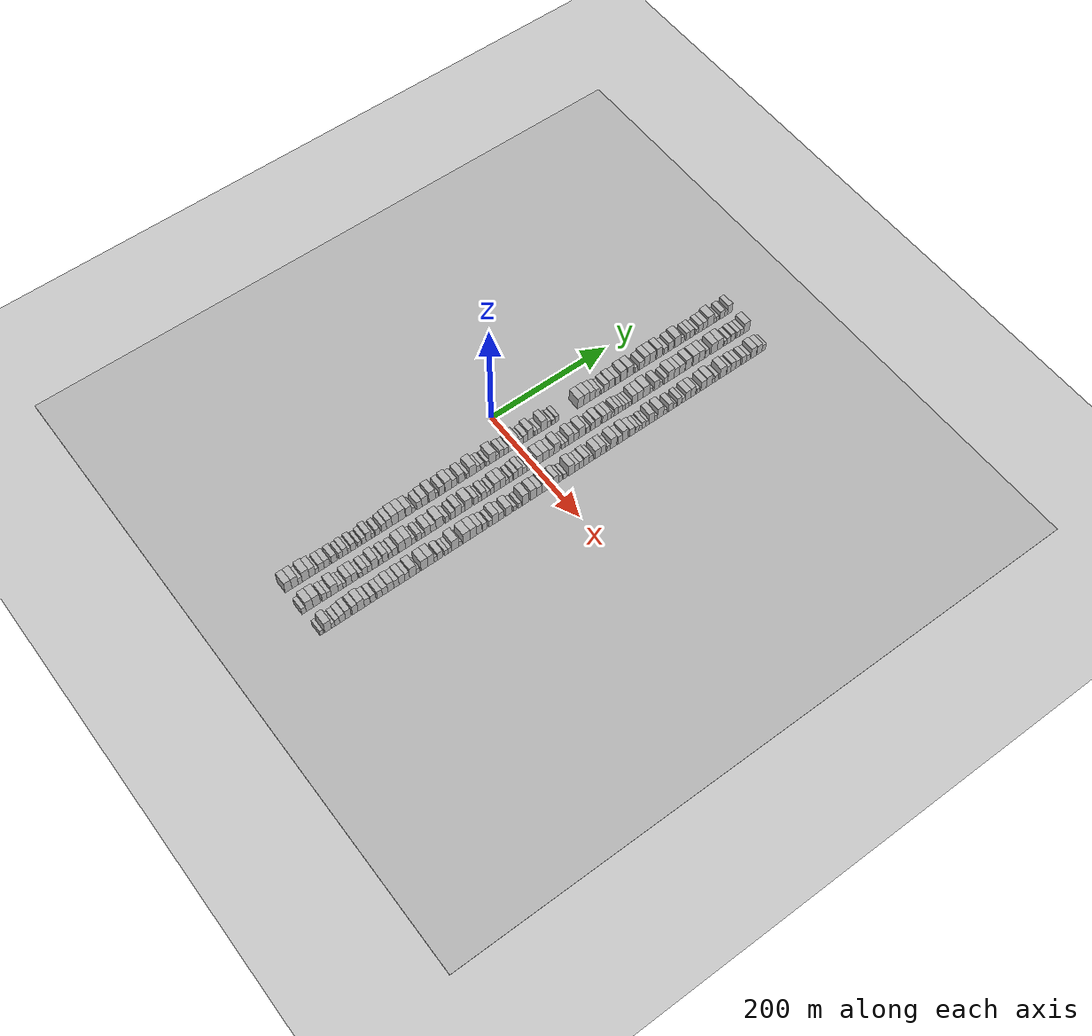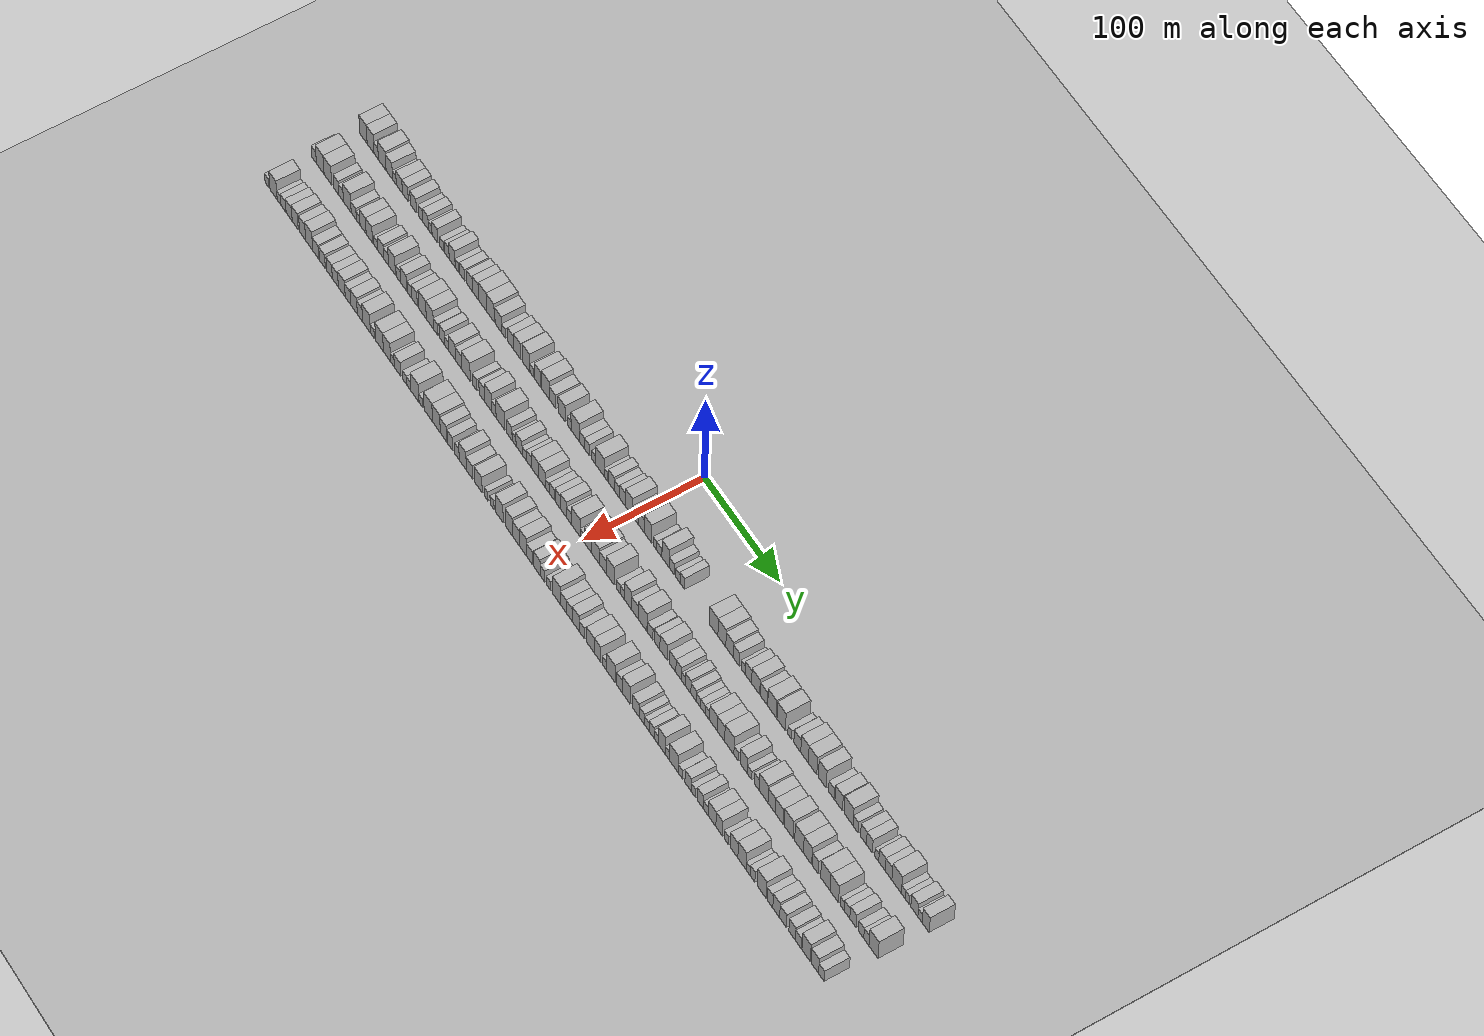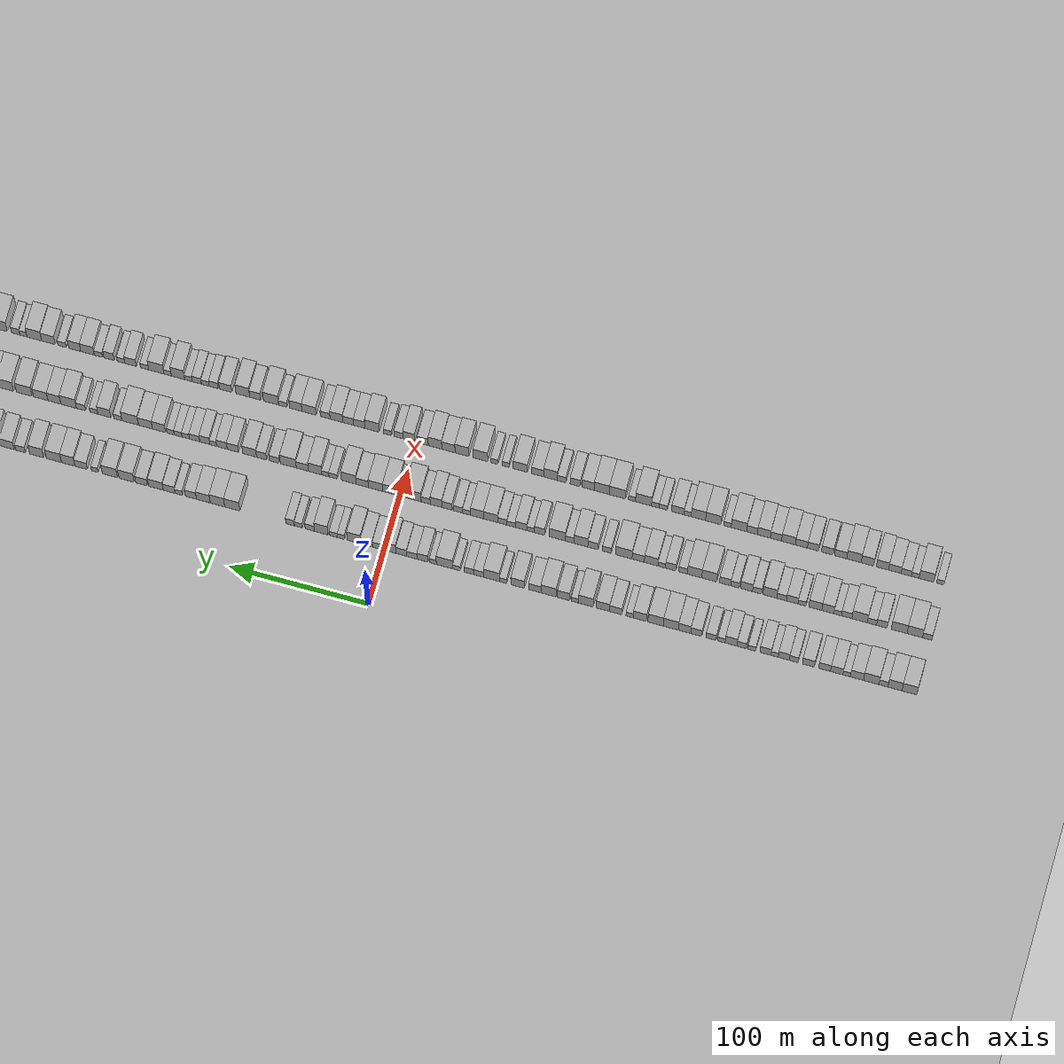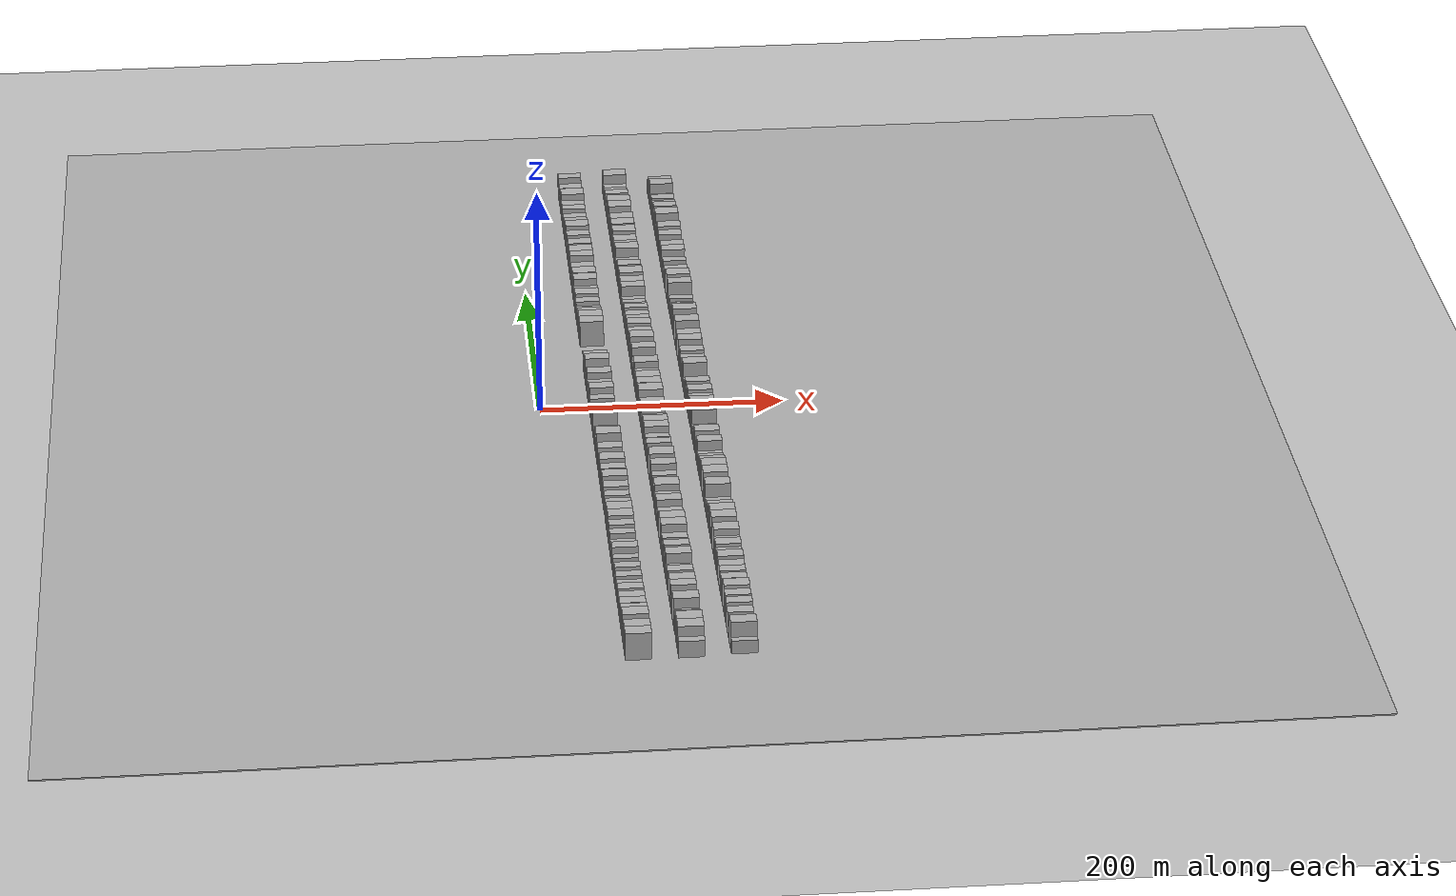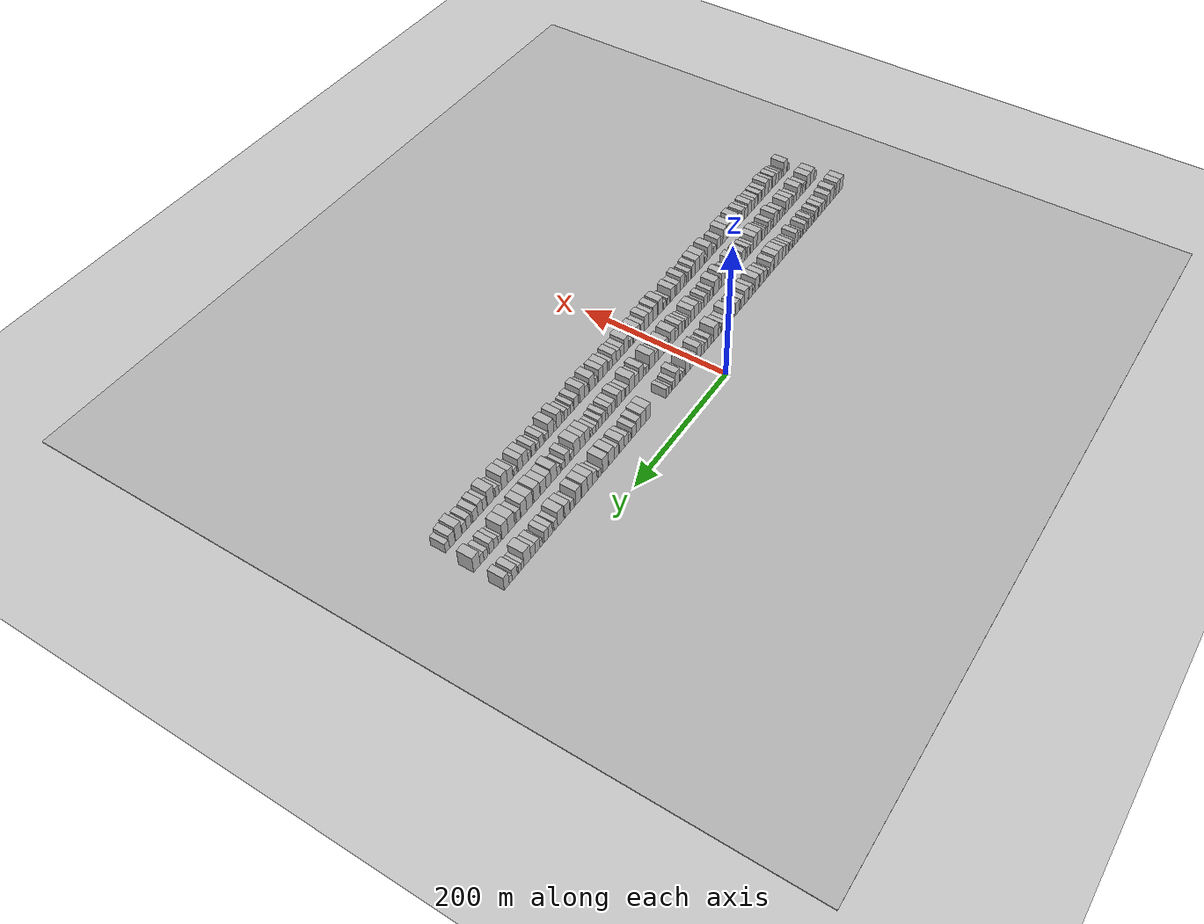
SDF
<?xml version="1.0" encoding="utf-8"?>

<sdf version="1.6">

   <world name="default">

      <gui fullscreen="0">

         <camera name="user_camera">

            <pose>-15 0 4.57585 0 0 0</pose>

            <view_controller>orbit</view_controller>

         </camera>

      </gui>

      <scene>

         <sky>

           <clouds>

             <speed>12</speed>

           </clouds>

         </sky>

         <ambient>0.4 0.4 0.4 1</ambient>

         <background>0.7 0.7 0.7 1</background>

         <shadows>1</shadows>

      </scene>

      <gravity>0 0 -9.8066</gravity>

      <magnetic_field>6e-06 2.3e-05 -4.2e-05</magnetic_field>

      <physics default="0" name="default_physics" type="ode">

         <ode>

            <solver>

               <type>quick</type>

               <iters>10</iters>

               <sor>1.0</sor>

               <use_dynamic_moi_rescaling>0</use_dynamic_moi_rescaling>

            </solver>

            <constraints>

               <cfm>0</cfm>

               <erp>0.2</erp>

               <contact_max_correcting_vel>100</contact_max_correcting_vel>

               <contact_surface_layer>0.001</contact_surface_layer>

            </constraints>

         </ode>

         <max_step_size>0.004</max_step_size>

         <real_time_factor>1</real_time_factor>

         <real_time_update_rate>250</real_time_update_rate>

      </physics>

      <light name="sun" type="directional">

         <cast_shadows>1</cast_shadows>

         <pose>0 0 10 0 0 0</pose>

         <diffuse>0.8 0.8 0.8 1</diffuse>

         <specular>0.2 0.2 0.2 1</specular>

         <attenuation>

            <range>1000</range>

            <constant>0.9</constant>

            <linear>0.01</linear>

            <quadratic>0.001</quadratic>

         </attenuation>

         <direction>-0.5 0.1 -0.9</direction>

      </light>

      <include>

         <name>ground_plane_1</name>

         <uri>model://HANNAS_ground_plane</uri>

         <pose>0 0 0  0 0 0</pose>

      </include>

      <include>

         <name>ground_plane_2</name>

         <uri>model://HANNAS_ground_plane</uri>

         <pose>100 0 0  0 0 0</pose>

      </include>

      <model name="building_1">

         <static>1</static>

         <pose frame="">50.0000 -374.7212 0 0.000000 0.000000 0.000000</pose>

         <link name="link">

            <pose frame="">0 0 12.00 0 0 0</pose>

            <collision name="collision">

               <geometry>

                  <box>

                     <size>20.0000 10.5576 24.0000</size>

                  </box>

               </geometry>

               <max_contacts>10</max_contacts>

               <surface>

                  <contact>

                     <ode/>

                  </contact>

                  <bounce/>

                  <friction>

                     <torsional>

                        <ode/>

                     </torsional>

                     <ode/>

                  </friction>

               </surface>

            </collision>

            <visual name="visual">

               <cast_shadows>0</cast_shadows>

               <geometry>

                  <box>

                     <size>20.0000 10.5576 24.0000</size>

                  </box>

               </geometry>

               <material>

                  <script>

                     <uri>model://HANNAS_wall/materials/scripts</uri>

                     <uri>model://HANNAS_wall/materials/textures</uri>

                     <name>vrc/HANNAS_wall</name>

                  </script>

               </material>

            </visual>

            <self_collide>0</self_collide>

            <enable_wind>0</enable_wind>

            <kinematic>0</kinematic>

         </link>

      </model>

      <model name="building_2">

         <static>1</static>

         <pose frame="">50.0000 -364.4689 0 0.000000 0.000000 0.000000</pose>

         <link name="link">

            <pose frame="">0 0 12.00 0 0 0</pose>

            <collision name="collision">

               <geometry>

                  <box>

                     <size>20.0000 9.9470 24.0000</size>

                  </box>

               </geometry>

               <max_contacts>10</max_contacts>

               <surface>

                  <contact>

                     <ode/>

                  </contact>

                  <bounce/>

                  <friction>

                     <torsional>

                        <ode/>

                     </torsional>

                     <ode/>

                  </friction>

               </surface>

            </collision>

            <visual name="visual">

               <cast_shadows>0</cast_shadows>

               <geometry>

                  <box>

                     <size>20.0000 9.9470 24.0000</size>

                  </box>

               </geometry>

               <material>

                  <script>

                     <uri>model://HANNAS_wall/materials/scripts</uri>

                     <uri>model://HANNAS_wall/materials/textures</uri>

                     <name>vrc/HANNAS_wall</name>

                  </script>

               </material>

            </visual>

            <self_collide>0</self_collide>

            <enable_wind>0</enable_wind>

            <kinematic>0</kinematic>

         </link>

      </model>

      <model name="building_3">

         <static>1</static>

         <pose frame="">50.0000 -356.3174 0 0.000000 0.000000 0.000000</pose>

         <link name="link">

            <pose frame="">0 0 7.50 0 0 0</pose>

            <collision name="collision">

               <geometry>

                  <box>

                     <size>20.0000 6.3561 15.0000</size>

                  </box>

               </geometry>

               <max_contacts>10</max_contacts>

               <surface>

                  <contact>

                     <ode/>

                  </contact>

                  <bounce/>

                  <friction>

                     <torsional>

                        <ode/>

                     </torsional>

                     <ode/>

                  </friction>

               </surface>

            </collision>

            <visual name="visual">

               <cast_shadows>0</cast_shadows>

               <geometry>

                  <box>

                     <size>20.0000 6.3561 15.0000</size>

                  </box>

               </geometry>

               <material>

                  <script>

                     <uri>model://HANNAS_wall/materials/scripts</uri>

                     <uri>model://HANNAS_wall/materials/textures</uri>

                     <name>vrc/HANNAS_wall</name>

                  </script>

               </material>

            </visual>

            <self_collide>0</self_collide>

            <enable_wind>0</enable_wind>

            <kinematic>0</kinematic>

         </link>

      </model>

      <model name="building_4">

         <static>1</static>

         <pose frame="">50.0000 -347.6121 0 0.000000 0.000000 0.000000</pose>

         <link name="link">

            <pose frame="">0 0 12.00 0 0 0</pose>

            <collision name="collision">

               <geometry>

                  <box>

                     <size>20.0000 11.0544 24.0000</size>

                  </box>

               </geometry>

               <max_contacts>10</max_contacts>

               <surface>

                  <contact>

                     <ode/>

                  </contact>

                  <bounce/>

                  <friction>

                     <torsional>

                        <ode/>

                     </torsional>

                     <ode/>

                  </friction>

               </surface>

            </collision>

            <visual name="visual">

               <cast_shadows>0</cast_shadows>

               <geometry>

                  <box>

                     <size>20.0000 11.0544 24.0000</size>

                  </box>

               </geometry>

               <material>

                  <script>

                     <uri>model://HANNAS_wall/materials/scripts</uri>

                     <uri>model://HANNAS_wall/materials/textures</uri>

                     <name>vrc/HANNAS_wall</name>

                  </script>

               </material>

            </visual>

            <self_collide>0</self_collide>

            <enable_wind>0</enable_wind>

            <kinematic>0</kinematic>

         </link>

      </model>

      <model name="building_5">

         <static>1</static>

         <pose frame="">50.0000 -337.4153 0 0.000000 0.000000 0.000000</pose>

         <link name="link">

            <pose frame="">0 0 10.50 0 0 0</pose>

            <collision name="collision">

               <geometry>

                  <box>

                     <size>20.0000 9.3393 21.0000</size>

                  </box>

               </geometry>

               <max_contacts>10</max_contacts>

               <surface>

                  <contact>

                     <ode/>

                  </contact>

                  <bounce/>

                  <friction>

                     <torsional>

                        <ode/>

                     </torsional>

                     <ode/>

                  </friction>

               </surface>

            </collision>

            <visual name="visual">

               <cast_shadows>0</cast_shadows>

               <geometry>

                  <box>

                     <size>20.0000 9.3393 21.0000</size>

                  </box>

               </geometry>

               <material>

                  <script>

                     <uri>model://HANNAS_wall/materials/scripts</uri>

                     <uri>model://HANNAS_wall/materials/textures</uri>

                     <name>vrc/HANNAS_wall</name>

                  </script>

               </material>

            </visual>

            <self_collide>0</self_collide>

            <enable_wind>0</enable_wind>

            <kinematic>0</kinematic>

         </link>

      </model>

      <model name="building_6">

         <static>1</static>

         <pose frame="">50.0000 -330.0703 0 0.000000 0.000000 0.000000</pose>

         <link name="link">

            <pose frame="">0 0 6.00 0 0 0</pose>

            <collision name="collision">

               <geometry>

                  <box>

                     <size>20.0000 5.3508 12.0000</size>

                  </box>

               </geometry>

               <max_contacts>10</max_contacts>

               <surface>

                  <contact>

                     <ode/>

                  </contact>

                  <bounce/>

                  <friction>

                     <torsional>

                        <ode/>

                     </torsional>

                     <ode/>

                  </friction>

               </surface>

            </collision>

            <visual name="visual">

               <cast_shadows>0</cast_shadows>

               <geometry>

                  <box>

                     <size>20.0000 5.3508 12.0000</size>

                  </box>

               </geometry>

               <material>

                  <script>

                     <uri>model://HANNAS_wall/materials/scripts</uri>

                     <uri>model://HANNAS_wall/materials/textures</uri>

                     <name>vrc/HANNAS_wall</name>

                  </script>

               </material>

            </visual>

            <self_collide>0</self_collide>

            <enable_wind>0</enable_wind>

            <kinematic>0</kinematic>

         </link>

      </model>

      <model name="building_7">

         <static>1</static>

         <pose frame="">50.0000 -323.0096 0 0.000000 0.000000 0.000000</pose>

         <link name="link">

            <pose frame="">0 0 9.00 0 0 0</pose>

            <collision name="collision">

               <geometry>

                  <box>

                     <size>20.0000 8.7705 18.0000</size>

                  </box>

               </geometry>

               <max_contacts>10</max_contacts>

               <surface>

                  <contact>

                     <ode/>

                  </contact>

                  <bounce/>

                  <friction>

                     <torsional>

                        <ode/>

                     </torsional>

                     <ode/>

                  </friction>

               </surface>

            </collision>

            <visual name="visual">

               <cast_shadows>0</cast_shadows>

               <geometry>

                  <box>

                     <size>20.0000 8.7705 18.0000</size>

                  </box>

               </geometry>

               <material>

                  <script>

                     <uri>model://HANNAS_wall/materials/scripts</uri>

                     <uri>model://HANNAS_wall/materials/textures</uri>

                     <name>vrc/HANNAS_wall</name>

                  </script>

               </material>

            </visual>

            <self_collide>0</self_collide>

            <enable_wind>0</enable_wind>

            <kinematic>0</kinematic>

         </link>

      </model>

      <model name="building_8">

         <static>1</static>

         <pose frame="">50.0000 -314.3873 0 0.000000 0.000000 0.000000</pose>

         <link name="link">

            <pose frame="">0 0 9.00 0 0 0</pose>

            <collision name="collision">

               <geometry>

                  <box>

                     <size>20.0000 8.4741 18.0000</size>

                  </box>

               </geometry>

               <max_contacts>10</max_contacts>

               <surface>

                  <contact>

                     <ode/>

                  </contact>

                  <bounce/>

                  <friction>

                     <torsional>

                        <ode/>

                     </torsional>

                     <ode/>

                  </friction>

               </surface>

            </collision>

            <visual name="visual">

               <cast_shadows>0</cast_shadows>

               <geometry>

                  <box>

                     <size>20.0000 8.4741 18.0000</size>

                  </box>

               </geometry>

               <material>

                  <script>

                     <uri>model://HANNAS_wall/materials/scripts</uri>

                     <uri>model://HANNAS_wall/materials/textures</uri>

                     <name>vrc/HANNAS_wall</name>

                  </script>

               </material>

            </visual>

            <self_collide>0</self_collide>

            <enable_wind>0</enable_wind>

            <kinematic>0</kinematic>

         </link>

      </model>

      <model name="building_9">

         <static>1</static>

         <pose frame="">50.0000 -302.8342 0 0.000000 0.000000 0.000000</pose>

         <link name="link">

            <pose frame="">0 0 9.00 0 0 0</pose>

            <collision name="collision">

               <geometry>

                  <box>

                     <size>20.0000 8.6323 18.0000</size>

                  </box>

               </geometry>

               <max_contacts>10</max_contacts>

               <surface>

                  <contact>

                     <ode/>

                  </contact>

                  <bounce/>

                  <friction>

                     <torsional>

                        <ode/>

                     </torsional>

                     <ode/>

                  </friction>

               </surface>

            </collision>

            <visual name="visual">

               <cast_shadows>0</cast_shadows>

               <geometry>

                  <box>

                     <size>20.0000 8.6323 18.0000</size>

                  </box>

               </geometry>

               <material>

                  <script>

                     <uri>model://HANNAS_wall/materials/scripts</uri>

                     <uri>model://HANNAS_wall/materials/textures</uri>

                     <name>vrc/HANNAS_wall</name>

                  </script>

               </material>

            </visual>

            <self_collide>0</self_collide>

            <enable_wind>0</enable_wind>

            <kinematic>0</kinematic>

         </link>

      </model>

      <model name="building_10">

         <static>1</static>

         <pose frame="">50.0000 -292.4121 0 0.000000 0.000000 0.000000</pose>

         <link name="link">

            <pose frame="">0 0 7.50 0 0 0</pose>

            <collision name="collision">

               <geometry>

                  <box>

                     <size>20.0000 6.2119 15.0000</size>

                  </box>

               </geometry>

               <max_contacts>10</max_contacts>

               <surface>

                  <contact>

                     <ode/>

                  </contact>

                  <bounce/>

                  <friction>

                     <torsional>

                        <ode/>

                     </torsional>

                     <ode/>

                  </friction>

               </surface>

            </collision>

            <visual name="visual">

               <cast_shadows>0</cast_shadows>

               <geometry>

                  <box>

                     <size>20.0000 6.2119 15.0000</size>

                  </box>

               </geometry>

               <material>

                  <script>

                     <uri>model://HANNAS_wall/materials/scripts</uri>

                     <uri>model://HANNAS_wall/materials/textures</uri>

                     <name>vrc/HANNAS_wall</name>

                  </script>

               </material>

            </visual>

            <self_collide>0</self_collide>

            <enable_wind>0</enable_wind>

            <kinematic>0</kinematic>

         </link>

      </model>

      <model name="building_11">

         <static>1</static>

         <pose frame="">50.0000 -285.3652 0 0.000000 0.000000 0.000000</pose>

         <link name="link">

            <pose frame="">0 0 9.00 0 0 0</pose>

            <collision name="collision">

               <geometry>

                  <box>

                     <size>20.0000 7.8817 18.0000</size>

                  </box>

               </geometry>

               <max_contacts>10</max_contacts>

               <surface>

                  <contact>

                     <ode/>

                  </contact>

                  <bounce/>

                  <friction>

                     <torsional>

                        <ode/>

                     </torsional>

                     <ode/>

                  </friction>

               </surface>

            </collision>

            <visual name="visual">

               <cast_shadows>0</cast_shadows>

               <geometry>

                  <box>

                     <size>20.0000 7.8817 18.0000</size>

                  </box>

               </geometry>

               <material>

                  <script>

                     <uri>model://HANNAS_wall/materials/scripts</uri>

                     <uri>model://HANNAS_wall/materials/textures</uri>

                     <name>vrc/HANNAS_wall</name>

                  </script>

               </material>

            </visual>

            <self_collide>0</self_collide>

            <enable_wind>0</enable_wind>

            <kinematic>0</kinematic>

         </link>

      </model>

      <model name="building_12">

         <static>1</static>

         <pose frame="">50.0000 -278.8355 0 0.000000 0.000000 0.000000</pose>

         <link name="link">

            <pose frame="">0 0 6.00 0 0 0</pose>

            <collision name="collision">

               <geometry>

                  <box>

                     <size>20.0000 5.1779 12.0000</size>

                  </box>

               </geometry>

               <max_contacts>10</max_contacts>

               <surface>

                  <contact>

                     <ode/>

                  </contact>

                  <bounce/>

                  <friction>

                     <torsional>

                        <ode/>

                     </torsional>

                     <ode/>

                  </friction>

               </surface>

            </collision>

            <visual name="visual">

               <cast_shadows>0</cast_shadows>

               <geometry>

                  <box>

                     <size>20.0000 5.1779 12.0000</size>

                  </box>

               </geometry>

               <material>

                  <script>

                     <uri>model://HANNAS_wall/materials/scripts</uri>

                     <uri>model://HANNAS_wall/materials/textures</uri>

                     <name>vrc/HANNAS_wall</name>

                  </script>

               </material>

            </visual>

            <self_collide>0</self_collide>

            <enable_wind>0</enable_wind>

            <kinematic>0</kinematic>

         </link>

      </model>

      <model name="building_13">

         <static>1</static>

         <pose frame="">50.0000 -272.2548 0 0.000000 0.000000 0.000000</pose>

         <link name="link">

            <pose frame="">0 0 9.00 0 0 0</pose>

            <collision name="collision">

               <geometry>

                  <box>

                     <size>20.0000 7.9834 18.0000</size>

                  </box>

               </geometry>

               <max_contacts>10</max_contacts>

               <surface>

                  <contact>

                     <ode/>

                  </contact>

                  <bounce/>

                  <friction>

                     <torsional>

                        <ode/>

                     </torsional>

                     <ode/>

                  </friction>

               </surface>

            </collision>

            <visual name="visual">

               <cast_shadows>0</cast_shadows>

               <geometry>

                  <box>

                     <size>20.0000 7.9834 18.0000</size>

                  </box>

               </geometry>

               <material>

                  <script>

                     <uri>model://HANNAS_wall/materials/scripts</uri>

                     <uri>model://HANNAS_wall/materials/textures</uri>

                     <name>vrc/HANNAS_wall</name>

                  </script>

               </material>

            </visual>

            <self_collide>0</self_collide>

            <enable_wind>0</enable_wind>

            <kinematic>0</kinematic>

         </link>

      </model>

      <model name="building_14">

         <static>1</static>

         <pose frame="">50.0000 -262.4717 0 0.000000 0.000000 0.000000</pose>

         <link name="link">

            <pose frame="">0 0 6.00 0 0 0</pose>

            <collision name="collision">

               <geometry>

                  <box>

                     <size>20.0000 5.5828 12.0000</size>

                  </box>

               </geometry>

               <max_contacts>10</max_contacts>

               <surface>

                  <contact>

                     <ode/>

                  </contact>

                  <bounce/>

                  <friction>

                     <torsional>

                        <ode/>

                     </torsional>

                     <ode/>

                  </friction>

               </surface>

            </collision>

            <visual name="visual">

               <cast_shadows>0</cast_shadows>

               <geometry>

                  <box>

                     <size>20.0000 5.5828 12.0000</size>

                  </box>

               </geometry>

               <material>

                  <script>

                     <uri>model://HANNAS_wall/materials/scripts</uri>

                     <uri>model://HANNAS_wall/materials/textures</uri>

                     <name>vrc/HANNAS_wall</name>

                  </script>

               </material>

            </visual>

            <self_collide>0</self_collide>

            <enable_wind>0</enable_wind>

            <kinematic>0</kinematic>

         </link>

      </model>

      <model name="building_15">

         <static>1</static>

         <pose frame="">50.0000 -255.3327 0 0.000000 0.000000 0.000000</pose>

         <link name="link">

            <pose frame="">0 0 7.50 0 0 0</pose>

            <collision name="collision">

               <geometry>

                  <box>

                     <size>20.0000 6.6953 15.0000</size>

                  </box>

               </geometry>

               <max_contacts>10</max_contacts>

               <surface>

                  <contact>

                     <ode/>

                  </contact>

                  <bounce/>

                  <friction>

                     <torsional>

                        <ode/>

                     </torsional>

                     <ode/>

                  </friction>

               </surface>

            </collision>

            <visual name="visual">

               <cast_shadows>0</cast_shadows>

               <geometry>

                  <box>

                     <size>20.0000 6.6953 15.0000</size>

                  </box>

               </geometry>

               <material>

                  <script>

                     <uri>model://HANNAS_wall/materials/scripts</uri>

                     <uri>model://HANNAS_wall/materials/textures</uri>

                     <name>vrc/HANNAS_wall</name>

                  </script>

               </material>

            </visual>

            <self_collide>0</self_collide>

            <enable_wind>0</enable_wind>

            <kinematic>0</kinematic>

         </link>

      </model>

      <model name="building_16">

         <static>1</static>

         <pose frame="">50.0000 -247.7296 0 0.000000 0.000000 0.000000</pose>

         <link name="link">

            <pose frame="">0 0 10.50 0 0 0</pose>

            <collision name="collision">

               <geometry>

                  <box>

                     <size>20.0000 8.5108 21.0000</size>

                  </box>

               </geometry>

               <max_contacts>10</max_contacts>

               <surface>

                  <contact>

                     <ode/>

                  </contact>

                  <bounce/>

                  <friction>

                     <torsional>

                        <ode/>

                     </torsional>

                     <ode/>

                  </friction>

               </surface>

            </collision>

            <visual name="visual">

               <cast_shadows>0</cast_shadows>

               <geometry>

                  <box>

                     <size>20.0000 8.5108 21.0000</size>

                  </box>

               </geometry>

               <material>

                  <script>

                     <uri>model://HANNAS_wall/materials/scripts</uri>

                     <uri>model://HANNAS_wall/materials/textures</uri>

                     <name>vrc/HANNAS_wall</name>

                  </script>

               </material>

            </visual>

            <self_collide>0</self_collide>

            <enable_wind>0</enable_wind>

            <kinematic>0</kinematic>

         </link>

      </model>

      <model name="building_17">

         <static>1</static>

         <pose frame="">50.0000 -240.7629 0 0.000000 0.000000 0.000000</pose>

         <link name="link">

            <pose frame="">0 0 6.00 0 0 0</pose>

            <collision name="collision">

               <geometry>

                  <box>

                     <size>20.0000 5.4226 12.0000</size>

                  </box>

               </geometry>

               <max_contacts>10</max_contacts>

               <surface>

                  <contact>

                     <ode/>

                  </contact>

                  <bounce/>

                  <friction>

                     <torsional>

                        <ode/>

                     </torsional>

                     <ode/>

                  </friction>

               </surface>

            </collision>

            <visual name="visual">

               <cast_shadows>0</cast_shadows>

               <geometry>

                  <box>

                     <size>20.0000 5.4226 12.0000</size>

                  </box>

               </geometry>

               <material>

                  <script>

                     <uri>model://HANNAS_wall/materials/scripts</uri>

                     <uri>model://HANNAS_wall/materials/textures</uri>

                     <name>vrc/HANNAS_wall</name>

                  </script>

               </material>

            </visual>

            <self_collide>0</self_collide>

            <enable_wind>0</enable_wind>

            <kinematic>0</kinematic>

         </link>

      </model>

      <model name="building_18">

         <static>1</static>

         <pose frame="">50.0000 -233.4286 0 0.000000 0.000000 0.000000</pose>

         <link name="link">

            <pose frame="">0 0 7.50 0 0 0</pose>

            <collision name="collision">

               <geometry>

                  <box>

                     <size>20.0000 7.2459 15.0000</size>

                  </box>

               </geometry>

               <max_contacts>10</max_contacts>

               <surface>

                  <contact>

                     <ode/>

                  </contact>

                  <bounce/>

                  <friction>

                     <torsional>

                        <ode/>

                     </torsional>

                     <ode/>

                  </friction>

               </surface>

            </collision>

            <visual name="visual">

               <cast_shadows>0</cast_shadows>

               <geometry>

                  <box>

                     <size>20.0000 7.2459 15.0000</size>

                  </box>

               </geometry>

               <material>

                  <script>

                     <uri>model://HANNAS_wall/materials/scripts</uri>

                     <uri>model://HANNAS_wall/materials/textures</uri>

                     <name>vrc/HANNAS_wall</name>

                  </script>

               </material>

            </visual>

            <self_collide>0</self_collide>

            <enable_wind>0</enable_wind>

            <kinematic>0</kinematic>

         </link>

      </model>

      <model name="building_19">

         <static>1</static>

         <pose frame="">50.0000 -222.8635 0 0.000000 0.000000 0.000000</pose>

         <link name="link">

            <pose frame="">0 0 9.00 0 0 0</pose>

            <collision name="collision">

               <geometry>

                  <box>

                     <size>20.0000 7.8843 18.0000</size>

                  </box>

               </geometry>

               <max_contacts>10</max_contacts>

               <surface>

                  <contact>

                     <ode/>

                  </contact>

                  <bounce/>

                  <friction>

                     <torsional>

                        <ode/>

                     </torsional>

                     <ode/>

                  </friction>

               </surface>

            </collision>

            <visual name="visual">

               <cast_shadows>0</cast_shadows>

               <geometry>

                  <box>

                     <size>20.0000 7.8843 18.0000</size>

                  </box>

               </geometry>

               <material>

                  <script>

                     <uri>model://HANNAS_wall/materials/scripts</uri>

                     <uri>model://HANNAS_wall/materials/textures</uri>

                     <name>vrc/HANNAS_wall</name>

                  </script>

               </material>

            </visual>

            <self_collide>0</self_collide>

            <enable_wind>0</enable_wind>

            <kinematic>0</kinematic>

         </link>

      </model>

      <model name="building_20">

         <static>1</static>

         <pose frame="">50.0000 -214.5254 0 0.000000 0.000000 0.000000</pose>

         <link name="link">

            <pose frame="">0 0 10.50 0 0 0</pose>

            <collision name="collision">

               <geometry>

                  <box>

                     <size>20.0000 8.7921 21.0000</size>

                  </box>

               </geometry>

               <max_contacts>10</max_contacts>

               <surface>

                  <contact>

                     <ode/>

                  </contact>

                  <bounce/>

                  <friction>

                     <torsional>

                        <ode/>

                     </torsional>

                     <ode/>

                  </friction>

               </surface>

            </collision>

            <visual name="visual">

               <cast_shadows>0</cast_shadows>

               <geometry>

                  <box>

                     <size>20.0000 8.7921 21.0000</size>

                  </box>

               </geometry>

               <material>

                  <script>

                     <uri>model://HANNAS_wall/materials/scripts</uri>

                     <uri>model://HANNAS_wall/materials/textures</uri>

                     <name>vrc/HANNAS_wall</name>

                  </script>

               </material>

            </visual>

            <self_collide>0</self_collide>

            <enable_wind>0</enable_wind>

            <kinematic>0</kinematic>

         </link>

      </model>

      <model name="building_21">

         <static>1</static>

         <pose frame="">50.0000 -204.7309 0 0.000000 0.000000 0.000000</pose>

         <link name="link">

            <pose frame="">0 0 12.00 0 0 0</pose>

            <collision name="collision">

               <geometry>

                  <box>

                     <size>20.0000 10.7969 24.0000</size>

                  </box>

               </geometry>

               <max_contacts>10</max_contacts>

               <surface>

                  <contact>

                     <ode/>

                  </contact>

                  <bounce/>

                  <friction>

                     <torsional>

                        <ode/>

                     </torsional>

                     <ode/>

                  </friction>

               </surface>

            </collision>

            <visual name="visual">

               <cast_shadows>0</cast_shadows>

               <geometry>

                  <box>

                     <size>20.0000 10.7969 24.0000</size>

                  </box>

               </geometry>

               <material>

                  <script>

                     <uri>model://HANNAS_wall/materials/scripts</uri>

                     <uri>model://HANNAS_wall/materials/textures</uri>

                     <name>vrc/HANNAS_wall</name>

                  </script>

               </material>

            </visual>

            <self_collide>0</self_collide>

            <enable_wind>0</enable_wind>

            <kinematic>0</kinematic>

         </link>

      </model>

      <model name="building_22">

         <static>1</static>

         <pose frame="">50.0000 -193.8606 0 0.000000 0.000000 0.000000</pose>

         <link name="link">

            <pose frame="">0 0 12.00 0 0 0</pose>

            <collision name="collision">

               <geometry>

                  <box>

                     <size>20.0000 10.9437 24.0000</size>

                  </box>

               </geometry>

               <max_contacts>10</max_contacts>

               <surface>

                  <contact>

                     <ode/>

                  </contact>

                  <bounce/>

                  <friction>

                     <torsional>

                        <ode/>

                     </torsional>

                     <ode/>

                  </friction>

               </surface>

            </collision>

            <visual name="visual">

               <cast_shadows>0</cast_shadows>

               <geometry>

                  <box>

                     <size>20.0000 10.9437 24.0000</size>

                  </box>

               </geometry>

               <material>

                  <script>

                     <uri>model://HANNAS_wall/materials/scripts</uri>

                     <uri>model://HANNAS_wall/materials/textures</uri>

                     <name>vrc/HANNAS_wall</name>

                  </script>

               </material>

            </visual>

            <self_collide>0</self_collide>

            <enable_wind>0</enable_wind>

            <kinematic>0</kinematic>

         </link>

      </model>

      <model name="building_23">

         <static>1</static>

         <pose frame="">50.0000 -182.6399 0 0.000000 0.000000 0.000000</pose>

         <link name="link">

            <pose frame="">0 0 10.50 0 0 0</pose>

            <collision name="collision">

               <geometry>

                  <box>

                     <size>20.0000 9.4976 21.0000</size>

                  </box>

               </geometry>

               <max_contacts>10</max_contacts>

               <surface>

                  <contact>

                     <ode/>

                  </contact>

                  <bounce/>

                  <friction>

                     <torsional>

                        <ode/>

                     </torsional>

                     <ode/>

                  </friction>

               </surface>

            </collision>

            <visual name="visual">

               <cast_shadows>0</cast_shadows>

               <geometry>

                  <box>

                     <size>20.0000 9.4976 21.0000</size>

                  </box>

               </geometry>

               <material>

                  <script>

                     <uri>model://HANNAS_wall/materials/scripts</uri>

                     <uri>model://HANNAS_wall/materials/textures</uri>

                     <name>vrc/HANNAS_wall</name>

                  </script>

               </material>

            </visual>

            <self_collide>0</self_collide>

            <enable_wind>0</enable_wind>

            <kinematic>0</kinematic>

         </link>

      </model>

      <model name="building_24">

         <static>1</static>

         <pose frame="">50.0000 -175.2718 0 0.000000 0.000000 0.000000</pose>

         <link name="link">

            <pose frame="">0 0 6.00 0 0 0</pose>

            <collision name="collision">

               <geometry>

                  <box>

                     <size>20.0000 5.2387 12.0000</size>

                  </box>

               </geometry>

               <max_contacts>10</max_contacts>

               <surface>

                  <contact>

                     <ode/>

                  </contact>

                  <bounce/>

                  <friction>

                     <torsional>

                        <ode/>

                     </torsional>

                     <ode/>

                  </friction>

               </surface>

            </collision>

            <visual name="visual">

               <cast_shadows>0</cast_shadows>

               <geometry>

                  <box>

                     <size>20.0000 5.2387 12.0000</size>

                  </box>

               </geometry>

               <material>

                  <script>

                     <uri>model://HANNAS_wall/materials/scripts</uri>

                     <uri>model://HANNAS_wall/materials/textures</uri>

                     <name>vrc/HANNAS_wall</name>

                  </script>

               </material>

            </visual>

            <self_collide>0</self_collide>

            <enable_wind>0</enable_wind>

            <kinematic>0</kinematic>

         </link>

      </model>

      <model name="building_25">

         <static>1</static>

         <pose frame="">50.0000 -165.3610 0 0.000000 0.000000 0.000000</pose>

         <link name="link">

            <pose frame="">0 0 9.00 0 0 0</pose>

            <collision name="collision">

               <geometry>

                  <box>

                     <size>20.0000 8.5828 18.0000</size>

                  </box>

               </geometry>

               <max_contacts>10</max_contacts>

               <surface>

                  <contact>

                     <ode/>

                  </contact>

                  <bounce/>

                  <friction>

                     <torsional>

                        <ode/>

                     </torsional>

                     <ode/>

                  </friction>

               </surface>

            </collision>

            <visual name="visual">

               <cast_shadows>0</cast_shadows>

               <geometry>

                  <box>

                     <size>20.0000 8.5828 18.0000</size>

                  </box>

               </geometry>

               <material>

                  <script>

                     <uri>model://HANNAS_wall/materials/scripts</uri>

                     <uri>model://HANNAS_wall/materials/textures</uri>

                     <name>vrc/HANNAS_wall</name>

                  </script>

               </material>

            </visual>

            <self_collide>0</self_collide>

            <enable_wind>0</enable_wind>

            <kinematic>0</kinematic>

         </link>

      </model>

      <model name="building_26">

         <static>1</static>

         <pose frame="">50.0000 -156.2007 0 0.000000 0.000000 0.000000</pose>

         <link name="link">

            <pose frame="">0 0 10.50 0 0 0</pose>

            <collision name="collision">

               <geometry>

                  <box>

                     <size>20.0000 9.7379 21.0000</size>

                  </box>

               </geometry>

               <max_contacts>10</max_contacts>

               <surface>

                  <contact>

                     <ode/>

                  </contact>

                  <bounce/>

                  <friction>

                     <torsional>

                        <ode/>

                     </torsional>

                     <ode/>

                  </friction>

               </surface>

            </collision>

            <visual name="visual">

               <cast_shadows>0</cast_shadows>

               <geometry>

                  <box>

                     <size>20.0000 9.7379 21.0000</size>

                  </box>

               </geometry>

               <material>

                  <script>

                     <uri>model://HANNAS_wall/materials/scripts</uri>

                     <uri>model://HANNAS_wall/materials/textures</uri>

                     <name>vrc/HANNAS_wall</name>

                  </script>

               </material>

            </visual>

            <self_collide>0</self_collide>

            <enable_wind>0</enable_wind>

            <kinematic>0</kinematic>

         </link>

      </model>

      <model name="building_27">

         <static>1</static>

         <pose frame="">50.0000 -144.0511 0 0.000000 0.000000 0.000000</pose>

         <link name="link">

            <pose frame="">0 0 12.00 0 0 0</pose>

            <collision name="collision">

               <geometry>

                  <box>

                     <size>20.0000 10.5612 24.0000</size>

                  </box>

               </geometry>

               <max_contacts>10</max_contacts>

               <surface>

                  <contact>

                     <ode/>

                  </contact>

                  <bounce/>

                  <friction>

                     <torsional>

                        <ode/>

                     </torsional>

                     <ode/>

                  </friction>

               </surface>

            </collision>

            <visual name="visual">

               <cast_shadows>0</cast_shadows>

               <geometry>

                  <box>

                     <size>20.0000 10.5612 24.0000</size>

                  </box>

               </geometry>

               <material>

                  <script>

                     <uri>model://HANNAS_wall/materials/scripts</uri>

                     <uri>model://HANNAS_wall/materials/textures</uri>

                     <name>vrc/HANNAS_wall</name>

                  </script>

               </material>

            </visual>

            <self_collide>0</self_collide>

            <enable_wind>0</enable_wind>

            <kinematic>0</kinematic>

         </link>

      </model>

      <model name="building_28">

         <static>1</static>

         <pose frame="">50.0000 -136.1599 0 0.000000 0.000000 0.000000</pose>

         <link name="link">

            <pose frame="">0 0 6.00 0 0 0</pose>

            <collision name="collision">

               <geometry>

                  <box>

                     <size>20.0000 5.2212 12.0000</size>

                  </box>

               </geometry>

               <max_contacts>10</max_contacts>

               <surface>

                  <contact>

                     <ode/>

                  </contact>

                  <bounce/>

                  <friction>

                     <torsional>

                        <ode/>

                     </torsional>

                     <ode/>

                  </friction>

               </surface>

            </collision>

            <visual name="visual">

               <cast_shadows>0</cast_shadows>

               <geometry>

                  <box>

                     <size>20.0000 5.2212 12.0000</size>

                  </box>

               </geometry>

               <material>

                  <script>

                     <uri>model://HANNAS_wall/materials/scripts</uri>

                     <uri>model://HANNAS_wall/materials/textures</uri>

                     <name>vrc/HANNAS_wall</name>

                  </script>

               </material>

            </visual>

            <self_collide>0</self_collide>

            <enable_wind>0</enable_wind>

            <kinematic>0</kinematic>

         </link>

      </model>

      <model name="building_29">

         <static>1</static>

         <pose frame="">50.0000 -128.1237 0 0.000000 0.000000 0.000000</pose>

         <link name="link">

            <pose frame="">0 0 10.50 0 0 0</pose>

            <collision name="collision">

               <geometry>

                  <box>

                     <size>20.0000 8.8513 21.0000</size>

                  </box>

               </geometry>

               <max_contacts>10</max_contacts>

               <surface>

                  <contact>

                     <ode/>

                  </contact>

                  <bounce/>

                  <friction>

                     <torsional>

                        <ode/>

                     </torsional>

                     <ode/>

                  </friction>

               </surface>

            </collision>

            <visual name="visual">

               <cast_shadows>0</cast_shadows>

               <geometry>

                  <box>

                     <size>20.0000 8.8513 21.0000</size>

                  </box>

               </geometry>

               <material>

                  <script>

                     <uri>model://HANNAS_wall/materials/scripts</uri>

                     <uri>model://HANNAS_wall/materials/textures</uri>

                     <name>vrc/HANNAS_wall</name>

                  </script>

               </material>

            </visual>

            <self_collide>0</self_collide>

            <enable_wind>0</enable_wind>

            <kinematic>0</kinematic>

         </link>

      </model>

      <model name="building_30">

         <static>1</static>

         <pose frame="">50.0000 -117.2829 0 0.000000 0.000000 0.000000</pose>

         <link name="link">

            <pose frame="">0 0 12.00 0 0 0</pose>

            <collision name="collision">

               <geometry>

                  <box>

                     <size>20.0000 10.8303 24.0000</size>

                  </box>

               </geometry>

               <max_contacts>10</max_contacts>

               <surface>

                  <contact>

                     <ode/>

                  </contact>

                  <bounce/>

                  <friction>

                     <torsional>

                        <ode/>

                     </torsional>

                     <ode/>

                  </friction>

               </surface>

            </collision>

            <visual name="visual">

               <cast_shadows>0</cast_shadows>

               <geometry>

                  <box>

                     <size>20.0000 10.8303 24.0000</size>

                  </box>

               </geometry>

               <material>

                  <script>

                     <uri>model://HANNAS_wall/materials/scripts</uri>

                     <uri>model://HANNAS_wall/materials/textures</uri>

                     <name>vrc/HANNAS_wall</name>

                  </script>

               </material>

            </visual>

            <self_collide>0</self_collide>

            <enable_wind>0</enable_wind>

            <kinematic>0</kinematic>

         </link>

      </model>

      <model name="building_31">

         <static>1</static>

         <pose frame="">50.0000 -107.4530 0 0.000000 0.000000 0.000000</pose>

         <link name="link">

            <pose frame="">0 0 9.00 0 0 0</pose>

            <collision name="collision">

               <geometry>

                  <box>

                     <size>20.0000 8.8295 18.0000</size>

                  </box>

               </geometry>

               <max_contacts>10</max_contacts>

               <surface>

                  <contact>

                     <ode/>

                  </contact>

                  <bounce/>

                  <friction>

                     <torsional>

                        <ode/>

                     </torsional>

                     <ode/>

                  </friction>

               </surface>

            </collision>

            <visual name="visual">

               <cast_shadows>0</cast_shadows>

               <geometry>

                  <box>

                     <size>20.0000 8.8295 18.0000</size>

                  </box>

               </geometry>

               <material>

                  <script>

                     <uri>model://HANNAS_wall/materials/scripts</uri>

                     <uri>model://HANNAS_wall/materials/textures</uri>

                     <name>vrc/HANNAS_wall</name>

                  </script>

               </material>

            </visual>

            <self_collide>0</self_collide>

            <enable_wind>0</enable_wind>

            <kinematic>0</kinematic>

         </link>

      </model>

      <model name="building_32">

         <static>1</static>

         <pose frame="">50.0000 -95.1832 0 0.000000 0.000000 0.000000</pose>

         <link name="link">

            <pose frame="">0 0 10.50 0 0 0</pose>

            <collision name="collision">

               <geometry>

                  <box>

                     <size>20.0000 9.7101 21.0000</size>

                  </box>

               </geometry>

               <max_contacts>10</max_contacts>

               <surface>

                  <contact>

                     <ode/>

                  </contact>

                  <bounce/>

                  <friction>

                     <torsional>

                        <ode/>

                     </torsional>

                     <ode/>

                  </friction>

               </surface>

            </collision>

            <visual name="visual">

               <cast_shadows>0</cast_shadows>

               <geometry>

                  <box>

                     <size>20.0000 9.7101 21.0000</size>

                  </box>

               </geometry>

               <material>

                  <script>

                     <uri>model://HANNAS_wall/materials/scripts</uri>

                     <uri>model://HANNAS_wall/materials/textures</uri>

                     <name>vrc/HANNAS_wall</name>

                  </script>

               </material>

            </visual>

            <self_collide>0</self_collide>

            <enable_wind>0</enable_wind>

            <kinematic>0</kinematic>

         </link>

      </model>

      <model name="building_33">

         <static>1</static>

         <pose frame="">50.0000 -84.7593 0 0.000000 0.000000 0.000000</pose>

         <link name="link">

            <pose frame="">0 0 6.00 0 0 0</pose>

            <collision name="collision">

               <geometry>

                  <box>

                     <size>20.0000 5.1378 12.0000</size>

                  </box>

               </geometry>

               <max_contacts>10</max_contacts>

               <surface>

                  <contact>

                     <ode/>

                  </contact>

                  <bounce/>

                  <friction>

                     <torsional>

                        <ode/>

                     </torsional>

                     <ode/>

                  </friction>

               </surface>

            </collision>

            <visual name="visual">

               <cast_shadows>0</cast_shadows>

               <geometry>

                  <box>

                     <size>20.0000 5.1378 12.0000</size>

                  </box>

               </geometry>

               <material>

                  <script>

                     <uri>model://HANNAS_wall/materials/scripts</uri>

                     <uri>model://HANNAS_wall/materials/textures</uri>

                     <name>vrc/HANNAS_wall</name>

                  </script>

               </material>

            </visual>

            <self_collide>0</self_collide>

            <enable_wind>0</enable_wind>

            <kinematic>0</kinematic>

         </link>

      </model>

      <model name="building_34">

         <static>1</static>

         <pose frame="">50.0000 -76.4821 0 0.000000 0.000000 0.000000</pose>

         <link name="link">

            <pose frame="">0 0 12.00 0 0 0</pose>

            <collision name="collision">

               <geometry>

                  <box>

                     <size>20.0000 11.4165 24.0000</size>

                  </box>

               </geometry>

               <max_contacts>10</max_contacts>

               <surface>

                  <contact>

                     <ode/>

                  </contact>

                  <bounce/>

                  <friction>

                     <torsional>

                        <ode/>

                     </torsional>

                     <ode/>

                  </friction>

               </surface>

            </collision>

            <visual name="visual">

               <cast_shadows>0</cast_shadows>

               <geometry>

                  <box>

                     <size>20.0000 11.4165 24.0000</size>

                  </box>

               </geometry>

               <material>

                  <script>

                     <uri>model://HANNAS_wall/materials/scripts</uri>

                     <uri>model://HANNAS_wall/materials/textures</uri>

                     <name>vrc/HANNAS_wall</name>

                  </script>

               </material>

            </visual>

            <self_collide>0</self_collide>

            <enable_wind>0</enable_wind>

            <kinematic>0</kinematic>

         </link>

      </model>

      <model name="building_35">

         <static>1</static>

         <pose frame="">50.0000 -67.2317 0 0.000000 0.000000 0.000000</pose>

         <link name="link">

            <pose frame="">0 0 7.50 0 0 0</pose>

            <collision name="collision">

               <geometry>

                  <box>

                     <size>20.0000 7.0843 15.0000</size>

                  </box>

               </geometry>

               <max_contacts>10</max_contacts>

               <surface>

                  <contact>

                     <ode/>

                  </contact>

                  <bounce/>

                  <friction>

                     <torsional>

                        <ode/>

                     </torsional>

                     <ode/>

                  </friction>

               </surface>

            </collision>

            <visual name="visual">

               <cast_shadows>0</cast_shadows>

               <geometry>

                  <box>

                     <size>20.0000 7.0843 15.0000</size>

                  </box>

               </geometry>

               <material>

                  <script>

                     <uri>model://HANNAS_wall/materials/scripts</uri>

                     <uri>model://HANNAS_wall/materials/textures</uri>

                     <name>vrc/HANNAS_wall</name>

                  </script>

               </material>

            </visual>

            <self_collide>0</self_collide>

            <enable_wind>0</enable_wind>

            <kinematic>0</kinematic>

         </link>

      </model>

      <model name="building_36">

         <static>1</static>

         <pose frame="">50.0000 -60.4180 0 0.000000 0.000000 0.000000</pose>

         <link name="link">

            <pose frame="">0 0 7.50 0 0 0</pose>

            <collision name="collision">

               <geometry>

                  <box>

                     <size>20.0000 6.5431 15.0000</size>

                  </box>

               </geometry>

               <max_contacts>10</max_contacts>

               <surface>

                  <contact>

                     <ode/>

                  </contact>

                  <bounce/>

                  <friction>

                     <torsional>

                        <ode/>

                     </torsional>

                     <ode/>

                  </friction>

               </surface>

            </collision>

            <visual name="visual">

               <cast_shadows>0</cast_shadows>

               <geometry>

                  <box>

                     <size>20.0000 6.5431 15.0000</size>

                  </box>

               </geometry>

               <material>

                  <script>

                     <uri>model://HANNAS_wall/materials/scripts</uri>

                     <uri>model://HANNAS_wall/materials/textures</uri>

                     <name>vrc/HANNAS_wall</name>

                  </script>

               </material>

            </visual>

            <self_collide>0</self_collide>

            <enable_wind>0</enable_wind>

            <kinematic>0</kinematic>

         </link>

      </model>

      <model name="building_37">

         <static>1</static>

         <pose frame="">50.0000 -51.4582 0 0.000000 0.000000 0.000000</pose>

         <link name="link">

            <pose frame="">0 0 6.00 0 0 0</pose>

            <collision name="collision">

               <geometry>

                  <box>

                     <size>20.0000 5.3765 12.0000</size>

                  </box>

               </geometry>

               <max_contacts>10</max_contacts>

               <surface>

                  <contact>

                     <ode/>

                  </contact>

                  <bounce/>

                  <friction>

                     <torsional>

                        <ode/>

                     </torsional>

                     <ode/>

                  </friction>

               </surface>

            </collision>

            <visual name="visual">

               <cast_shadows>0</cast_shadows>

               <geometry>

                  <box>

                     <size>20.0000 5.3765 12.0000</size>

                  </box>

               </geometry>

               <material>

                  <script>

                     <uri>model://HANNAS_wall/materials/scripts</uri>

                     <uri>model://HANNAS_wall/materials/textures</uri>

                     <name>vrc/HANNAS_wall</name>

                  </script>

               </material>

            </visual>

            <self_collide>0</self_collide>

            <enable_wind>0</enable_wind>

            <kinematic>0</kinematic>

         </link>

      </model>

      <model name="building_38">

         <static>1</static>

         <pose frame="">50.0000 -42.8887 0 0.000000 0.000000 0.000000</pose>

         <link name="link">

            <pose frame="">0 0 12.00 0 0 0</pose>

            <collision name="collision">

               <geometry>

                  <box>

                     <size>20.0000 11.7625 24.0000</size>

                  </box>

               </geometry>

               <max_contacts>10</max_contacts>

               <surface>

                  <contact>

                     <ode/>

                  </contact>

                  <bounce/>

                  <friction>

                     <torsional>

                        <ode/>

                     </torsional>

                     <ode/>

                  </friction>

               </surface>

            </collision>

            <visual name="visual">

               <cast_shadows>0</cast_shadows>

               <geometry>

                  <box>

                     <size>20.0000 11.7625 24.0000</size>

                  </box>

               </geometry>

               <material>

                  <script>

                     <uri>model://HANNAS_wall/materials/scripts</uri>

                     <uri>model://HANNAS_wall/materials/textures</uri>

                     <name>vrc/HANNAS_wall</name>

                  </script>

               </material>

            </visual>

            <self_collide>0</self_collide>

            <enable_wind>0</enable_wind>

            <kinematic>0</kinematic>

         </link>

      </model>

      <model name="building_39">

         <static>1</static>

         <pose frame="">50.0000 -34.5304 0 0.000000 0.000000 0.000000</pose>

         <link name="link">

            <pose frame="">0 0 6.00 0 0 0</pose>

            <collision name="collision">

               <geometry>

                  <box>

                     <size>20.0000 4.9542 12.0000</size>

                  </box>

               </geometry>

               <max_contacts>10</max_contacts>

               <surface>

                  <contact>

                     <ode/>

                  </contact>

                  <bounce/>

                  <friction>

                     <torsional>

                        <ode/>

                     </torsional>

                     <ode/>

                  </friction>

               </surface>

            </collision>

            <visual name="visual">

               <cast_shadows>0</cast_shadows>

               <geometry>

                  <box>

                     <size>20.0000 4.9542 12.0000</size>

                  </box>

               </geometry>

               <material>

                  <script>

                     <uri>model://HANNAS_wall/materials/scripts</uri>

                     <uri>model://HANNAS_wall/materials/textures</uri>

                     <name>vrc/HANNAS_wall</name>

                  </script>

               </material>

            </visual>

            <self_collide>0</self_collide>

            <enable_wind>0</enable_wind>

            <kinematic>0</kinematic>

         </link>

      </model>

      <model name="building_40">

         <static>1</static>

         <pose frame="">50.0000 -27.1626 0 0.000000 0.000000 0.000000</pose>

         <link name="link">

            <pose frame="">0 0 9.00 0 0 0</pose>

            <collision name="collision">

               <geometry>

                  <box>

                     <size>20.0000 7.7813 18.0000</size>

                  </box>

               </geometry>

               <max_contacts>10</max_contacts>

               <surface>

                  <contact>

                     <ode/>

                  </contact>

                  <bounce/>

                  <friction>

                     <torsional>

                        <ode/>

                     </torsional>

                     <ode/>

                  </friction>

               </surface>

            </collision>

            <visual name="visual">

               <cast_shadows>0</cast_shadows>

               <geometry>

                  <box>

                     <size>20.0000 7.7813 18.0000</size>

                  </box>

               </geometry>

               <material>

                  <script>

                     <uri>model://HANNAS_wall/materials/scripts</uri>

                     <uri>model://HANNAS_wall/materials/textures</uri>

                     <name>vrc/HANNAS_wall</name>

                  </script>

               </material>

            </visual>

            <self_collide>0</self_collide>

            <enable_wind>0</enable_wind>

            <kinematic>0</kinematic>

         </link>

      </model>

      <model name="building_41">

         <static>1</static>

         <pose frame="">50.0000 -19.5471 0 0.000000 0.000000 0.000000</pose>

         <link name="link">

            <pose frame="">0 0 7.50 0 0 0</pose>

            <collision name="collision">

               <geometry>

                  <box>

                     <size>20.0000 7.4498 15.0000</size>

                  </box>

               </geometry>

               <max_contacts>10</max_contacts>

               <surface>

                  <contact>

                     <ode/>

                  </contact>

                  <bounce/>

                  <friction>

                     <torsional>

                        <ode/>

                     </torsional>

                     <ode/>

                  </friction>

               </surface>

            </collision>

            <visual name="visual">

               <cast_shadows>0</cast_shadows>

               <geometry>

                  <box>

                     <size>20.0000 7.4498 15.0000</size>

                  </box>

               </geometry>

               <material>

                  <script>

                     <uri>model://HANNAS_wall/materials/scripts</uri>

                     <uri>model://HANNAS_wall/materials/textures</uri>

                     <name>vrc/HANNAS_wall</name>

                  </script>

               </material>

            </visual>

            <self_collide>0</self_collide>

            <enable_wind>0</enable_wind>

            <kinematic>0</kinematic>

         </link>

      </model>

      <model name="building_42">

         <static>1</static>

         <pose frame="">50.0000 -11.9231 0 0.000000 0.000000 0.000000</pose>

         <link name="link">

            <pose frame="">0 0 9.00 0 0 0</pose>

            <collision name="collision">

               <geometry>

                  <box>

                     <size>20.0000 7.7983 18.0000</size>

                  </box>

               </geometry>

               <max_contacts>10</max_contacts>

               <surface>

                  <contact>

                     <ode/>

                  </contact>

                  <bounce/>

                  <friction>

                     <torsional>

                        <ode/>

                     </torsional>

                     <ode/>

                  </friction>

               </surface>

            </collision>

            <visual name="visual">

               <cast_shadows>0</cast_shadows>

               <geometry>

                  <box>

                     <size>20.0000 7.7983 18.0000</size>

                  </box>

               </geometry>

               <material>

                  <script>

                     <uri>model://HANNAS_wall/materials/scripts</uri>

                     <uri>model://HANNAS_wall/materials/textures</uri>

                     <name>vrc/HANNAS_wall</name>

                  </script>

               </material>

            </visual>

            <self_collide>0</self_collide>

            <enable_wind>0</enable_wind>

            <kinematic>0</kinematic>

         </link>

      </model>

      <model name="building_43">

         <static>1</static>

         <pose frame="">50.0000 -3.1910 0 0.000000 0.000000 0.000000</pose>

         <link name="link">

            <pose frame="">0 0 12.00 0 0 0</pose>

            <collision name="collision">

               <geometry>

                  <box>

                     <size>20.0000 9.6660 24.0000</size>

                  </box>

               </geometry>

               <max_contacts>10</max_contacts>

               <surface>

                  <contact>

                     <ode/>

                  </contact>

                  <bounce/>

                  <friction>

                     <torsional>

                        <ode/>

                     </torsional>

                     <ode/>

                  </friction>

               </surface>

            </collision>

            <visual name="visual">

               <cast_shadows>0</cast_shadows>

               <geometry>

                  <box>

                     <size>20.0000 9.6660 24.0000</size>

                  </box>

               </geometry>

               <material>

                  <script>

                     <uri>model://HANNAS_wall/materials/scripts</uri>

                     <uri>model://HANNAS_wall/materials/textures</uri>

                     <name>vrc/HANNAS_wall</name>

                  </script>

               </material>

            </visual>

            <self_collide>0</self_collide>

            <enable_wind>0</enable_wind>

            <kinematic>0</kinematic>

         </link>

      </model>

      <model name="building_44">

         <static>1</static>

         <pose frame="">50.0000 5.1931 0 0.000000 0.000000 0.000000</pose>

         <link name="link">

            <pose frame="">0 0 7.50 0 0 0</pose>

            <collision name="collision">

               <geometry>

                  <box>

                     <size>20.0000 7.1022 15.0000</size>

                  </box>

               </geometry>

               <max_contacts>10</max_contacts>

               <surface>

                  <contact>

                     <ode/>

                  </contact>

                  <bounce/>

                  <friction>

                     <torsional>

                        <ode/>

                     </torsional>

                     <ode/>

                  </friction>

               </surface>

            </collision>

            <visual name="visual">

               <cast_shadows>0</cast_shadows>

               <geometry>

                  <box>

                     <size>20.0000 7.1022 15.0000</size>

                  </box>

               </geometry>

               <material>

                  <script>

                     <uri>model://HANNAS_wall/materials/scripts</uri>

                     <uri>model://HANNAS_wall/materials/textures</uri>

                     <name>vrc/HANNAS_wall</name>

                  </script>

               </material>

            </visual>

            <self_collide>0</self_collide>

            <enable_wind>0</enable_wind>

            <kinematic>0</kinematic>

         </link>

      </model>

      <model name="building_45">

         <static>1</static>

         <pose frame="">50.0000 12.9163 0 0.000000 0.000000 0.000000</pose>

         <link name="link">

            <pose frame="">0 0 9.00 0 0 0</pose>

            <collision name="collision">

               <geometry>

                  <box>

                     <size>20.0000 8.3441 18.0000</size>

                  </box>

               </geometry>

               <max_contacts>10</max_contacts>

               <surface>

                  <contact>

                     <ode/>

                  </contact>

                  <bounce/>

                  <friction>

                     <torsional>

                        <ode/>

                     </torsional>

                     <ode/>

                  </friction>

               </surface>

            </collision>

            <visual name="visual">

               <cast_shadows>0</cast_shadows>

               <geometry>

                  <box>

                     <size>20.0000 8.3441 18.0000</size>

                  </box>

               </geometry>

               <material>

                  <script>

                     <uri>model://HANNAS_wall/materials/scripts</uri>

                     <uri>model://HANNAS_wall/materials/textures</uri>

                     <name>vrc/HANNAS_wall</name>

                  </script>

               </material>

            </visual>

            <self_collide>0</self_collide>

            <enable_wind>0</enable_wind>

            <kinematic>0</kinematic>

         </link>

      </model>

      <model name="building_46">

         <static>1</static>

         <pose frame="">50.0000 21.9917 0 0.000000 0.000000 0.000000</pose>

         <link name="link">

            <pose frame="">0 0 12.00 0 0 0</pose>

            <collision name="collision">

               <geometry>

                  <box>

                     <size>20.0000 9.8067 24.0000</size>

                  </box>

               </geometry>

               <max_contacts>10</max_contacts>

               <surface>

                  <contact>

                     <ode/>

                  </contact>

                  <bounce/>

                  <friction>

                     <torsional>

                        <ode/>

                     </torsional>

                     <ode/>

                  </friction>

               </surface>

            </collision>

            <visual name="visual">

               <cast_shadows>0</cast_shadows>

               <geometry>

                  <box>

                     <size>20.0000 9.8067 24.0000</size>

                  </box>

               </geometry>

               <material>

                  <script>

                     <uri>model://HANNAS_wall/materials/scripts</uri>

                     <uri>model://HANNAS_wall/materials/textures</uri>

                     <name>vrc/HANNAS_wall</name>

                  </script>

               </material>

            </visual>

            <self_collide>0</self_collide>

            <enable_wind>0</enable_wind>

            <kinematic>0</kinematic>

         </link>

      </model>

      <model name="building_47">

         <static>1</static>

         <pose frame="">50.0000 31.3637 0 0.000000 0.000000 0.000000</pose>

         <link name="link">

            <pose frame="">0 0 6.00 0 0 0</pose>

            <collision name="collision">

               <geometry>

                  <box>

                     <size>20.0000 4.9374 12.0000</size>

                  </box>

               </geometry>

               <max_contacts>10</max_contacts>

               <surface>

                  <contact>

                     <ode/>

                  </contact>

                  <bounce/>

                  <friction>

                     <torsional>

                        <ode/>

                     </torsional>

                     <ode/>

                  </friction>

               </surface>

            </collision>

            <visual name="visual">

               <cast_shadows>0</cast_shadows>

               <geometry>

                  <box>

                     <size>20.0000 4.9374 12.0000</size>

                  </box>

               </geometry>

               <material>

                  <script>

                     <uri>model://HANNAS_wall/materials/scripts</uri>

                     <uri>model://HANNAS_wall/materials/textures</uri>

                     <name>vrc/HANNAS_wall</name>

                  </script>

               </material>

            </visual>

            <self_collide>0</self_collide>

            <enable_wind>0</enable_wind>

            <kinematic>0</kinematic>

         </link>

      </model>

      <model name="building_48">

         <static>1</static>

         <pose frame="">50.0000 36.7672 0 0.000000 0.000000 0.000000</pose>

         <link name="link">

            <pose frame="">0 0 6.00 0 0 0</pose>

            <collision name="collision">

               <geometry>

                  <box>

                     <size>20.0000 5.8695 12.0000</size>

                  </box>

               </geometry>

               <max_contacts>10</max_contacts>

               <surface>

                  <contact>

                     <ode/>

                  </contact>

                  <bounce/>

                  <friction>

                     <torsional>

                        <ode/>

                     </torsional>

                     <ode/>

                  </friction>

               </surface>

            </collision>

            <visual name="visual">

               <cast_shadows>0</cast_shadows>

               <geometry>

                  <box>

                     <size>20.0000 5.8695 12.0000</size>

                  </box>

               </geometry>

               <material>

                  <script>

                     <uri>model://HANNAS_wall/materials/scripts</uri>

                     <uri>model://HANNAS_wall/materials/textures</uri>

                     <name>vrc/HANNAS_wall</name>

                  </script>

               </material>

            </visual>

            <self_collide>0</self_collide>

            <enable_wind>0</enable_wind>

            <kinematic>0</kinematic>

         </link>

      </model>

      <model name="building_49">

         <static>1</static>

         <pose frame="">50.0000 45.5210 0 0.000000 0.000000 0.000000</pose>

         <link name="link">

            <pose frame="">0 0 12.00 0 0 0</pose>

            <collision name="collision">

               <geometry>

                  <box>

                     <size>20.0000 9.6381 24.0000</size>

                  </box>

               </geometry>

               <max_contacts>10</max_contacts>

               <surface>

                  <contact>

                     <ode/>

                  </contact>

                  <bounce/>

                  <friction>

                     <torsional>

                        <ode/>

                     </torsional>

                     <ode/>

                  </friction>

               </surface>

            </collision>

            <visual name="visual">

               <cast_shadows>0</cast_shadows>

               <geometry>

                  <box>

                     <size>20.0000 9.6381 24.0000</size>

                  </box>

               </geometry>

               <material>

                  <script>

                     <uri>model://HANNAS_wall/materials/scripts</uri>

                     <uri>model://HANNAS_wall/materials/textures</uri>

                     <name>vrc/HANNAS_wall</name>

                  </script>

               </material>

            </visual>

            <self_collide>0</self_collide>

            <enable_wind>0</enable_wind>

            <kinematic>0</kinematic>

         </link>

      </model>

      <model name="building_50">

         <static>1</static>

         <pose frame="">50.0000 53.7683 0 0.000000 0.000000 0.000000</pose>

         <link name="link">

            <pose frame="">0 0 7.50 0 0 0</pose>

            <collision name="collision">

               <geometry>

                  <box>

                     <size>20.0000 6.8565 15.0000</size>

                  </box>

               </geometry>

               <max_contacts>10</max_contacts>

               <surface>

                  <contact>

                     <ode/>

                  </contact>

                  <bounce/>

                  <friction>

                     <torsional>

                        <ode/>

                     </torsional>

                     <ode/>

                  </friction>

               </surface>

            </collision>

            <visual name="visual">

               <cast_shadows>0</cast_shadows>

               <geometry>

                  <box>

                     <size>20.0000 6.8565 15.0000</size>

                  </box>

               </geometry>

               <material>

                  <script>

                     <uri>model://HANNAS_wall/materials/scripts</uri>

                     <uri>model://HANNAS_wall/materials/textures</uri>

                     <name>vrc/HANNAS_wall</name>

                  </script>

               </material>

            </visual>

            <self_collide>0</self_collide>

            <enable_wind>0</enable_wind>

            <kinematic>0</kinematic>

         </link>

      </model>

      <model name="building_51">

         <static>1</static>

         <pose frame="">50.0000 61.9982 0 0.000000 0.000000 0.000000</pose>

         <link name="link">

            <pose frame="">0 0 6.00 0 0 0</pose>

            <collision name="collision">

               <geometry>

                  <box>

                     <size>20.0000 5.6034 12.0000</size>

                  </box>

               </geometry>

               <max_contacts>10</max_contacts>

               <surface>

                  <contact>

                     <ode/>

                  </contact>

                  <bounce/>

                  <friction>

                     <torsional>

                        <ode/>

                     </torsional>

                     <ode/>

                  </friction>

               </surface>

            </collision>

            <visual name="visual">

               <cast_shadows>0</cast_shadows>

               <geometry>

                  <box>

                     <size>20.0000 5.6034 12.0000</size>

                  </box>

               </geometry>

               <material>

                  <script>

                     <uri>model://HANNAS_wall/materials/scripts</uri>

                     <uri>model://HANNAS_wall/materials/textures</uri>

                     <name>vrc/HANNAS_wall</name>

                  </script>

               </material>

            </visual>

            <self_collide>0</self_collide>

            <enable_wind>0</enable_wind>

            <kinematic>0</kinematic>

         </link>

      </model>

      <model name="building_52">

         <static>1</static>

         <pose frame="">50.0000 67.8972 0 0.000000 0.000000 0.000000</pose>

         <link name="link">

            <pose frame="">0 0 7.50 0 0 0</pose>

            <collision name="collision">

               <geometry>

                  <box>

                     <size>20.0000 6.1945 15.0000</size>

                  </box>

               </geometry>

               <max_contacts>10</max_contacts>

               <surface>

                  <contact>

                     <ode/>

                  </contact>

                  <bounce/>

                  <friction>

                     <torsional>

                        <ode/>

                     </torsional>

                     <ode/>

                  </friction>

               </surface>

            </collision>

            <visual name="visual">

               <cast_shadows>0</cast_shadows>

               <geometry>

                  <box>

                     <size>20.0000 6.1945 15.0000</size>

                  </box>

               </geometry>

               <material>

                  <script>

                     <uri>model://HANNAS_wall/materials/scripts</uri>

                     <uri>model://HANNAS_wall/materials/textures</uri>

                     <name>vrc/HANNAS_wall</name>

                  </script>

               </material>

            </visual>

            <self_collide>0</self_collide>

            <enable_wind>0</enable_wind>

            <kinematic>0</kinematic>

         </link>

      </model>

      <model name="building_53">

         <static>1</static>

         <pose frame="">50.0000 109.4532 0 0.000000 0.000000 0.000000</pose>

         <link name="link">

            <pose frame="">0 0 12.00 0 0 0</pose>

            <collision name="collision">

               <geometry>

                  <box>

                     <size>20.0000 10.9725 24.0000</size>

                  </box>

               </geometry>

               <max_contacts>10</max_contacts>

               <surface>

                  <contact>

                     <ode/>

                  </contact>

                  <bounce/>

                  <friction>

                     <torsional>

                        <ode/>

                     </torsional>

                     <ode/>

                  </friction>

               </surface>

            </collision>

            <visual name="visual">

               <cast_shadows>0</cast_shadows>

               <geometry>

                  <box>

                     <size>20.0000 10.9725 24.0000</size>

                  </box>

               </geometry>

               <material>

                  <script>

                     <uri>model://HANNAS_wall/materials/scripts</uri>

                     <uri>model://HANNAS_wall/materials/textures</uri>

                     <name>vrc/HANNAS_wall</name>

                  </script>

               </material>

            </visual>

            <self_collide>0</self_collide>

            <enable_wind>0</enable_wind>

            <kinematic>0</kinematic>

         </link>

      </model>

      <model name="building_54">

         <static>1</static>

         <pose frame="">50.0000 120.1569 0 0.000000 0.000000 0.000000</pose>

         <link name="link">

            <pose frame="">0 0 12.00 0 0 0</pose>

            <collision name="collision">

               <geometry>

                  <box>

                     <size>20.0000 10.4349 24.0000</size>

                  </box>

               </geometry>

               <max_contacts>10</max_contacts>

               <surface>

                  <contact>

                     <ode/>

                  </contact>

                  <bounce/>

                  <friction>

                     <torsional>

                        <ode/>

                     </torsional>

                     <ode/>

                  </friction>

               </surface>

            </collision>

            <visual name="visual">

               <cast_shadows>0</cast_shadows>

               <geometry>

                  <box>

                     <size>20.0000 10.4349 24.0000</size>

                  </box>

               </geometry>

               <material>

                  <script>

                     <uri>model://HANNAS_wall/materials/scripts</uri>

                     <uri>model://HANNAS_wall/materials/textures</uri>

                     <name>vrc/HANNAS_wall</name>

                  </script>

               </material>

            </visual>

            <self_collide>0</self_collide>

            <enable_wind>0</enable_wind>

            <kinematic>0</kinematic>

         </link>

      </model>

      <model name="building_55">

         <static>1</static>

         <pose frame="">50.0000 130.3125 0 0.000000 0.000000 0.000000</pose>

         <link name="link">

            <pose frame="">0 0 10.50 0 0 0</pose>

            <collision name="collision">

               <geometry>

                  <box>

                     <size>20.0000 9.8762 21.0000</size>

                  </box>

               </geometry>

               <max_contacts>10</max_contacts>

               <surface>

                  <contact>

                     <ode/>

                  </contact>

                  <bounce/>

                  <friction>

                     <torsional>

                        <ode/>

                     </torsional>

                     <ode/>

                  </friction>

               </surface>

            </collision>

            <visual name="visual">

               <cast_shadows>0</cast_shadows>

               <geometry>

                  <box>

                     <size>20.0000 9.8762 21.0000</size>

                  </box>

               </geometry>

               <material>

                  <script>

                     <uri>model://HANNAS_wall/materials/scripts</uri>

                     <uri>model://HANNAS_wall/materials/textures</uri>

                     <name>vrc/HANNAS_wall</name>

                  </script>

               </material>

            </visual>

            <self_collide>0</self_collide>

            <enable_wind>0</enable_wind>

            <kinematic>0</kinematic>

         </link>

      </model>

      <model name="building_56">

         <static>1</static>

         <pose frame="">50.0000 139.2779 0 0.000000 0.000000 0.000000</pose>

         <link name="link">

            <pose frame="">0 0 9.00 0 0 0</pose>

            <collision name="collision">

               <geometry>

                  <box>

                     <size>20.0000 8.0546 18.0000</size>

                  </box>

               </geometry>

               <max_contacts>10</max_contacts>

               <surface>

                  <contact>

                     <ode/>

                  </contact>

                  <bounce/>

                  <friction>

                     <torsional>

                        <ode/>

                     </torsional>

                     <ode/>

                  </friction>

               </surface>

            </collision>

            <visual name="visual">

               <cast_shadows>0</cast_shadows>

               <geometry>

                  <box>

                     <size>20.0000 8.0546 18.0000</size>

                  </box>

               </geometry>

               <material>

                  <script>

                     <uri>model://HANNAS_wall/materials/scripts</uri>

                     <uri>model://HANNAS_wall/materials/textures</uri>

                     <name>vrc/HANNAS_wall</name>

                  </script>

               </material>

            </visual>

            <self_collide>0</self_collide>

            <enable_wind>0</enable_wind>

            <kinematic>0</kinematic>

         </link>

      </model>

      <model name="building_57">

         <static>1</static>

         <pose frame="">50.0000 148.0063 0 0.000000 0.000000 0.000000</pose>

         <link name="link">

            <pose frame="">0 0 6.00 0 0 0</pose>

            <collision name="collision">

               <geometry>

                  <box>

                     <size>20.0000 5.4024 12.0000</size>

                  </box>

               </geometry>

               <max_contacts>10</max_contacts>

               <surface>

                  <contact>

                     <ode/>

                  </contact>

                  <bounce/>

                  <friction>

                     <torsional>

                        <ode/>

                     </torsional>

                     <ode/>

                  </friction>

               </surface>

            </collision>

            <visual name="visual">

               <cast_shadows>0</cast_shadows>

               <geometry>

                  <box>

                     <size>20.0000 5.4024 12.0000</size>

                  </box>

               </geometry>

               <material>

                  <script>

                     <uri>model://HANNAS_wall/materials/scripts</uri>

                     <uri>model://HANNAS_wall/materials/textures</uri>

                     <name>vrc/HANNAS_wall</name>

                  </script>

               </material>

            </visual>

            <self_collide>0</self_collide>

            <enable_wind>0</enable_wind>

            <kinematic>0</kinematic>

         </link>

      </model>

      <model name="building_58">

         <static>1</static>

         <pose frame="">50.0000 154.9467 0 0.000000 0.000000 0.000000</pose>

         <link name="link">

            <pose frame="">0 0 9.00 0 0 0</pose>

            <collision name="collision">

               <geometry>

                  <box>

                     <size>20.0000 8.4783 18.0000</size>

                  </box>

               </geometry>

               <max_contacts>10</max_contacts>

               <surface>

                  <contact>

                     <ode/>

                  </contact>

                  <bounce/>

                  <friction>

                     <torsional>

                        <ode/>

                     </torsional>

                     <ode/>

                  </friction>

               </surface>

            </collision>

            <visual name="visual">

               <cast_shadows>0</cast_shadows>

               <geometry>

                  <box>

                     <size>20.0000 8.4783 18.0000</size>

                  </box>

               </geometry>

               <material>

                  <script>

                     <uri>model://HANNAS_wall/materials/scripts</uri>

                     <uri>model://HANNAS_wall/materials/textures</uri>

                     <name>vrc/HANNAS_wall</name>

                  </script>

               </material>

            </visual>

            <self_collide>0</self_collide>

            <enable_wind>0</enable_wind>

            <kinematic>0</kinematic>

         </link>

      </model>

      <model name="building_59">

         <static>1</static>

         <pose frame="">50.0000 164.4243 0 0.000000 0.000000 0.000000</pose>

         <link name="link">

            <pose frame="">0 0 10.50 0 0 0</pose>

            <collision name="collision">

               <geometry>

                  <box>

                     <size>20.0000 10.4770 21.0000</size>

                  </box>

               </geometry>

               <max_contacts>10</max_contacts>

               <surface>

                  <contact>

                     <ode/>

                  </contact>

                  <bounce/>

                  <friction>

                     <torsional>

                        <ode/>

                     </torsional>

                     <ode/>

                  </friction>

               </surface>

            </collision>

            <visual name="visual">

               <cast_shadows>0</cast_shadows>

               <geometry>

                  <box>

                     <size>20.0000 10.4770 21.0000</size>

                  </box>

               </geometry>

               <material>

                  <script>

                     <uri>model://HANNAS_wall/materials/scripts</uri>

                     <uri>model://HANNAS_wall/materials/textures</uri>

                     <name>vrc/HANNAS_wall</name>

                  </script>

               </material>

            </visual>

            <self_collide>0</self_collide>

            <enable_wind>0</enable_wind>

            <kinematic>0</kinematic>

         </link>

      </model>

      <model name="building_60">

         <static>1</static>

         <pose frame="">50.0000 174.8707 0 0.000000 0.000000 0.000000</pose>

         <link name="link">

            <pose frame="">0 0 9.00 0 0 0</pose>

            <collision name="collision">

               <geometry>

                  <box>

                     <size>20.0000 8.4156 18.0000</size>

                  </box>

               </geometry>

               <max_contacts>10</max_contacts>

               <surface>

                  <contact>

                     <ode/>

                  </contact>

                  <bounce/>

                  <friction>

                     <torsional>

                        <ode/>

                     </torsional>

                     <ode/>

                  </friction>

               </surface>

            </collision>

            <visual name="visual">

               <cast_shadows>0</cast_shadows>

               <geometry>

                  <box>

                     <size>20.0000 8.4156 18.0000</size>

                  </box>

               </geometry>

               <material>

                  <script>

                     <uri>model://HANNAS_wall/materials/scripts</uri>

                     <uri>model://HANNAS_wall/materials/textures</uri>

                     <name>vrc/HANNAS_wall</name>

                  </script>

               </material>

            </visual>

            <self_collide>0</self_collide>

            <enable_wind>0</enable_wind>

            <kinematic>0</kinematic>

         </link>

      </model>

      <model name="building_61">

         <static>1</static>

         <pose frame="">50.0000 185.6083 0 0.000000 0.000000 0.000000</pose>

         <link name="link">

            <pose frame="">0 0 12.00 0 0 0</pose>

            <collision name="collision">

               <geometry>

                  <box>

                     <size>20.0000 11.0596 24.0000</size>

                  </box>

               </geometry>

               <max_contacts>10</max_contacts>

               <surface>

                  <contact>

                     <ode/>

                  </contact>

                  <bounce/>

                  <friction>

                     <torsional>

                        <ode/>

                     </torsional>

                     <ode/>

                  </friction>

               </surface>

            </collision>

            <visual name="visual">

               <cast_shadows>0</cast_shadows>

               <geometry>

                  <box>

                     <size>20.0000 11.0596 24.0000</size>

                  </box>

               </geometry>

               <material>

                  <script>

                     <uri>model://HANNAS_wall/materials/scripts</uri>

                     <uri>model://HANNAS_wall/materials/textures</uri>

                     <name>vrc/HANNAS_wall</name>

                  </script>

               </material>

            </visual>

            <self_collide>0</self_collide>

            <enable_wind>0</enable_wind>

            <kinematic>0</kinematic>

         </link>

      </model>

      <model name="building_62">

         <static>1</static>

         <pose frame="">50.0000 197.6228 0 0.000000 0.000000 0.000000</pose>

         <link name="link">

            <pose frame="">0 0 12.00 0 0 0</pose>

            <collision name="collision">

               <geometry>

                  <box>

                     <size>20.0000 10.9696 24.0000</size>

                  </box>

               </geometry>

               <max_contacts>10</max_contacts>

               <surface>

                  <contact>

                     <ode/>

                  </contact>

                  <bounce/>

                  <friction>

                     <torsional>

                        <ode/>

                     </torsional>

                     <ode/>

                  </friction>

               </surface>

            </collision>

            <visual name="visual">

               <cast_shadows>0</cast_shadows>

               <geometry>

                  <box>

                     <size>20.0000 10.9696 24.0000</size>

                  </box>

               </geometry>

               <material>

                  <script>

                     <uri>model://HANNAS_wall/materials/scripts</uri>

                     <uri>model://HANNAS_wall/materials/textures</uri>

                     <name>vrc/HANNAS_wall</name>

                  </script>

               </material>

            </visual>

            <self_collide>0</self_collide>

            <enable_wind>0</enable_wind>

            <kinematic>0</kinematic>

         </link>

      </model>

      <model name="building_63">

         <static>1</static>

         <pose frame="">50.0000 208.5299 0 0.000000 0.000000 0.000000</pose>

         <link name="link">

            <pose frame="">0 0 6.00 0 0 0</pose>

            <collision name="collision">

               <geometry>

                  <box>

                     <size>20.0000 4.8445 12.0000</size>

                  </box>

               </geometry>

               <max_contacts>10</max_contacts>

               <surface>

                  <contact>

                     <ode/>

                  </contact>

                  <bounce/>

                  <friction>

                     <torsional>

                        <ode/>

                     </torsional>

                     <ode/>

                  </friction>

               </surface>

            </collision>

            <visual name="visual">

               <cast_shadows>0</cast_shadows>

               <geometry>

                  <box>

                     <size>20.0000 4.8445 12.0000</size>

                  </box>

               </geometry>

               <material>

                  <script>

                     <uri>model://HANNAS_wall/materials/scripts</uri>

                     <uri>model://HANNAS_wall/materials/textures</uri>

                     <name>vrc/HANNAS_wall</name>

                  </script>

               </material>

            </visual>

            <self_collide>0</self_collide>

            <enable_wind>0</enable_wind>

            <kinematic>0</kinematic>

         </link>

      </model>

      <model name="building_64">

         <static>1</static>

         <pose frame="">50.0000 218.4184 0 0.000000 0.000000 0.000000</pose>

         <link name="link">

            <pose frame="">0 0 9.00 0 0 0</pose>

            <collision name="collision">

               <geometry>

                  <box>

                     <size>20.0000 8.9326 18.0000</size>

                  </box>

               </geometry>

               <max_contacts>10</max_contacts>

               <surface>

                  <contact>

                     <ode/>

                  </contact>

                  <bounce/>

                  <friction>

                     <torsional>

                        <ode/>

                     </torsional>

                     <ode/>

                  </friction>

               </surface>

            </collision>

            <visual name="visual">

               <cast_shadows>0</cast_shadows>

               <geometry>

                  <box>

                     <size>20.0000 8.9326 18.0000</size>

                  </box>

               </geometry>

               <material>

                  <script>

                     <uri>model://HANNAS_wall/materials/scripts</uri>

                     <uri>model://HANNAS_wall/materials/textures</uri>

                     <name>vrc/HANNAS_wall</name>

                  </script>

               </material>

            </visual>

            <self_collide>0</self_collide>

            <enable_wind>0</enable_wind>

            <kinematic>0</kinematic>

         </link>

      </model>

      <model name="building_65">

         <static>1</static>

         <pose frame="">50.0000 227.7537 0 0.000000 0.000000 0.000000</pose>

         <link name="link">

            <pose frame="">0 0 12.00 0 0 0</pose>

            <collision name="collision">

               <geometry>

                  <box>

                     <size>20.0000 9.7380 24.0000</size>

                  </box>

               </geometry>

               <max_contacts>10</max_contacts>

               <surface>

                  <contact>

                     <ode/>

                  </contact>

                  <bounce/>

                  <friction>

                     <torsional>

                        <ode/>

                     </torsional>

                     <ode/>

                  </friction>

               </surface>

            </collision>

            <visual name="visual">

               <cast_shadows>0</cast_shadows>

               <geometry>

                  <box>

                     <size>20.0000 9.7380 24.0000</size>

                  </box>

               </geometry>

               <material>

                  <script>

                     <uri>model://HANNAS_wall/materials/scripts</uri>

                     <uri>model://HANNAS_wall/materials/textures</uri>

                     <name>vrc/HANNAS_wall</name>

                  </script>

               </material>

            </visual>

            <self_collide>0</self_collide>

            <enable_wind>0</enable_wind>

            <kinematic>0</kinematic>

         </link>

      </model>

      <model name="building_66">

         <static>1</static>

         <pose frame="">50.0000 238.0365 0 0.000000 0.000000 0.000000</pose>

         <link name="link">

            <pose frame="">0 0 12.00 0 0 0</pose>

            <collision name="collision">

               <geometry>

                  <box>

                     <size>20.0000 10.8275 24.0000</size>

                  </box>

               </geometry>

               <max_contacts>10</max_contacts>

               <surface>

                  <contact>

                     <ode/>

                  </contact>

                  <bounce/>

                  <friction>

                     <torsional>

                        <ode/>

                     </torsional>

                     <ode/>

                  </friction>

               </surface>

            </collision>

            <visual name="visual">

               <cast_shadows>0</cast_shadows>

               <geometry>

                  <box>

                     <size>20.0000 10.8275 24.0000</size>

                  </box>

               </geometry>

               <material>

                  <script>

                     <uri>model://HANNAS_wall/materials/scripts</uri>

                     <uri>model://HANNAS_wall/materials/textures</uri>

                     <name>vrc/HANNAS_wall</name>

                  </script>

               </material>

            </visual>

            <self_collide>0</self_collide>

            <enable_wind>0</enable_wind>

            <kinematic>0</kinematic>

         </link>

      </model>

      <model name="building_67">

         <static>1</static>

         <pose frame="">50.0000 250.5068 0 0.000000 0.000000 0.000000</pose>

         <link name="link">

            <pose frame="">0 0 12.00 0 0 0</pose>

            <collision name="collision">

               <geometry>

                  <box>

                     <size>20.0000 10.1131 24.0000</size>

                  </box>

               </geometry>

               <max_contacts>10</max_contacts>

               <surface>

                  <contact>

                     <ode/>

                  </contact>

                  <bounce/>

                  <friction>

                     <torsional>

                        <ode/>

                     </torsional>

                     <ode/>

                  </friction>

               </surface>

            </collision>

            <visual name="visual">

               <cast_shadows>0</cast_shadows>

               <geometry>

                  <box>

                     <size>20.0000 10.1131 24.0000</size>

                  </box>

               </geometry>

               <material>

                  <script>

                     <uri>model://HANNAS_wall/materials/scripts</uri>

                     <uri>model://HANNAS_wall/materials/textures</uri>

                     <name>vrc/HANNAS_wall</name>

                  </script>

               </material>

            </visual>

            <self_collide>0</self_collide>

            <enable_wind>0</enable_wind>

            <kinematic>0</kinematic>

         </link>

      </model>

      <model name="building_68">

         <static>1</static>

         <pose frame="">50.0000 262.1444 0 0.000000 0.000000 0.000000</pose>

         <link name="link">

            <pose frame="">0 0 7.50 0 0 0</pose>

            <collision name="collision">

               <geometry>

                  <box>

                     <size>20.0000 7.1622 15.0000</size>

                  </box>

               </geometry>

               <max_contacts>10</max_contacts>

               <surface>

                  <contact>

                     <ode/>

                  </contact>

                  <bounce/>

                  <friction>

                     <torsional>

                        <ode/>

                     </torsional>

                     <ode/>

                  </friction>

               </surface>

            </collision>

            <visual name="visual">

               <cast_shadows>0</cast_shadows>

               <geometry>

                  <box>

                     <size>20.0000 7.1622 15.0000</size>

                  </box>

               </geometry>

               <material>

                  <script>

                     <uri>model://HANNAS_wall/materials/scripts</uri>

                     <uri>model://HANNAS_wall/materials/textures</uri>

                     <name>vrc/HANNAS_wall</name>

                  </script>

               </material>

            </visual>

            <self_collide>0</self_collide>

            <enable_wind>0</enable_wind>

            <kinematic>0</kinematic>

         </link>

      </model>

      <model name="building_69">

         <static>1</static>

         <pose frame="">50.0000 271.5165 0 0.000000 0.000000 0.000000</pose>

         <link name="link">

            <pose frame="">0 0 10.50 0 0 0</pose>

            <collision name="collision">

               <geometry>

                  <box>

                     <size>20.0000 9.5820 21.0000</size>

                  </box>

               </geometry>

               <max_contacts>10</max_contacts>

               <surface>

                  <contact>

                     <ode/>

                  </contact>

                  <bounce/>

                  <friction>

                     <torsional>

                        <ode/>

                     </torsional>

                     <ode/>

                  </friction>

               </surface>

            </collision>

            <visual name="visual">

               <cast_shadows>0</cast_shadows>

               <geometry>

                  <box>

                     <size>20.0000 9.5820 21.0000</size>

                  </box>

               </geometry>

               <material>

                  <script>

                     <uri>model://HANNAS_wall/materials/scripts</uri>

                     <uri>model://HANNAS_wall/materials/textures</uri>

                     <name>vrc/HANNAS_wall</name>

                  </script>

               </material>

            </visual>

            <self_collide>0</self_collide>

            <enable_wind>0</enable_wind>

            <kinematic>0</kinematic>

         </link>

      </model>

      <model name="building_70">

         <static>1</static>

         <pose frame="">50.0000 284.0442 0 0.000000 0.000000 0.000000</pose>

         <link name="link">

            <pose frame="">0 0 12.00 0 0 0</pose>

            <collision name="collision">

               <geometry>

                  <box>

                     <size>20.0000 11.4734 24.0000</size>

                  </box>

               </geometry>

               <max_contacts>10</max_contacts>

               <surface>

                  <contact>

                     <ode/>

                  </contact>

                  <bounce/>

                  <friction>

                     <torsional>

                        <ode/>

                     </torsional>

                     <ode/>

                  </friction>

               </surface>

            </collision>

            <visual name="visual">

               <cast_shadows>0</cast_shadows>

               <geometry>

                  <box>

                     <size>20.0000 11.4734 24.0000</size>

                  </box>

               </geometry>

               <material>

                  <script>

                     <uri>model://HANNAS_wall/materials/scripts</uri>

                     <uri>model://HANNAS_wall/materials/textures</uri>

                     <name>vrc/HANNAS_wall</name>

                  </script>

               </material>

            </visual>

            <self_collide>0</self_collide>

            <enable_wind>0</enable_wind>

            <kinematic>0</kinematic>

         </link>

      </model>

      <model name="building_71">

         <static>1</static>

         <pose frame="">50.0000 293.0265 0 0.000000 0.000000 0.000000</pose>

         <link name="link">

            <pose frame="">0 0 7.50 0 0 0</pose>

            <collision name="collision">

               <geometry>

                  <box>

                     <size>20.0000 6.4911 15.0000</size>

                  </box>

               </geometry>

               <max_contacts>10</max_contacts>

               <surface>

                  <contact>

                     <ode/>

                  </contact>

                  <bounce/>

                  <friction>

                     <torsional>

                        <ode/>

                     </torsional>

                     <ode/>

                  </friction>

               </surface>

            </collision>

            <visual name="visual">

               <cast_shadows>0</cast_shadows>

               <geometry>

                  <box>

                     <size>20.0000 6.4911 15.0000</size>

                  </box>

               </geometry>

               <material>

                  <script>

                     <uri>model://HANNAS_wall/materials/scripts</uri>

                     <uri>model://HANNAS_wall/materials/textures</uri>

                     <name>vrc/HANNAS_wall</name>

                  </script>

               </material>

            </visual>

            <self_collide>0</self_collide>

            <enable_wind>0</enable_wind>

            <kinematic>0</kinematic>

         </link>

      </model>

      <model name="building_72">

         <static>1</static>

         <pose frame="">50.0000 302.9918 0 0.000000 0.000000 0.000000</pose>

         <link name="link">

            <pose frame="">0 0 9.00 0 0 0</pose>

            <collision name="collision">

               <geometry>

                  <box>

                     <size>20.0000 7.4396 18.0000</size>

                  </box>

               </geometry>

               <max_contacts>10</max_contacts>

               <surface>

                  <contact>

                     <ode/>

                  </contact>

                  <bounce/>

                  <friction>

                     <torsional>

                        <ode/>

                     </torsional>

                     <ode/>

                  </friction>

               </surface>

            </collision>

            <visual name="visual">

               <cast_shadows>0</cast_shadows>

               <geometry>

                  <box>

                     <size>20.0000 7.4396 18.0000</size>

                  </box>

               </geometry>

               <material>

                  <script>

                     <uri>model://HANNAS_wall/materials/scripts</uri>

                     <uri>model://HANNAS_wall/materials/textures</uri>

                     <name>vrc/HANNAS_wall</name>

                  </script>

               </material>

            </visual>

            <self_collide>0</self_collide>

            <enable_wind>0</enable_wind>

            <kinematic>0</kinematic>

         </link>

      </model>

      <model name="building_73">

         <static>1</static>

         <pose frame="">50.0000 310.4910 0 0.000000 0.000000 0.000000</pose>

         <link name="link">

            <pose frame="">0 0 9.00 0 0 0</pose>

            <collision name="collision">

               <geometry>

                  <box>

                     <size>20.0000 7.5588 18.0000</size>

                  </box>

               </geometry>

               <max_contacts>10</max_contacts>

               <surface>

                  <contact>

                     <ode/>

                  </contact>

                  <bounce/>

                  <friction>

                     <torsional>

                        <ode/>

                     </torsional>

                     <ode/>

                  </friction>

               </surface>

            </collision>

            <visual name="visual">

               <cast_shadows>0</cast_shadows>

               <geometry>

                  <box>

                     <size>20.0000 7.5588 18.0000</size>

                  </box>

               </geometry>

               <material>

                  <script>

                     <uri>model://HANNAS_wall/materials/scripts</uri>

                     <uri>model://HANNAS_wall/materials/textures</uri>

                     <name>vrc/HANNAS_wall</name>

                  </script>

               </material>

            </visual>

            <self_collide>0</self_collide>

            <enable_wind>0</enable_wind>

            <kinematic>0</kinematic>

         </link>

      </model>

      <model name="building_74">

         <static>1</static>

         <pose frame="">50.0000 319.7879 0 0.000000 0.000000 0.000000</pose>

         <link name="link">

            <pose frame="">0 0 6.00 0 0 0</pose>

            <collision name="collision">

               <geometry>

                  <box>

                     <size>20.0000 5.0349 12.0000</size>

                  </box>

               </geometry>

               <max_contacts>10</max_contacts>

               <surface>

                  <contact>

                     <ode/>

                  </contact>

                  <bounce/>

                  <friction>

                     <torsional>

                        <ode/>

                     </torsional>

                     <ode/>

                  </friction>

               </surface>

            </collision>

            <visual name="visual">

               <cast_shadows>0</cast_shadows>

               <geometry>

                  <box>

                     <size>20.0000 5.0349 12.0000</size>

                  </box>

               </geometry>

               <material>

                  <script>

                     <uri>model://HANNAS_wall/materials/scripts</uri>

                     <uri>model://HANNAS_wall/materials/textures</uri>

                     <name>vrc/HANNAS_wall</name>

                  </script>

               </material>

            </visual>

            <self_collide>0</self_collide>

            <enable_wind>0</enable_wind>

            <kinematic>0</kinematic>

         </link>

      </model>

      <model name="building_75">

         <static>1</static>

         <pose frame="">50.0000 326.3965 0 0.000000 0.000000 0.000000</pose>

         <link name="link">

            <pose frame="">0 0 9.00 0 0 0</pose>

            <collision name="collision">

               <geometry>

                  <box>

                     <size>20.0000 8.1823 18.0000</size>

                  </box>

               </geometry>

               <max_contacts>10</max_contacts>

               <surface>

                  <contact>

                     <ode/>

                  </contact>

                  <bounce/>

                  <friction>

                     <torsional>

                        <ode/>

                     </torsional>

                     <ode/>

                  </friction>

               </surface>

            </collision>

            <visual name="visual">

               <cast_shadows>0</cast_shadows>

               <geometry>

                  <box>

                     <size>20.0000 8.1823 18.0000</size>

                  </box>

               </geometry>

               <material>

                  <script>

                     <uri>model://HANNAS_wall/materials/scripts</uri>

                     <uri>model://HANNAS_wall/materials/textures</uri>

                     <name>vrc/HANNAS_wall</name>

                  </script>

               </material>

            </visual>

            <self_collide>0</self_collide>

            <enable_wind>0</enable_wind>

            <kinematic>0</kinematic>

         </link>

      </model>

      <model name="building_76">

         <static>1</static>

         <pose frame="">50.0000 334.6937 0 0.000000 0.000000 0.000000</pose>

         <link name="link">

            <pose frame="">0 0 9.00 0 0 0</pose>

            <collision name="collision">

               <geometry>

                  <box>

                     <size>20.0000 8.4121 18.0000</size>

                  </box>

               </geometry>

               <max_contacts>10</max_contacts>

               <surface>

                  <contact>

                     <ode/>

                  </contact>

                  <bounce/>

                  <friction>

                     <torsional>

                        <ode/>

                     </torsional>

                     <ode/>

                  </friction>

               </surface>

            </collision>

            <visual name="visual">

               <cast_shadows>0</cast_shadows>

               <geometry>

                  <box>

                     <size>20.0000 8.4121 18.0000</size>

                  </box>

               </geometry>

               <material>

                  <script>

                     <uri>model://HANNAS_wall/materials/scripts</uri>

                     <uri>model://HANNAS_wall/materials/textures</uri>

                     <name>vrc/HANNAS_wall</name>

                  </script>

               </material>

            </visual>

            <self_collide>0</self_collide>

            <enable_wind>0</enable_wind>

            <kinematic>0</kinematic>

         </link>

      </model>

      <model name="building_77">

         <static>1</static>

         <pose frame="">50.0000 344.8178 0 0.000000 0.000000 0.000000</pose>

         <link name="link">

            <pose frame="">0 0 12.00 0 0 0</pose>

            <collision name="collision">

               <geometry>

                  <box>

                     <size>20.0000 11.8361 24.0000</size>

                  </box>

               </geometry>

               <max_contacts>10</max_contacts>

               <surface>

                  <contact>

                     <ode/>

                  </contact>

                  <bounce/>

                  <friction>

                     <torsional>

                        <ode/>

                     </torsional>

                     <ode/>

                  </friction>

               </surface>

            </collision>

            <visual name="visual">

               <cast_shadows>0</cast_shadows>

               <geometry>

                  <box>

                     <size>20.0000 11.8361 24.0000</size>

                  </box>

               </geometry>

               <material>

                  <script>

                     <uri>model://HANNAS_wall/materials/scripts</uri>

                     <uri>model://HANNAS_wall/materials/textures</uri>

                     <name>vrc/HANNAS_wall</name>

                  </script>

               </material>

            </visual>

            <self_collide>0</self_collide>

            <enable_wind>0</enable_wind>

            <kinematic>0</kinematic>

         </link>

      </model>

      <model name="building_78">

         <static>1</static>

         <pose frame="">50.0000 353.2116 0 0.000000 0.000000 0.000000</pose>

         <link name="link">

            <pose frame="">0 0 6.00 0 0 0</pose>

            <collision name="collision">

               <geometry>

                  <box>

                     <size>20.0000 4.9516 12.0000</size>

                  </box>

               </geometry>

               <max_contacts>10</max_contacts>

               <surface>

                  <contact>

                     <ode/>

                  </contact>

                  <bounce/>

                  <friction>

                     <torsional>

                        <ode/>

                     </torsional>

                     <ode/>

                  </friction>

               </surface>

            </collision>

            <visual name="visual">

               <cast_shadows>0</cast_shadows>

               <geometry>

                  <box>

                     <size>20.0000 4.9516 12.0000</size>

                  </box>

               </geometry>

               <material>

                  <script>

                     <uri>model://HANNAS_wall/materials/scripts</uri>

                     <uri>model://HANNAS_wall/materials/textures</uri>

                     <name>vrc/HANNAS_wall</name>

                  </script>

               </material>

            </visual>

            <self_collide>0</self_collide>

            <enable_wind>0</enable_wind>

            <kinematic>0</kinematic>

         </link>

      </model>

      <model name="building_79">

         <static>1</static>

         <pose frame="">50.0000 358.1471 0 0.000000 0.000000 0.000000</pose>

         <link name="link">

            <pose frame="">0 0 6.00 0 0 0</pose>

            <collision name="collision">

               <geometry>

                  <box>

                     <size>20.0000 4.9195 12.0000</size>

                  </box>

               </geometry>

               <max_contacts>10</max_contacts>

               <surface>

                  <contact>

                     <ode/>

                  </contact>

                  <bounce/>

                  <friction>

                     <torsional>

                        <ode/>

                     </torsional>

                     <ode/>

                  </friction>

               </surface>

            </collision>

            <visual name="visual">

               <cast_shadows>0</cast_shadows>

               <geometry>

                  <box>

                     <size>20.0000 4.9195 12.0000</size>

                  </box>

               </geometry>

               <material>

                  <script>

                     <uri>model://HANNAS_wall/materials/scripts</uri>

                     <uri>model://HANNAS_wall/materials/textures</uri>

                     <name>vrc/HANNAS_wall</name>

                  </script>

               </material>

            </visual>

            <self_collide>0</self_collide>

            <enable_wind>0</enable_wind>

            <kinematic>0</kinematic>

         </link>

      </model>

      <model name="building_80">

         <static>1</static>

         <pose frame="">50.0000 367.0509 0 0.000000 0.000000 0.000000</pose>

         <link name="link">

            <pose frame="">0 0 9.00 0 0 0</pose>

            <collision name="collision">

               <geometry>

                  <box>

                     <size>20.0000 8.8882 18.0000</size>

                  </box>

               </geometry>

               <max_contacts>10</max_contacts>

               <surface>

                  <contact>

                     <ode/>

                  </contact>

                  <bounce/>

                  <friction>

                     <torsional>

                        <ode/>

                     </torsional>

                     <ode/>

                  </friction>

               </surface>

            </collision>

            <visual name="visual">

               <cast_shadows>0</cast_shadows>

               <geometry>

                  <box>

                     <size>20.0000 8.8882 18.0000</size>

                  </box>

               </geometry>

               <material>

                  <script>

                     <uri>model://HANNAS_wall/materials/scripts</uri>

                     <uri>model://HANNAS_wall/materials/textures</uri>

                     <name>vrc/HANNAS_wall</name>

                  </script>

               </material>

            </visual>

            <self_collide>0</self_collide>

            <enable_wind>0</enable_wind>

            <kinematic>0</kinematic>

         </link>

      </model>

      <model name="building_81">

         <static>1</static>

         <pose frame="">50.0000 374.1630 0 0.000000 0.000000 0.000000</pose>

         <link name="link">

            <pose frame="">0 0 6.00 0 0 0</pose>

            <collision name="collision">

               <geometry>

                  <box>

                     <size>20.0000 5.3360 12.0000</size>

                  </box>

               </geometry>

               <max_contacts>10</max_contacts>

               <surface>

                  <contact>

                     <ode/>

                  </contact>

                  <bounce/>

                  <friction>

                     <torsional>

                        <ode/>

                     </torsional>

                     <ode/>

                  </friction>

               </surface>

            </collision>

            <visual name="visual">

               <cast_shadows>0</cast_shadows>

               <geometry>

                  <box>

                     <size>20.0000 5.3360 12.0000</size>

                  </box>

               </geometry>

               <material>

                  <script>

                     <uri>model://HANNAS_wall/materials/scripts</uri>

                     <uri>model://HANNAS_wall/materials/textures</uri>

                     <name>vrc/HANNAS_wall</name>

                  </script>

               </material>

            </visual>

            <self_collide>0</self_collide>

            <enable_wind>0</enable_wind>

            <kinematic>0</kinematic>

         </link>

      </model>

      <model name="building_82">

         <static>1</static>

         <pose frame="">50.0000 381.1756 0 0.000000 0.000000 0.000000</pose>

         <link name="link">

            <pose frame="">0 0 10.50 0 0 0</pose>

            <collision name="collision">

               <geometry>

                  <box>

                     <size>20.0000 8.6892 21.0000</size>

                  </box>

               </geometry>

               <max_contacts>10</max_contacts>

               <surface>

                  <contact>

                     <ode/>

                  </contact>

                  <bounce/>

                  <friction>

                     <torsional>

                        <ode/>

                     </torsional>

                     <ode/>

                  </friction>

               </surface>

            </collision>

            <visual name="visual">

               <cast_shadows>0</cast_shadows>

               <geometry>

                  <box>

                     <size>20.0000 8.6892 21.0000</size>

                  </box>

               </geometry>

               <material>

                  <script>

                     <uri>model://HANNAS_wall/materials/scripts</uri>

                     <uri>model://HANNAS_wall/materials/textures</uri>

                     <name>vrc/HANNAS_wall</name>

                  </script>

               </material>

            </visual>

            <self_collide>0</self_collide>

            <enable_wind>0</enable_wind>

            <kinematic>0</kinematic>

         </link>

      </model>

      <model name="building_83">

         <static>1</static>

         <pose frame="">90.0000 -376.7038 0 0.000000 0.000000 0.000000</pose>

         <link name="link">

            <pose frame="">0 0 7.50 0 0 0</pose>

            <collision name="collision">

               <geometry>

                  <box>

                     <size>20.0000 6.5925 15.0000</size>

                  </box>

               </geometry>

               <max_contacts>10</max_contacts>

               <surface>

                  <contact>

                     <ode/>

                  </contact>

                  <bounce/>

                  <friction>

                     <torsional>

                        <ode/>

                     </torsional>

                     <ode/>

                  </friction>

               </surface>

            </collision>

            <visual name="visual">

               <cast_shadows>0</cast_shadows>

               <geometry>

                  <box>

                     <size>20.0000 6.5925 15.0000</size>

                  </box>

               </geometry>

               <material>

                  <script>

                     <uri>model://HANNAS_wall/materials/scripts</uri>

                     <uri>model://HANNAS_wall/materials/textures</uri>

                     <name>vrc/HANNAS_wall</name>

                  </script>

               </material>

            </visual>

            <self_collide>0</self_collide>

            <enable_wind>0</enable_wind>

            <kinematic>0</kinematic>

         </link>

      </model>

      <model name="building_84">

         <static>1</static>

         <pose frame="">90.0000 -367.8619 0 0.000000 0.000000 0.000000</pose>

         <link name="link">

            <pose frame="">0 0 12.00 0 0 0</pose>

            <collision name="collision">

               <geometry>

                  <box>

                     <size>20.0000 11.0912 24.0000</size>

                  </box>

               </geometry>

               <max_contacts>10</max_contacts>

               <surface>

                  <contact>

                     <ode/>

                  </contact>

                  <bounce/>

                  <friction>

                     <torsional>

                        <ode/>

                     </torsional>

                     <ode/>

                  </friction>

               </surface>

            </collision>

            <visual name="visual">

               <cast_shadows>0</cast_shadows>

               <geometry>

                  <box>

                     <size>20.0000 11.0912 24.0000</size>

                  </box>

               </geometry>

               <material>

                  <script>

                     <uri>model://HANNAS_wall/materials/scripts</uri>

                     <uri>model://HANNAS_wall/materials/textures</uri>

                     <name>vrc/HANNAS_wall</name>

                  </script>

               </material>

            </visual>

            <self_collide>0</self_collide>

            <enable_wind>0</enable_wind>

            <kinematic>0</kinematic>

         </link>

      </model>

      <model name="building_85">

         <static>1</static>

         <pose frame="">90.0000 -356.7157 0 0.000000 0.000000 0.000000</pose>

         <link name="link">

            <pose frame="">0 0 12.00 0 0 0</pose>

            <collision name="collision">

               <geometry>

                  <box>

                     <size>20.0000 11.2013 24.0000</size>

                  </box>

               </geometry>

               <max_contacts>10</max_contacts>

               <surface>

                  <contact>

                     <ode/>

                  </contact>

                  <bounce/>

                  <friction>

                     <torsional>

                        <ode/>

                     </torsional>

                     <ode/>

                  </friction>

               </surface>

            </collision>

            <visual name="visual">

               <cast_shadows>0</cast_shadows>

               <geometry>

                  <box>

                     <size>20.0000 11.2013 24.0000</size>

                  </box>

               </geometry>

               <material>

                  <script>

                     <uri>model://HANNAS_wall/materials/scripts</uri>

                     <uri>model://HANNAS_wall/materials/textures</uri>

                     <name>vrc/HANNAS_wall</name>

                  </script>

               </material>

            </visual>

            <self_collide>0</self_collide>

            <enable_wind>0</enable_wind>

            <kinematic>0</kinematic>

         </link>

      </model>

      <model name="building_86">

         <static>1</static>

         <pose frame="">90.0000 -344.4115 0 0.000000 0.000000 0.000000</pose>

         <link name="link">

            <pose frame="">0 0 9.00 0 0 0</pose>

            <collision name="collision">

               <geometry>

                  <box>

                     <size>20.0000 7.4070 18.0000</size>

                  </box>

               </geometry>

               <max_contacts>10</max_contacts>

               <surface>

                  <contact>

                     <ode/>

                  </contact>

                  <bounce/>

                  <friction>

                     <torsional>

                        <ode/>

                     </torsional>

                     <ode/>

                  </friction>

               </surface>

            </collision>

            <visual name="visual">

               <cast_shadows>0</cast_shadows>

               <geometry>

                  <box>

                     <size>20.0000 7.4070 18.0000</size>

                  </box>

               </geometry>

               <material>

                  <script>

                     <uri>model://HANNAS_wall/materials/scripts</uri>

                     <uri>model://HANNAS_wall/materials/textures</uri>

                     <name>vrc/HANNAS_wall</name>

                  </script>

               </material>

            </visual>

            <self_collide>0</self_collide>

            <enable_wind>0</enable_wind>

            <kinematic>0</kinematic>

         </link>

      </model>

      <model name="building_87">

         <static>1</static>

         <pose frame="">90.0000 -337.3989 0 0.000000 0.000000 0.000000</pose>

         <link name="link">

            <pose frame="">0 0 7.50 0 0 0</pose>

            <collision name="collision">

               <geometry>

                  <box>

                     <size>20.0000 6.6182 15.0000</size>

                  </box>

               </geometry>

               <max_contacts>10</max_contacts>

               <surface>

                  <contact>

                     <ode/>

                  </contact>

                  <bounce/>

                  <friction>

                     <torsional>

                        <ode/>

                     </torsional>

                     <ode/>

                  </friction>

               </surface>

            </collision>

            <visual name="visual">

               <cast_shadows>0</cast_shadows>

               <geometry>

                  <box>

                     <size>20.0000 6.6182 15.0000</size>

                  </box>

               </geometry>

               <material>

                  <script>

                     <uri>model://HANNAS_wall/materials/scripts</uri>

                     <uri>model://HANNAS_wall/materials/textures</uri>

                     <name>vrc/HANNAS_wall</name>

                  </script>

               </material>

            </visual>

            <self_collide>0</self_collide>

            <enable_wind>0</enable_wind>

            <kinematic>0</kinematic>

         </link>

      </model>

      <model name="building_88">

         <static>1</static>

         <pose frame="">90.0000 -328.5657 0 0.000000 0.000000 0.000000</pose>

         <link name="link">

            <pose frame="">0 0 12.00 0 0 0</pose>

            <collision name="collision">

               <geometry>

                  <box>

                     <size>20.0000 11.0482 24.0000</size>

                  </box>

               </geometry>

               <max_contacts>10</max_contacts>

               <surface>

                  <contact>

                     <ode/>

                  </contact>

                  <bounce/>

                  <friction>

                     <torsional>

                        <ode/>

                     </torsional>

                     <ode/>

                  </friction>

               </surface>

            </collision>

            <visual name="visual">

               <cast_shadows>0</cast_shadows>

               <geometry>

                  <box>

                     <size>20.0000 11.0482 24.0000</size>

                  </box>

               </geometry>

               <material>

                  <script>

                     <uri>model://HANNAS_wall/materials/scripts</uri>

                     <uri>model://HANNAS_wall/materials/textures</uri>

                     <name>vrc/HANNAS_wall</name>

                  </script>

               </material>

            </visual>

            <self_collide>0</self_collide>

            <enable_wind>0</enable_wind>

            <kinematic>0</kinematic>

         </link>

      </model>

      <model name="building_89">

         <static>1</static>

         <pose frame="">90.0000 -319.3100 0 0.000000 0.000000 0.000000</pose>

         <link name="link">

            <pose frame="">0 0 7.50 0 0 0</pose>

            <collision name="collision">

               <geometry>

                  <box>

                     <size>20.0000 7.4633 15.0000</size>

                  </box>

               </geometry>

               <max_contacts>10</max_contacts>

               <surface>

                  <contact>

                     <ode/>

                  </contact>

                  <bounce/>

                  <friction>

                     <torsional>

                        <ode/>

                     </torsional>

                     <ode/>

                  </friction>

               </surface>

            </collision>

            <visual name="visual">

               <cast_shadows>0</cast_shadows>

               <geometry>

                  <box>

                     <size>20.0000 7.4633 15.0000</size>

                  </box>

               </geometry>

               <material>

                  <script>

                     <uri>model://HANNAS_wall/materials/scripts</uri>

                     <uri>model://HANNAS_wall/materials/textures</uri>

                     <name>vrc/HANNAS_wall</name>

                  </script>

               </material>

            </visual>

            <self_collide>0</self_collide>

            <enable_wind>0</enable_wind>

            <kinematic>0</kinematic>

         </link>

      </model>

      <model name="building_90">

         <static>1</static>

         <pose frame="">90.0000 -312.9139 0 0.000000 0.000000 0.000000</pose>

         <link name="link">

            <pose frame="">0 0 6.00 0 0 0</pose>

            <collision name="collision">

               <geometry>

                  <box>

                     <size>20.0000 5.3290 12.0000</size>

                  </box>

               </geometry>

               <max_contacts>10</max_contacts>

               <surface>

                  <contact>

                     <ode/>

                  </contact>

                  <bounce/>

                  <friction>

                     <torsional>

                        <ode/>

                     </torsional>

                     <ode/>

                  </friction>

               </surface>

            </collision>

            <visual name="visual">

               <cast_shadows>0</cast_shadows>

               <geometry>

                  <box>

                     <size>20.0000 5.3290 12.0000</size>

                  </box>

               </geometry>

               <material>

                  <script>

                     <uri>model://HANNAS_wall/materials/scripts</uri>

                     <uri>model://HANNAS_wall/materials/textures</uri>

                     <name>vrc/HANNAS_wall</name>

                  </script>

               </material>

            </visual>

            <self_collide>0</self_collide>

            <enable_wind>0</enable_wind>

            <kinematic>0</kinematic>

         </link>

      </model>

      <model name="building_91">

         <static>1</static>

         <pose frame="">90.0000 -305.8913 0 0.000000 0.000000 0.000000</pose>

         <link name="link">

            <pose frame="">0 0 10.50 0 0 0</pose>

            <collision name="collision">

               <geometry>

                  <box>

                     <size>20.0000 8.7160 21.0000</size>

                  </box>

               </geometry>

               <max_contacts>10</max_contacts>

               <surface>

                  <contact>

                     <ode/>

                  </contact>

                  <bounce/>

                  <friction>

                     <torsional>

                        <ode/>

                     </torsional>

                     <ode/>

                  </friction>

               </surface>

            </collision>

            <visual name="visual">

               <cast_shadows>0</cast_shadows>

               <geometry>

                  <box>

                     <size>20.0000 8.7160 21.0000</size>

                  </box>

               </geometry>

               <material>

                  <script>

                     <uri>model://HANNAS_wall/materials/scripts</uri>

                     <uri>model://HANNAS_wall/materials/textures</uri>

                     <name>vrc/HANNAS_wall</name>

                  </script>

               </material>

            </visual>

            <self_collide>0</self_collide>

            <enable_wind>0</enable_wind>

            <kinematic>0</kinematic>

         </link>

      </model>

      <model name="building_92">

         <static>1</static>

         <pose frame="">90.0000 -296.8996 0 0.000000 0.000000 0.000000</pose>

         <link name="link">

            <pose frame="">0 0 10.50 0 0 0</pose>

            <collision name="collision">

               <geometry>

                  <box>

                     <size>20.0000 9.2675 21.0000</size>

                  </box>

               </geometry>

               <max_contacts>10</max_contacts>

               <surface>

                  <contact>

                     <ode/>

                  </contact>

                  <bounce/>

                  <friction>

                     <torsional>

                        <ode/>

                     </torsional>

                     <ode/>

                  </friction>

               </surface>

            </collision>

            <visual name="visual">

               <cast_shadows>0</cast_shadows>

               <geometry>

                  <box>

                     <size>20.0000 9.2675 21.0000</size>

                  </box>

               </geometry>

               <material>

                  <script>

                     <uri>model://HANNAS_wall/materials/scripts</uri>

                     <uri>model://HANNAS_wall/materials/textures</uri>

                     <name>vrc/HANNAS_wall</name>

                  </script>

               </material>

            </visual>

            <self_collide>0</self_collide>

            <enable_wind>0</enable_wind>

            <kinematic>0</kinematic>

         </link>

      </model>

      <model name="building_93">

         <static>1</static>

         <pose frame="">90.0000 -287.4274 0 0.000000 0.000000 0.000000</pose>

         <link name="link">

            <pose frame="">0 0 6.00 0 0 0</pose>

            <collision name="collision">

               <geometry>

                  <box>

                     <size>20.0000 5.6769 12.0000</size>

                  </box>

               </geometry>

               <max_contacts>10</max_contacts>

               <surface>

                  <contact>

                     <ode/>

                  </contact>

                  <bounce/>

                  <friction>

                     <torsional>

                        <ode/>

                     </torsional>

                     <ode/>

                  </friction>

               </surface>

            </collision>

            <visual name="visual">

               <cast_shadows>0</cast_shadows>

               <geometry>

                  <box>

                     <size>20.0000 5.6769 12.0000</size>

                  </box>

               </geometry>

               <material>

                  <script>

                     <uri>model://HANNAS_wall/materials/scripts</uri>

                     <uri>model://HANNAS_wall/materials/textures</uri>

                     <name>vrc/HANNAS_wall</name>

                  </script>

               </material>

            </visual>

            <self_collide>0</self_collide>

            <enable_wind>0</enable_wind>

            <kinematic>0</kinematic>

         </link>

      </model>

      <model name="building_94">

         <static>1</static>

         <pose frame="">90.0000 -280.4839 0 0.000000 0.000000 0.000000</pose>

         <link name="link">

            <pose frame="">0 0 9.00 0 0 0</pose>

            <collision name="collision">

               <geometry>

                  <box>

                     <size>20.0000 8.2099 18.0000</size>

                  </box>

               </geometry>

               <max_contacts>10</max_contacts>

               <surface>

                  <contact>

                     <ode/>

                  </contact>

                  <bounce/>

                  <friction>

                     <torsional>

                        <ode/>

                     </torsional>

                     <ode/>

                  </friction>

               </surface>

            </collision>

            <visual name="visual">

               <cast_shadows>0</cast_shadows>

               <geometry>

                  <box>

                     <size>20.0000 8.2099 18.0000</size>

                  </box>

               </geometry>

               <material>

                  <script>

                     <uri>model://HANNAS_wall/materials/scripts</uri>

                     <uri>model://HANNAS_wall/materials/textures</uri>

                     <name>vrc/HANNAS_wall</name>

                  </script>

               </material>

            </visual>

            <self_collide>0</self_collide>

            <enable_wind>0</enable_wind>

            <kinematic>0</kinematic>

         </link>

      </model>

      <model name="building_95">

         <static>1</static>

         <pose frame="">90.0000 -272.9219 0 0.000000 0.000000 0.000000</pose>

         <link name="link">

            <pose frame="">0 0 7.50 0 0 0</pose>

            <collision name="collision">

               <geometry>

                  <box>

                     <size>20.0000 6.9142 15.0000</size>

                  </box>

               </geometry>

               <max_contacts>10</max_contacts>

               <surface>

                  <contact>

                     <ode/>

                  </contact>

                  <bounce/>

                  <friction>

                     <torsional>

                        <ode/>

                     </torsional>

                     <ode/>

                  </friction>

               </surface>

            </collision>

            <visual name="visual">

               <cast_shadows>0</cast_shadows>

               <geometry>

                  <box>

                     <size>20.0000 6.9142 15.0000</size>

                  </box>

               </geometry>

               <material>

                  <script>

                     <uri>model://HANNAS_wall/materials/scripts</uri>

                     <uri>model://HANNAS_wall/materials/textures</uri>

                     <name>vrc/HANNAS_wall</name>

                  </script>

               </material>

            </visual>

            <self_collide>0</self_collide>

            <enable_wind>0</enable_wind>

            <kinematic>0</kinematic>

         </link>

      </model>

      <model name="building_96">

         <static>1</static>

         <pose frame="">90.0000 -264.5238 0 0.000000 0.000000 0.000000</pose>

         <link name="link">

            <pose frame="">0 0 12.00 0 0 0</pose>

            <collision name="collision">

               <geometry>

                  <box>

                     <size>20.0000 9.8819 24.0000</size>

                  </box>

               </geometry>

               <max_contacts>10</max_contacts>

               <surface>

                  <contact>

                     <ode/>

                  </contact>

                  <bounce/>

                  <friction>

                     <torsional>

                        <ode/>

                     </torsional>

                     <ode/>

                  </friction>

               </surface>

            </collision>

            <visual name="visual">

               <cast_shadows>0</cast_shadows>

               <geometry>

                  <box>

                     <size>20.0000 9.8819 24.0000</size>

                  </box>

               </geometry>

               <material>

                  <script>

                     <uri>model://HANNAS_wall/materials/scripts</uri>

                     <uri>model://HANNAS_wall/materials/textures</uri>

                     <name>vrc/HANNAS_wall</name>

                  </script>

               </material>

            </visual>

            <self_collide>0</self_collide>

            <enable_wind>0</enable_wind>

            <kinematic>0</kinematic>

         </link>

      </model>

      <model name="building_97">

         <static>1</static>

         <pose frame="">90.0000 -255.3694 0 0.000000 0.000000 0.000000</pose>

         <link name="link">

            <pose frame="">0 0 7.50 0 0 0</pose>

            <collision name="collision">

               <geometry>

                  <box>

                     <size>20.0000 6.4269 15.0000</size>

                  </box>

               </geometry>

               <max_contacts>10</max_contacts>

               <surface>

                  <contact>

                     <ode/>

                  </contact>

                  <bounce/>

                  <friction>

                     <torsional>

                        <ode/>

                     </torsional>

                     <ode/>

                  </friction>

               </surface>

            </collision>

            <visual name="visual">

               <cast_shadows>0</cast_shadows>

               <geometry>

                  <box>

                     <size>20.0000 6.4269 15.0000</size>

                  </box>

               </geometry>

               <material>

                  <script>

                     <uri>model://HANNAS_wall/materials/scripts</uri>

                     <uri>model://HANNAS_wall/materials/textures</uri>

                     <name>vrc/HANNAS_wall</name>

                  </script>

               </material>

            </visual>

            <self_collide>0</self_collide>

            <enable_wind>0</enable_wind>

            <kinematic>0</kinematic>

         </link>

      </model>

      <model name="building_98">

         <static>1</static>

         <pose frame="">90.0000 -247.9005 0 0.000000 0.000000 0.000000</pose>

         <link name="link">

            <pose frame="">0 0 10.50 0 0 0</pose>

            <collision name="collision">

               <geometry>

                  <box>

                     <size>20.0000 8.5109 21.0000</size>

                  </box>

               </geometry>

               <max_contacts>10</max_contacts>

               <surface>

                  <contact>

                     <ode/>

                  </contact>

                  <bounce/>

                  <friction>

                     <torsional>

                        <ode/>

                     </torsional>

                     <ode/>

                  </friction>

               </surface>

            </collision>

            <visual name="visual">

               <cast_shadows>0</cast_shadows>

               <geometry>

                  <box>

                     <size>20.0000 8.5109 21.0000</size>

                  </box>

               </geometry>

               <material>

                  <script>

                     <uri>model://HANNAS_wall/materials/scripts</uri>

                     <uri>model://HANNAS_wall/materials/textures</uri>

                     <name>vrc/HANNAS_wall</name>

                  </script>

               </material>

            </visual>

            <self_collide>0</self_collide>

            <enable_wind>0</enable_wind>

            <kinematic>0</kinematic>

         </link>

      </model>

      <model name="building_99">

         <static>1</static>

         <pose frame="">90.0000 -239.6155 0 0.000000 0.000000 0.000000</pose>

         <link name="link">

            <pose frame="">0 0 7.50 0 0 0</pose>

            <collision name="collision">

               <geometry>

                  <box>

                     <size>20.0000 6.0591 15.0000</size>

                  </box>

               </geometry>

               <max_contacts>10</max_contacts>

               <surface>

                  <contact>

                     <ode/>

                  </contact>

                  <bounce/>

                  <friction>

                     <torsional>

                        <ode/>

                     </torsional>

                     <ode/>

                  </friction>

               </surface>

            </collision>

            <visual name="visual">

               <cast_shadows>0</cast_shadows>

               <geometry>

                  <box>

                     <size>20.0000 6.0591 15.0000</size>

                  </box>

               </geometry>

               <material>

                  <script>

                     <uri>model://HANNAS_wall/materials/scripts</uri>

                     <uri>model://HANNAS_wall/materials/textures</uri>

                     <name>vrc/HANNAS_wall</name>

                  </script>

               </material>

            </visual>

            <self_collide>0</self_collide>

            <enable_wind>0</enable_wind>

            <kinematic>0</kinematic>

         </link>

      </model>

      <model name="building_100">

         <static>1</static>

         <pose frame="">90.0000 -232.5797 0 0.000000 0.000000 0.000000</pose>

         <link name="link">

            <pose frame="">0 0 9.00 0 0 0</pose>

            <collision name="collision">

               <geometry>

                  <box>

                     <size>20.0000 8.0126 18.0000</size>

                  </box>

               </geometry>

               <max_contacts>10</max_contacts>

               <surface>

                  <contact>

                     <ode/>

                  </contact>

                  <bounce/>

                  <friction>

                     <torsional>

                        <ode/>

                     </torsional>

                     <ode/>

                  </friction>

               </surface>

            </collision>

            <visual name="visual">

               <cast_shadows>0</cast_shadows>

               <geometry>

                  <box>

                     <size>20.0000 8.0126 18.0000</size>

                  </box>

               </geometry>

               <material>

                  <script>

                     <uri>model://HANNAS_wall/materials/scripts</uri>

                     <uri>model://HANNAS_wall/materials/textures</uri>

                     <name>vrc/HANNAS_wall</name>

                  </script>

               </material>

            </visual>

            <self_collide>0</self_collide>

            <enable_wind>0</enable_wind>

            <kinematic>0</kinematic>

         </link>

      </model>

      <model name="building_101">

         <static>1</static>

         <pose frame="">90.0000 -221.2254 0 0.000000 0.000000 0.000000</pose>

         <link name="link">

            <pose frame="">0 0 12.00 0 0 0</pose>

            <collision name="collision">

               <geometry>

                  <box>

                     <size>20.0000 10.6960 24.0000</size>

                  </box>

               </geometry>

               <max_contacts>10</max_contacts>

               <surface>

                  <contact>

                     <ode/>

                  </contact>

                  <bounce/>

                  <friction>

                     <torsional>

                        <ode/>

                     </torsional>

                     <ode/>

                  </friction>

               </surface>

            </collision>

            <visual name="visual">

               <cast_shadows>0</cast_shadows>

               <geometry>

                  <box>

                     <size>20.0000 10.6960 24.0000</size>

                  </box>

               </geometry>

               <material>

                  <script>

                     <uri>model://HANNAS_wall/materials/scripts</uri>

                     <uri>model://HANNAS_wall/materials/textures</uri>

                     <name>vrc/HANNAS_wall</name>

                  </script>

               </material>

            </visual>

            <self_collide>0</self_collide>

            <enable_wind>0</enable_wind>

            <kinematic>0</kinematic>

         </link>

      </model>

      <model name="building_102">

         <static>1</static>

         <pose frame="">90.0000 -210.7596 0 0.000000 0.000000 0.000000</pose>

         <link name="link">

            <pose frame="">0 0 12.00 0 0 0</pose>

            <collision name="collision">

               <geometry>

                  <box>

                     <size>20.0000 10.2355 24.0000</size>

                  </box>

               </geometry>

               <max_contacts>10</max_contacts>

               <surface>

                  <contact>

                     <ode/>

                  </contact>

                  <bounce/>

                  <friction>

                     <torsional>

                        <ode/>

                     </torsional>

                     <ode/>

                  </friction>

               </surface>

            </collision>

            <visual name="visual">

               <cast_shadows>0</cast_shadows>

               <geometry>

                  <box>

                     <size>20.0000 10.2355 24.0000</size>

                  </box>

               </geometry>

               <material>

                  <script>

                     <uri>model://HANNAS_wall/materials/scripts</uri>

                     <uri>model://HANNAS_wall/materials/textures</uri>

                     <name>vrc/HANNAS_wall</name>

                  </script>

               </material>

            </visual>

            <self_collide>0</self_collide>

            <enable_wind>0</enable_wind>

            <kinematic>0</kinematic>

         </link>

      </model>

      <model name="building_103">

         <static>1</static>

         <pose frame="">90.0000 -202.4698 0 0.000000 0.000000 0.000000</pose>

         <link name="link">

            <pose frame="">0 0 7.50 0 0 0</pose>

            <collision name="collision">

               <geometry>

                  <box>

                     <size>20.0000 6.3442 15.0000</size>

                  </box>

               </geometry>

               <max_contacts>10</max_contacts>

               <surface>

                  <contact>

                     <ode/>

                  </contact>

                  <bounce/>

                  <friction>

                     <torsional>

                        <ode/>

                     </torsional>

                     <ode/>

                  </friction>

               </surface>

            </collision>

            <visual name="visual">

               <cast_shadows>0</cast_shadows>

               <geometry>

                  <box>

                     <size>20.0000 6.3442 15.0000</size>

                  </box>

               </geometry>

               <material>

                  <script>

                     <uri>model://HANNAS_wall/materials/scripts</uri>

                     <uri>model://HANNAS_wall/materials/textures</uri>

                     <name>vrc/HANNAS_wall</name>

                  </script>

               </material>

            </visual>

            <self_collide>0</self_collide>

            <enable_wind>0</enable_wind>

            <kinematic>0</kinematic>

         </link>

      </model>

      <model name="building_104">

         <static>1</static>

         <pose frame="">90.0000 -193.6263 0 0.000000 0.000000 0.000000</pose>

         <link name="link">

            <pose frame="">0 0 9.00 0 0 0</pose>

            <collision name="collision">

               <geometry>

                  <box>

                     <size>20.0000 7.3427 18.0000</size>

                  </box>

               </geometry>

               <max_contacts>10</max_contacts>

               <surface>

                  <contact>

                     <ode/>

                  </contact>

                  <bounce/>

                  <friction>

                     <torsional>

                        <ode/>

                     </torsional>

                     <ode/>

                  </friction>

               </surface>

            </collision>

            <visual name="visual">

               <cast_shadows>0</cast_shadows>

               <geometry>

                  <box>

                     <size>20.0000 7.3427 18.0000</size>

                  </box>

               </geometry>

               <material>

                  <script>

                     <uri>model://HANNAS_wall/materials/scripts</uri>

                     <uri>model://HANNAS_wall/materials/textures</uri>

                     <name>vrc/HANNAS_wall</name>

                  </script>

               </material>

            </visual>

            <self_collide>0</self_collide>

            <enable_wind>0</enable_wind>

            <kinematic>0</kinematic>

         </link>

      </model>

      <model name="building_105">

         <static>1</static>

         <pose frame="">90.0000 -187.2141 0 0.000000 0.000000 0.000000</pose>

         <link name="link">

            <pose frame="">0 0 6.00 0 0 0</pose>

            <collision name="collision">

               <geometry>

                  <box>

                     <size>20.0000 5.4816 12.0000</size>

                  </box>

               </geometry>

               <max_contacts>10</max_contacts>

               <surface>

                  <contact>

                     <ode/>

                  </contact>

                  <bounce/>

                  <friction>

                     <torsional>

                        <ode/>

                     </torsional>

                     <ode/>

                  </friction>

               </surface>

            </collision>

            <visual name="visual">

               <cast_shadows>0</cast_shadows>

               <geometry>

                  <box>

                     <size>20.0000 5.4816 12.0000</size>

                  </box>

               </geometry>

               <material>

                  <script>

                     <uri>model://HANNAS_wall/materials/scripts</uri>

                     <uri>model://HANNAS_wall/materials/textures</uri>

                     <name>vrc/HANNAS_wall</name>

                  </script>

               </material>

            </visual>

            <self_collide>0</self_collide>

            <enable_wind>0</enable_wind>

            <kinematic>0</kinematic>

         </link>

      </model>

      <model name="building_106">

         <static>1</static>

         <pose frame="">90.0000 -179.6539 0 0.000000 0.000000 0.000000</pose>

         <link name="link">

            <pose frame="">0 0 10.50 0 0 0</pose>

            <collision name="collision">

               <geometry>

                  <box>

                     <size>20.0000 9.6388 21.0000</size>

                  </box>

               </geometry>

               <max_contacts>10</max_contacts>

               <surface>

                  <contact>

                     <ode/>

                  </contact>

                  <bounce/>

                  <friction>

                     <torsional>

                        <ode/>

                     </torsional>

                     <ode/>

                  </friction>

               </surface>

            </collision>

            <visual name="visual">

               <cast_shadows>0</cast_shadows>

               <geometry>

                  <box>

                     <size>20.0000 9.6388 21.0000</size>

                  </box>

               </geometry>

               <material>

                  <script>

                     <uri>model://HANNAS_wall/materials/scripts</uri>

                     <uri>model://HANNAS_wall/materials/textures</uri>

                     <name>vrc/HANNAS_wall</name>

                  </script>

               </material>

            </visual>

            <self_collide>0</self_collide>

            <enable_wind>0</enable_wind>

            <kinematic>0</kinematic>

         </link>

      </model>

      <model name="building_107">

         <static>1</static>

         <pose frame="">90.0000 -170.4304 0 0.000000 0.000000 0.000000</pose>

         <link name="link">

            <pose frame="">0 0 9.00 0 0 0</pose>

            <collision name="collision">

               <geometry>

                  <box>

                     <size>20.0000 8.8081 18.0000</size>

                  </box>

               </geometry>

               <max_contacts>10</max_contacts>

               <surface>

                  <contact>

                     <ode/>

                  </contact>

                  <bounce/>

                  <friction>

                     <torsional>

                        <ode/>

                     </torsional>

                     <ode/>

                  </friction>

               </surface>

            </collision>

            <visual name="visual">

               <cast_shadows>0</cast_shadows>

               <geometry>

                  <box>

                     <size>20.0000 8.8081 18.0000</size>

                  </box>

               </geometry>

               <material>

                  <script>

                     <uri>model://HANNAS_wall/materials/scripts</uri>

                     <uri>model://HANNAS_wall/materials/textures</uri>

                     <name>vrc/HANNAS_wall</name>

                  </script>

               </material>

            </visual>

            <self_collide>0</self_collide>

            <enable_wind>0</enable_wind>

            <kinematic>0</kinematic>

         </link>

      </model>

      <model name="building_108">

         <static>1</static>

         <pose frame="">90.0000 -160.0560 0 0.000000 0.000000 0.000000</pose>

         <link name="link">

            <pose frame="">0 0 12.00 0 0 0</pose>

            <collision name="collision">

               <geometry>

                  <box>

                     <size>20.0000 11.9408 24.0000</size>

                  </box>

               </geometry>

               <max_contacts>10</max_contacts>

               <surface>

                  <contact>

                     <ode/>

                  </contact>

                  <bounce/>

                  <friction>

                     <torsional>

                        <ode/>

                     </torsional>

                     <ode/>

                  </friction>

               </surface>

            </collision>

            <visual name="visual">

               <cast_shadows>0</cast_shadows>

               <geometry>

                  <box>

                     <size>20.0000 11.9408 24.0000</size>

                  </box>

               </geometry>

               <material>

                  <script>

                     <uri>model://HANNAS_wall/materials/scripts</uri>

                     <uri>model://HANNAS_wall/materials/textures</uri>

                     <name>vrc/HANNAS_wall</name>

                  </script>

               </material>

            </visual>

            <self_collide>0</self_collide>

            <enable_wind>0</enable_wind>

            <kinematic>0</kinematic>

         </link>

      </model>

      <model name="building_109">

         <static>1</static>

         <pose frame="">90.0000 -147.9394 0 0.000000 0.000000 0.000000</pose>

         <link name="link">

            <pose frame="">0 0 7.50 0 0 0</pose>

            <collision name="collision">

               <geometry>

                  <box>

                     <size>20.0000 6.2924 15.0000</size>

                  </box>

               </geometry>

               <max_contacts>10</max_contacts>

               <surface>

                  <contact>

                     <ode/>

                  </contact>

                  <bounce/>

                  <friction>

                     <torsional>

                        <ode/>

                     </torsional>

                     <ode/>

                  </friction>

               </surface>

            </collision>

            <visual name="visual">

               <cast_shadows>0</cast_shadows>

               <geometry>

                  <box>

                     <size>20.0000 6.2924 15.0000</size>

                  </box>

               </geometry>

               <material>

                  <script>

                     <uri>model://HANNAS_wall/materials/scripts</uri>

                     <uri>model://HANNAS_wall/materials/textures</uri>

                     <name>vrc/HANNAS_wall</name>

                  </script>

               </material>

            </visual>

            <self_collide>0</self_collide>

            <enable_wind>0</enable_wind>

            <kinematic>0</kinematic>

         </link>

      </model>

      <model name="building_110">

         <static>1</static>

         <pose frame="">90.0000 -138.0531 0 0.000000 0.000000 0.000000</pose>

         <link name="link">

            <pose frame="">0 0 9.00 0 0 0</pose>

            <collision name="collision">

               <geometry>

                  <box>

                     <size>20.0000 7.4801 18.0000</size>

                  </box>

               </geometry>

               <max_contacts>10</max_contacts>

               <surface>

                  <contact>

                     <ode/>

                  </contact>

                  <bounce/>

                  <friction>

                     <torsional>

                        <ode/>

                     </torsional>

                     <ode/>

                  </friction>

               </surface>

            </collision>

            <visual name="visual">

               <cast_shadows>0</cast_shadows>

               <geometry>

                  <box>

                     <size>20.0000 7.4801 18.0000</size>

                  </box>

               </geometry>

               <material>

                  <script>

                     <uri>model://HANNAS_wall/materials/scripts</uri>

                     <uri>model://HANNAS_wall/materials/textures</uri>

                     <name>vrc/HANNAS_wall</name>

                  </script>

               </material>

            </visual>

            <self_collide>0</self_collide>

            <enable_wind>0</enable_wind>

            <kinematic>0</kinematic>

         </link>

      </model>

      <model name="building_111">

         <static>1</static>

         <pose frame="">90.0000 -129.3967 0 0.000000 0.000000 0.000000</pose>

         <link name="link">

            <pose frame="">0 0 12.00 0 0 0</pose>

            <collision name="collision">

               <geometry>

                  <box>

                     <size>20.0000 9.8327 24.0000</size>

                  </box>

               </geometry>

               <max_contacts>10</max_contacts>

               <surface>

                  <contact>

                     <ode/>

                  </contact>

                  <bounce/>

                  <friction>

                     <torsional>

                        <ode/>

                     </torsional>

                     <ode/>

                  </friction>

               </surface>

            </collision>

            <visual name="visual">

               <cast_shadows>0</cast_shadows>

               <geometry>

                  <box>

                     <size>20.0000 9.8327 24.0000</size>

                  </box>

               </geometry>

               <material>

                  <script>

                     <uri>model://HANNAS_wall/materials/scripts</uri>

                     <uri>model://HANNAS_wall/materials/textures</uri>

                     <name>vrc/HANNAS_wall</name>

                  </script>

               </material>

            </visual>

            <self_collide>0</self_collide>

            <enable_wind>0</enable_wind>

            <kinematic>0</kinematic>

         </link>

      </model>

      <model name="building_112">

         <static>1</static>

         <pose frame="">90.0000 -121.3821 0 0.000000 0.000000 0.000000</pose>

         <link name="link">

            <pose frame="">0 0 7.50 0 0 0</pose>

            <collision name="collision">

               <geometry>

                  <box>

                     <size>20.0000 6.1965 15.0000</size>

                  </box>

               </geometry>

               <max_contacts>10</max_contacts>

               <surface>

                  <contact>

                     <ode/>

                  </contact>

                  <bounce/>

                  <friction>

                     <torsional>

                        <ode/>

                     </torsional>

                     <ode/>

                  </friction>

               </surface>

            </collision>

            <visual name="visual">

               <cast_shadows>0</cast_shadows>

               <geometry>

                  <box>

                     <size>20.0000 6.1965 15.0000</size>

                  </box>

               </geometry>

               <material>

                  <script>

                     <uri>model://HANNAS_wall/materials/scripts</uri>

                     <uri>model://HANNAS_wall/materials/textures</uri>

                     <name>vrc/HANNAS_wall</name>

                  </script>

               </material>

            </visual>

            <self_collide>0</self_collide>

            <enable_wind>0</enable_wind>

            <kinematic>0</kinematic>

         </link>

      </model>

      <model name="building_113">

         <static>1</static>

         <pose frame="">90.0000 -112.3388 0 0.000000 0.000000 0.000000</pose>

         <link name="link">

            <pose frame="">0 0 12.00 0 0 0</pose>

            <collision name="collision">

               <geometry>

                  <box>

                     <size>20.0000 11.8901 24.0000</size>

                  </box>

               </geometry>

               <max_contacts>10</max_contacts>

               <surface>

                  <contact>

                     <ode/>

                  </contact>

                  <bounce/>

                  <friction>

                     <torsional>

                        <ode/>

                     </torsional>

                     <ode/>

                  </friction>

               </surface>

            </collision>

            <visual name="visual">

               <cast_shadows>0</cast_shadows>

               <geometry>

                  <box>

                     <size>20.0000 11.8901 24.0000</size>

                  </box>

               </geometry>

               <material>

                  <script>

                     <uri>model://HANNAS_wall/materials/scripts</uri>

                     <uri>model://HANNAS_wall/materials/textures</uri>

                     <name>vrc/HANNAS_wall</name>

                  </script>

               </material>

            </visual>

            <self_collide>0</self_collide>

            <enable_wind>0</enable_wind>

            <kinematic>0</kinematic>

         </link>

      </model>

      <model name="building_114">

         <static>1</static>

         <pose frame="">90.0000 -99.7647 0 0.000000 0.000000 0.000000</pose>

         <link name="link">

            <pose frame="">0 0 9.00 0 0 0</pose>

            <collision name="collision">

               <geometry>

                  <box>

                     <size>20.0000 7.2581 18.0000</size>

                  </box>

               </geometry>

               <max_contacts>10</max_contacts>

               <surface>

                  <contact>

                     <ode/>

                  </contact>

                  <bounce/>

                  <friction>

                     <torsional>

                        <ode/>

                     </torsional>

                     <ode/>

                  </friction>

               </surface>

            </collision>

            <visual name="visual">

               <cast_shadows>0</cast_shadows>

               <geometry>

                  <box>

                     <size>20.0000 7.2581 18.0000</size>

                  </box>

               </geometry>

               <material>

                  <script>

                     <uri>model://HANNAS_wall/materials/scripts</uri>

                     <uri>model://HANNAS_wall/materials/textures</uri>

                     <name>vrc/HANNAS_wall</name>

                  </script>

               </material>

            </visual>

            <self_collide>0</self_collide>

            <enable_wind>0</enable_wind>

            <kinematic>0</kinematic>

         </link>

      </model>

      <model name="building_115">

         <static>1</static>

         <pose frame="">90.0000 -93.4018 0 0.000000 0.000000 0.000000</pose>

         <link name="link">

            <pose frame="">0 0 6.00 0 0 0</pose>

            <collision name="collision">

               <geometry>

                  <box>

                     <size>20.0000 5.4676 12.0000</size>

                  </box>

               </geometry>

               <max_contacts>10</max_contacts>

               <surface>

                  <contact>

                     <ode/>

                  </contact>

                  <bounce/>

                  <friction>

                     <torsional>

                        <ode/>

                     </torsional>

                     <ode/>

                  </friction>

               </surface>

            </collision>

            <visual name="visual">

               <cast_shadows>0</cast_shadows>

               <geometry>

                  <box>

                     <size>20.0000 5.4676 12.0000</size>

                  </box>

               </geometry>

               <material>

                  <script>

                     <uri>model://HANNAS_wall/materials/scripts</uri>

                     <uri>model://HANNAS_wall/materials/textures</uri>

                     <name>vrc/HANNAS_wall</name>

                  </script>

               </material>

            </visual>

            <self_collide>0</self_collide>

            <enable_wind>0</enable_wind>

            <kinematic>0</kinematic>

         </link>

      </model>

      <model name="building_116">

         <static>1</static>

         <pose frame="">90.0000 -86.4742 0 0.000000 0.000000 0.000000</pose>

         <link name="link">

            <pose frame="">0 0 9.00 0 0 0</pose>

            <collision name="collision">

               <geometry>

                  <box>

                     <size>20.0000 8.3877 18.0000</size>

                  </box>

               </geometry>

               <max_contacts>10</max_contacts>

               <surface>

                  <contact>

                     <ode/>

                  </contact>

                  <bounce/>

                  <friction>

                     <torsional>

                        <ode/>

                     </torsional>

                     <ode/>

                  </friction>

               </surface>

            </collision>

            <visual name="visual">

               <cast_shadows>0</cast_shadows>

               <geometry>

                  <box>

                     <size>20.0000 8.3877 18.0000</size>

                  </box>

               </geometry>

               <material>

                  <script>

                     <uri>model://HANNAS_wall/materials/scripts</uri>

                     <uri>model://HANNAS_wall/materials/textures</uri>

                     <name>vrc/HANNAS_wall</name>

                  </script>

               </material>

            </visual>

            <self_collide>0</self_collide>

            <enable_wind>0</enable_wind>

            <kinematic>0</kinematic>

         </link>

      </model>

      <model name="building_117">

         <static>1</static>

         <pose frame="">90.0000 -79.2956 0 0.000000 0.000000 0.000000</pose>

         <link name="link">

            <pose frame="">0 0 6.00 0 0 0</pose>

            <collision name="collision">

               <geometry>

                  <box>

                     <size>20.0000 5.9695 12.0000</size>

                  </box>

               </geometry>

               <max_contacts>10</max_contacts>

               <surface>

                  <contact>

                     <ode/>

                  </contact>

                  <bounce/>

                  <friction>

                     <torsional>

                        <ode/>

                     </torsional>

                     <ode/>

                  </friction>

               </surface>

            </collision>

            <visual name="visual">

               <cast_shadows>0</cast_shadows>

               <geometry>

                  <box>

                     <size>20.0000 5.9695 12.0000</size>

                  </box>

               </geometry>

               <material>

                  <script>

                     <uri>model://HANNAS_wall/materials/scripts</uri>

                     <uri>model://HANNAS_wall/materials/textures</uri>

                     <name>vrc/HANNAS_wall</name>

                  </script>

               </material>

            </visual>

            <self_collide>0</self_collide>

            <enable_wind>0</enable_wind>

            <kinematic>0</kinematic>

         </link>

      </model>

      <model name="building_118">

         <static>1</static>

         <pose frame="">90.0000 -72.9613 0 0.000000 0.000000 0.000000</pose>

         <link name="link">

            <pose frame="">0 0 7.50 0 0 0</pose>

            <collision name="collision">

               <geometry>

                  <box>

                     <size>20.0000 6.6991 15.0000</size>

                  </box>

               </geometry>

               <max_contacts>10</max_contacts>

               <surface>

                  <contact>

                     <ode/>

                  </contact>

                  <bounce/>

                  <friction>

                     <torsional>

                        <ode/>

                     </torsional>

                     <ode/>

                  </friction>

               </surface>

            </collision>

            <visual name="visual">

               <cast_shadows>0</cast_shadows>

               <geometry>

                  <box>

                     <size>20.0000 6.6991 15.0000</size>

                  </box>

               </geometry>

               <material>

                  <script>

                     <uri>model://HANNAS_wall/materials/scripts</uri>

                     <uri>model://HANNAS_wall/materials/textures</uri>

                     <name>vrc/HANNAS_wall</name>

                  </script>

               </material>

            </visual>

            <self_collide>0</self_collide>

            <enable_wind>0</enable_wind>

            <kinematic>0</kinematic>

         </link>

      </model>

      <model name="building_119">

         <static>1</static>

         <pose frame="">90.0000 -64.6266 0 0.000000 0.000000 0.000000</pose>

         <link name="link">

            <pose frame="">0 0 10.50 0 0 0</pose>

            <collision name="collision">

               <geometry>

                  <box>

                     <size>20.0000 9.9703 21.0000</size>

                  </box>

               </geometry>

               <max_contacts>10</max_contacts>

               <surface>

                  <contact>

                     <ode/>

                  </contact>

                  <bounce/>

                  <friction>

                     <torsional>

                        <ode/>

                     </torsional>

                     <ode/>

                  </friction>

               </surface>

            </collision>

            <visual name="visual">

               <cast_shadows>0</cast_shadows>

               <geometry>

                  <box>

                     <size>20.0000 9.9703 21.0000</size>

                  </box>

               </geometry>

               <material>

                  <script>

                     <uri>model://HANNAS_wall/materials/scripts</uri>

                     <uri>model://HANNAS_wall/materials/textures</uri>

                     <name>vrc/HANNAS_wall</name>

                  </script>

               </material>

            </visual>

            <self_collide>0</self_collide>

            <enable_wind>0</enable_wind>

            <kinematic>0</kinematic>

         </link>

      </model>

      <model name="building_120">

         <static>1</static>

         <pose frame="">90.0000 -54.9750 0 0.000000 0.000000 0.000000</pose>

         <link name="link">

            <pose frame="">0 0 10.50 0 0 0</pose>

            <collision name="collision">

               <geometry>

                  <box>

                     <size>20.0000 9.3330 21.0000</size>

                  </box>

               </geometry>

               <max_contacts>10</max_contacts>

               <surface>

                  <contact>

                     <ode/>

                  </contact>

                  <bounce/>

                  <friction>

                     <torsional>

                        <ode/>

                     </torsional>

                     <ode/>

                  </friction>

               </surface>

            </collision>

            <visual name="visual">

               <cast_shadows>0</cast_shadows>

               <geometry>

                  <box>

                     <size>20.0000 9.3330 21.0000</size>

                  </box>

               </geometry>

               <material>

                  <script>

                     <uri>model://HANNAS_wall/materials/scripts</uri>

                     <uri>model://HANNAS_wall/materials/textures</uri>

                     <name>vrc/HANNAS_wall</name>

                  </script>

               </material>

            </visual>

            <self_collide>0</self_collide>

            <enable_wind>0</enable_wind>

            <kinematic>0</kinematic>

         </link>

      </model>

      <model name="building_121">

         <static>1</static>

         <pose frame="">90.0000 -47.4517 0 0.000000 0.000000 0.000000</pose>

         <link name="link">

            <pose frame="">0 0 6.00 0 0 0</pose>

            <collision name="collision">

               <geometry>

                  <box>

                     <size>20.0000 5.7136 12.0000</size>

                  </box>

               </geometry>

               <max_contacts>10</max_contacts>

               <surface>

                  <contact>

                     <ode/>

                  </contact>

                  <bounce/>

                  <friction>

                     <torsional>

                        <ode/>

                     </torsional>

                     <ode/>

                  </friction>

               </surface>

            </collision>

            <visual name="visual">

               <cast_shadows>0</cast_shadows>

               <geometry>

                  <box>

                     <size>20.0000 5.7136 12.0000</size>

                  </box>

               </geometry>

               <material>

                  <script>

                     <uri>model://HANNAS_wall/materials/scripts</uri>

                     <uri>model://HANNAS_wall/materials/textures</uri>

                     <name>vrc/HANNAS_wall</name>

                  </script>

               </material>

            </visual>

            <self_collide>0</self_collide>

            <enable_wind>0</enable_wind>

            <kinematic>0</kinematic>

         </link>

      </model>

      <model name="building_122">

         <static>1</static>

         <pose frame="">90.0000 -41.3260 0 0.000000 0.000000 0.000000</pose>

         <link name="link">

            <pose frame="">0 0 7.50 0 0 0</pose>

            <collision name="collision">

               <geometry>

                  <box>

                     <size>20.0000 6.5379 15.0000</size>

                  </box>

               </geometry>

               <max_contacts>10</max_contacts>

               <surface>

                  <contact>

                     <ode/>

                  </contact>

                  <bounce/>

                  <friction>

                     <torsional>

                        <ode/>

                     </torsional>

                     <ode/>

                  </friction>

               </surface>

            </collision>

            <visual name="visual">

               <cast_shadows>0</cast_shadows>

               <geometry>

                  <box>

                     <size>20.0000 6.5379 15.0000</size>

                  </box>

               </geometry>

               <material>

                  <script>

                     <uri>model://HANNAS_wall/materials/scripts</uri>

                     <uri>model://HANNAS_wall/materials/textures</uri>

                     <name>vrc/HANNAS_wall</name>

                  </script>

               </material>

            </visual>

            <self_collide>0</self_collide>

            <enable_wind>0</enable_wind>

            <kinematic>0</kinematic>

         </link>

      </model>

      <model name="building_123">

         <static>1</static>

         <pose frame="">90.0000 -33.3989 0 0.000000 0.000000 0.000000</pose>

         <link name="link">

            <pose frame="">0 0 9.00 0 0 0</pose>

            <collision name="collision">

               <geometry>

                  <box>

                     <size>20.0000 7.3162 18.0000</size>

                  </box>

               </geometry>

               <max_contacts>10</max_contacts>

               <surface>

                  <contact>

                     <ode/>

                  </contact>

                  <bounce/>

                  <friction>

                     <torsional>

                        <ode/>

                     </torsional>

                     <ode/>

                  </friction>

               </surface>

            </collision>

            <visual name="visual">

               <cast_shadows>0</cast_shadows>

               <geometry>

                  <box>

                     <size>20.0000 7.3162 18.0000</size>

                  </box>

               </geometry>

               <material>

                  <script>

                     <uri>model://HANNAS_wall/materials/scripts</uri>

                     <uri>model://HANNAS_wall/materials/textures</uri>

                     <name>vrc/HANNAS_wall</name>

                  </script>

               </material>

            </visual>

            <self_collide>0</self_collide>

            <enable_wind>0</enable_wind>

            <kinematic>0</kinematic>

         </link>

      </model>

      <model name="building_124">

         <static>1</static>

         <pose frame="">90.0000 -25.5329 0 0.000000 0.000000 0.000000</pose>

         <link name="link">

            <pose frame="">0 0 10.50 0 0 0</pose>

            <collision name="collision">

               <geometry>

                  <box>

                     <size>20.0000 8.4158 21.0000</size>

                  </box>

               </geometry>

               <max_contacts>10</max_contacts>

               <surface>

                  <contact>

                     <ode/>

                  </contact>

                  <bounce/>

                  <friction>

                     <torsional>

                        <ode/>

                     </torsional>

                     <ode/>

                  </friction>

               </surface>

            </collision>

            <visual name="visual">

               <cast_shadows>0</cast_shadows>

               <geometry>

                  <box>

                     <size>20.0000 8.4158 21.0000</size>

                  </box>

               </geometry>

               <material>

                  <script>

                     <uri>model://HANNAS_wall/materials/scripts</uri>

                     <uri>model://HANNAS_wall/materials/textures</uri>

                     <name>vrc/HANNAS_wall</name>

                  </script>

               </material>

            </visual>

            <self_collide>0</self_collide>

            <enable_wind>0</enable_wind>

            <kinematic>0</kinematic>

         </link>

      </model>

      <model name="building_125">

         <static>1</static>

         <pose frame="">90.0000 -18.0663 0 0.000000 0.000000 0.000000</pose>

         <link name="link">

            <pose frame="">0 0 7.50 0 0 0</pose>

            <collision name="collision">

               <geometry>

                  <box>

                     <size>20.0000 6.5173 15.0000</size>

                  </box>

               </geometry>

               <max_contacts>10</max_contacts>

               <surface>

                  <contact>

                     <ode/>

                  </contact>

                  <bounce/>

                  <friction>

                     <torsional>

                        <ode/>

                     </torsional>

                     <ode/>

                  </friction>

               </surface>

            </collision>

            <visual name="visual">

               <cast_shadows>0</cast_shadows>

               <geometry>

                  <box>

                     <size>20.0000 6.5173 15.0000</size>

                  </box>

               </geometry>

               <material>

                  <script>

                     <uri>model://HANNAS_wall/materials/scripts</uri>

                     <uri>model://HANNAS_wall/materials/textures</uri>

                     <name>vrc/HANNAS_wall</name>

                  </script>

               </material>

            </visual>

            <self_collide>0</self_collide>

            <enable_wind>0</enable_wind>

            <kinematic>0</kinematic>

         </link>

      </model>

      <model name="building_126">

         <static>1</static>

         <pose frame="">90.0000 -8.9338 0 0.000000 0.000000 0.000000</pose>

         <link name="link">

            <pose frame="">0 0 12.00 0 0 0</pose>

            <collision name="collision">

               <geometry>

                  <box>

                     <size>20.0000 11.7477 24.0000</size>

                  </box>

               </geometry>

               <max_contacts>10</max_contacts>

               <surface>

                  <contact>

                     <ode/>

                  </contact>

                  <bounce/>

                  <friction>

                     <torsional>

                        <ode/>

                     </torsional>

                     <ode/>

                  </friction>

               </surface>

            </collision>

            <visual name="visual">

               <cast_shadows>0</cast_shadows>

               <geometry>

                  <box>

                     <size>20.0000 11.7477 24.0000</size>

                  </box>

               </geometry>

               <material>

                  <script>

                     <uri>model://HANNAS_wall/materials/scripts</uri>

                     <uri>model://HANNAS_wall/materials/textures</uri>

                     <name>vrc/HANNAS_wall</name>

                  </script>

               </material>

            </visual>

            <self_collide>0</self_collide>

            <enable_wind>0</enable_wind>

            <kinematic>0</kinematic>

         </link>

      </model>

      <model name="building_127">

         <static>1</static>

         <pose frame="">90.0000 -0.2088 0 0.000000 0.000000 0.000000</pose>

         <link name="link">

            <pose frame="">0 0 6.00 0 0 0</pose>

            <collision name="collision">

               <geometry>

                  <box>

                     <size>20.0000 5.7023 12.0000</size>

                  </box>

               </geometry>

               <max_contacts>10</max_contacts>

               <surface>

                  <contact>

                     <ode/>

                  </contact>

                  <bounce/>

                  <friction>

                     <torsional>

                        <ode/>

                     </torsional>

                     <ode/>

                  </friction>

               </surface>

            </collision>

            <visual name="visual">

               <cast_shadows>0</cast_shadows>

               <geometry>

                  <box>

                     <size>20.0000 5.7023 12.0000</size>

                  </box>

               </geometry>

               <material>

                  <script>

                     <uri>model://HANNAS_wall/materials/scripts</uri>

                     <uri>model://HANNAS_wall/materials/textures</uri>

                     <name>vrc/HANNAS_wall</name>

                  </script>

               </material>

            </visual>

            <self_collide>0</self_collide>

            <enable_wind>0</enable_wind>

            <kinematic>0</kinematic>

         </link>

      </model>

      <model name="building_128">

         <static>1</static>

         <pose frame="">90.0000 7.7156 0 0.000000 0.000000 0.000000</pose>

         <link name="link">

            <pose frame="">0 0 10.50 0 0 0</pose>

            <collision name="collision">

               <geometry>

                  <box>

                     <size>20.0000 10.1465 21.0000</size>

                  </box>

               </geometry>

               <max_contacts>10</max_contacts>

               <surface>

                  <contact>

                     <ode/>

                  </contact>

                  <bounce/>

                  <friction>

                     <torsional>

                        <ode/>

                     </torsional>

                     <ode/>

                  </friction>

               </surface>

            </collision>

            <visual name="visual">

               <cast_shadows>0</cast_shadows>

               <geometry>

                  <box>

                     <size>20.0000 10.1465 21.0000</size>

                  </box>

               </geometry>

               <material>

                  <script>

                     <uri>model://HANNAS_wall/materials/scripts</uri>

                     <uri>model://HANNAS_wall/materials/textures</uri>

                     <name>vrc/HANNAS_wall</name>

                  </script>

               </material>

            </visual>

            <self_collide>0</self_collide>

            <enable_wind>0</enable_wind>

            <kinematic>0</kinematic>

         </link>

      </model>

      <model name="building_129">

         <static>1</static>

         <pose frame="">90.0000 17.9669 0 0.000000 0.000000 0.000000</pose>

         <link name="link">

            <pose frame="">0 0 10.50 0 0 0</pose>

            <collision name="collision">

               <geometry>

                  <box>

                     <size>20.0000 10.3562 21.0000</size>

                  </box>

               </geometry>

               <max_contacts>10</max_contacts>

               <surface>

                  <contact>

                     <ode/>

                  </contact>

                  <bounce/>

                  <friction>

                     <torsional>

                        <ode/>

                     </torsional>

                     <ode/>

                  </friction>

               </surface>

            </collision>

            <visual name="visual">

               <cast_shadows>0</cast_shadows>

               <geometry>

                  <box>

                     <size>20.0000 10.3562 21.0000</size>

                  </box>

               </geometry>

               <material>

                  <script>

                     <uri>model://HANNAS_wall/materials/scripts</uri>

                     <uri>model://HANNAS_wall/materials/textures</uri>

                     <name>vrc/HANNAS_wall</name>

                  </script>

               </material>

            </visual>

            <self_collide>0</self_collide>

            <enable_wind>0</enable_wind>

            <kinematic>0</kinematic>

         </link>

      </model>

      <model name="building_130">

         <static>1</static>

         <pose frame="">90.0000 27.5365 0 0.000000 0.000000 0.000000</pose>

         <link name="link">

            <pose frame="">0 0 9.00 0 0 0</pose>

            <collision name="collision">

               <geometry>

                  <box>

                     <size>20.0000 8.7829 18.0000</size>

                  </box>

               </geometry>

               <max_contacts>10</max_contacts>

               <surface>

                  <contact>

                     <ode/>

                  </contact>

                  <bounce/>

                  <friction>

                     <torsional>

                        <ode/>

                     </torsional>

                     <ode/>

                  </friction>

               </surface>

            </collision>

            <visual name="visual">

               <cast_shadows>0</cast_shadows>

               <geometry>

                  <box>

                     <size>20.0000 8.7829 18.0000</size>

                  </box>

               </geometry>

               <material>

                  <script>

                     <uri>model://HANNAS_wall/materials/scripts</uri>

                     <uri>model://HANNAS_wall/materials/textures</uri>

                     <name>vrc/HANNAS_wall</name>

                  </script>

               </material>

            </visual>

            <self_collide>0</self_collide>

            <enable_wind>0</enable_wind>

            <kinematic>0</kinematic>

         </link>

      </model>

      <model name="building_131">

         <static>1</static>

         <pose frame="">90.0000 37.2476 0 0.000000 0.000000 0.000000</pose>

         <link name="link">

            <pose frame="">0 0 12.00 0 0 0</pose>

            <collision name="collision">

               <geometry>

                  <box>

                     <size>20.0000 10.6394 24.0000</size>

                  </box>

               </geometry>

               <max_contacts>10</max_contacts>

               <surface>

                  <contact>

                     <ode/>

                  </contact>

                  <bounce/>

                  <friction>

                     <torsional>

                        <ode/>

                     </torsional>

                     <ode/>

                  </friction>

               </surface>

            </collision>

            <visual name="visual">

               <cast_shadows>0</cast_shadows>

               <geometry>

                  <box>

                     <size>20.0000 10.6394 24.0000</size>

                  </box>

               </geometry>

               <material>

                  <script>

                     <uri>model://HANNAS_wall/materials/scripts</uri>

                     <uri>model://HANNAS_wall/materials/textures</uri>

                     <name>vrc/HANNAS_wall</name>

                  </script>

               </material>

            </visual>

            <self_collide>0</self_collide>

            <enable_wind>0</enable_wind>

            <kinematic>0</kinematic>

         </link>

      </model>

      <model name="building_132">

         <static>1</static>

         <pose frame="">90.0000 48.5385 0 0.000000 0.000000 0.000000</pose>

         <link name="link">

            <pose frame="">0 0 6.00 0 0 0</pose>

            <collision name="collision">

               <geometry>

                  <box>

                     <size>20.0000 5.9423 12.0000</size>

                  </box>

               </geometry>

               <max_contacts>10</max_contacts>

               <surface>

                  <contact>

                     <ode/>

                  </contact>

                  <bounce/>

                  <friction>

                     <torsional>

                        <ode/>

                     </torsional>

                     <ode/>

                  </friction>

               </surface>

            </collision>

            <visual name="visual">

               <cast_shadows>0</cast_shadows>

               <geometry>

                  <box>

                     <size>20.0000 5.9423 12.0000</size>

                  </box>

               </geometry>

               <material>

                  <script>

                     <uri>model://HANNAS_wall/materials/scripts</uri>

                     <uri>model://HANNAS_wall/materials/textures</uri>

                     <name>vrc/HANNAS_wall</name>

                  </script>

               </material>

            </visual>

            <self_collide>0</self_collide>

            <enable_wind>0</enable_wind>

            <kinematic>0</kinematic>

         </link>

      </model>

      <model name="building_133">

         <static>1</static>

         <pose frame="">90.0000 54.0481 0 0.000000 0.000000 0.000000</pose>

         <link name="link">

            <pose frame="">0 0 6.00 0 0 0</pose>

            <collision name="collision">

               <geometry>

                  <box>

                     <size>20.0000 5.0769 12.0000</size>

                  </box>

               </geometry>

               <max_contacts>10</max_contacts>

               <surface>

                  <contact>

                     <ode/>

                  </contact>

                  <bounce/>

                  <friction>

                     <torsional>

                        <ode/>

                     </torsional>

                     <ode/>

                  </friction>

               </surface>

            </collision>

            <visual name="visual">

               <cast_shadows>0</cast_shadows>

               <geometry>

                  <box>

                     <size>20.0000 5.0769 12.0000</size>

                  </box>

               </geometry>

               <material>

                  <script>

                     <uri>model://HANNAS_wall/materials/scripts</uri>

                     <uri>model://HANNAS_wall/materials/textures</uri>

                     <name>vrc/HANNAS_wall</name>

                  </script>

               </material>

            </visual>

            <self_collide>0</self_collide>

            <enable_wind>0</enable_wind>

            <kinematic>0</kinematic>

         </link>

      </model>

      <model name="building_134">

         <static>1</static>

         <pose frame="">90.0000 61.3993 0 0.000000 0.000000 0.000000</pose>

         <link name="link">

            <pose frame="">0 0 12.00 0 0 0</pose>

            <collision name="collision">

               <geometry>

                  <box>

                     <size>20.0000 9.6254 24.0000</size>

                  </box>

               </geometry>

               <max_contacts>10</max_contacts>

               <surface>

                  <contact>

                     <ode/>

                  </contact>

                  <bounce/>

                  <friction>

                     <torsional>

                        <ode/>

                     </torsional>

                     <ode/>

                  </friction>

               </surface>

            </collision>

            <visual name="visual">

               <cast_shadows>0</cast_shadows>

               <geometry>

                  <box>

                     <size>20.0000 9.6254 24.0000</size>

                  </box>

               </geometry>

               <material>

                  <script>

                     <uri>model://HANNAS_wall/materials/scripts</uri>

                     <uri>model://HANNAS_wall/materials/textures</uri>

                     <name>vrc/HANNAS_wall</name>

                  </script>

               </material>

            </visual>

            <self_collide>0</self_collide>

            <enable_wind>0</enable_wind>

            <kinematic>0</kinematic>

         </link>

      </model>

      <model name="building_135">

         <static>1</static>

         <pose frame="">90.0000 70.6013 0 0.000000 0.000000 0.000000</pose>

         <link name="link">

            <pose frame="">0 0 9.00 0 0 0</pose>

            <collision name="collision">

               <geometry>

                  <box>

                     <size>20.0000 8.7785 18.0000</size>

                  </box>

               </geometry>

               <max_contacts>10</max_contacts>

               <surface>

                  <contact>

                     <ode/>

                  </contact>

                  <bounce/>

                  <friction>

                     <torsional>

                        <ode/>

                     </torsional>

                     <ode/>

                  </friction>

               </surface>

            </collision>

            <visual name="visual">

               <cast_shadows>0</cast_shadows>

               <geometry>

                  <box>

                     <size>20.0000 8.7785 18.0000</size>

                  </box>

               </geometry>

               <material>

                  <script>

                     <uri>model://HANNAS_wall/materials/scripts</uri>

                     <uri>model://HANNAS_wall/materials/textures</uri>

                     <name>vrc/HANNAS_wall</name>

                  </script>

               </material>

            </visual>

            <self_collide>0</self_collide>

            <enable_wind>0</enable_wind>

            <kinematic>0</kinematic>

         </link>

      </model>

      <model name="building_136">

         <static>1</static>

         <pose frame="">90.0000 80.7221 0 0.000000 0.000000 0.000000</pose>

         <link name="link">

            <pose frame="">0 0 12.00 0 0 0</pose>

            <collision name="collision">

               <geometry>

                  <box>

                     <size>20.0000 11.4631 24.0000</size>

                  </box>

               </geometry>

               <max_contacts>10</max_contacts>

               <surface>

                  <contact>

                     <ode/>

                  </contact>

                  <bounce/>

                  <friction>

                     <torsional>

                        <ode/>

                     </torsional>

                     <ode/>

                  </friction>

               </surface>

            </collision>

            <visual name="visual">

               <cast_shadows>0</cast_shadows>

               <geometry>

                  <box>

                     <size>20.0000 11.4631 24.0000</size>

                  </box>

               </geometry>

               <material>

                  <script>

                     <uri>model://HANNAS_wall/materials/scripts</uri>

                     <uri>model://HANNAS_wall/materials/textures</uri>

                     <name>vrc/HANNAS_wall</name>

                  </script>

               </material>

            </visual>

            <self_collide>0</self_collide>

            <enable_wind>0</enable_wind>

            <kinematic>0</kinematic>

         </link>

      </model>

      <model name="building_137">

         <static>1</static>

         <pose frame="">90.0000 90.9222 0 0.000000 0.000000 0.000000</pose>

         <link name="link">

            <pose frame="">0 0 7.50 0 0 0</pose>

            <collision name="collision">

               <geometry>

                  <box>

                     <size>20.0000 6.9370 15.0000</size>

                  </box>

               </geometry>

               <max_contacts>10</max_contacts>

               <surface>

                  <contact>

                     <ode/>

                  </contact>

                  <bounce/>

                  <friction>

                     <torsional>

                        <ode/>

                     </torsional>

                     <ode/>

                  </friction>

               </surface>

            </collision>

            <visual name="visual">

               <cast_shadows>0</cast_shadows>

               <geometry>

                  <box>

                     <size>20.0000 6.9370 15.0000</size>

                  </box>

               </geometry>

               <material>

                  <script>

                     <uri>model://HANNAS_wall/materials/scripts</uri>

                     <uri>model://HANNAS_wall/materials/textures</uri>

                     <name>vrc/HANNAS_wall</name>

                  </script>

               </material>

            </visual>

            <self_collide>0</self_collide>

            <enable_wind>0</enable_wind>

            <kinematic>0</kinematic>

         </link>

      </model>

      <model name="building_138">

         <static>1</static>

         <pose frame="">90.0000 100.0258 0 0.000000 0.000000 0.000000</pose>

         <link name="link">

            <pose frame="">0 0 9.00 0 0 0</pose>

            <collision name="collision">

               <geometry>

                  <box>

                     <size>20.0000 7.2702 18.0000</size>

                  </box>

               </geometry>

               <max_contacts>10</max_contacts>

               <surface>

                  <contact>

                     <ode/>

                  </contact>

                  <bounce/>

                  <friction>

                     <torsional>

                        <ode/>

                     </torsional>

                     <ode/>

                  </friction>

               </surface>

            </collision>

            <visual name="visual">

               <cast_shadows>0</cast_shadows>

               <geometry>

                  <box>

                     <size>20.0000 7.2702 18.0000</size>

                  </box>

               </geometry>

               <material>

                  <script>

                     <uri>model://HANNAS_wall/materials/scripts</uri>

                     <uri>model://HANNAS_wall/materials/textures</uri>

                     <name>vrc/HANNAS_wall</name>

                  </script>

               </material>

            </visual>

            <self_collide>0</self_collide>

            <enable_wind>0</enable_wind>

            <kinematic>0</kinematic>

         </link>

      </model>

      <model name="building_139">

         <static>1</static>

         <pose frame="">90.0000 108.6352 0 0.000000 0.000000 0.000000</pose>

         <link name="link">

            <pose frame="">0 0 10.50 0 0 0</pose>

            <collision name="collision">

               <geometry>

                  <box>

                     <size>20.0000 9.9487 21.0000</size>

                  </box>

               </geometry>

               <max_contacts>10</max_contacts>

               <surface>

                  <contact>

                     <ode/>

                  </contact>

                  <bounce/>

                  <friction>

                     <torsional>

                        <ode/>

                     </torsional>

                     <ode/>

                  </friction>

               </surface>

            </collision>

            <visual name="visual">

               <cast_shadows>0</cast_shadows>

               <geometry>

                  <box>

                     <size>20.0000 9.9487 21.0000</size>

                  </box>

               </geometry>

               <material>

                  <script>

                     <uri>model://HANNAS_wall/materials/scripts</uri>

                     <uri>model://HANNAS_wall/materials/textures</uri>

                     <name>vrc/HANNAS_wall</name>

                  </script>

               </material>

            </visual>

            <self_collide>0</self_collide>

            <enable_wind>0</enable_wind>

            <kinematic>0</kinematic>

         </link>

      </model>

      <model name="building_140">

         <static>1</static>

         <pose frame="">90.0000 120.7035 0 0.000000 0.000000 0.000000</pose>

         <link name="link">

            <pose frame="">0 0 9.00 0 0 0</pose>

            <collision name="collision">

               <geometry>

                  <box>

                     <size>20.0000 8.1879 18.0000</size>

                  </box>

               </geometry>

               <max_contacts>10</max_contacts>

               <surface>

                  <contact>

                     <ode/>

                  </contact>

                  <bounce/>

                  <friction>

                     <torsional>

                        <ode/>

                     </torsional>

                     <ode/>

                  </friction>

               </surface>

            </collision>

            <visual name="visual">

               <cast_shadows>0</cast_shadows>

               <geometry>

                  <box>

                     <size>20.0000 8.1879 18.0000</size>

                  </box>

               </geometry>

               <material>

                  <script>

                     <uri>model://HANNAS_wall/materials/scripts</uri>

                     <uri>model://HANNAS_wall/materials/textures</uri>

                     <name>vrc/HANNAS_wall</name>

                  </script>

               </material>

            </visual>

            <self_collide>0</self_collide>

            <enable_wind>0</enable_wind>

            <kinematic>0</kinematic>

         </link>

      </model>

      <model name="building_141">

         <static>1</static>

         <pose frame="">90.0000 128.5913 0 0.000000 0.000000 0.000000</pose>

         <link name="link">

            <pose frame="">0 0 9.00 0 0 0</pose>

            <collision name="collision">

               <geometry>

                  <box>

                     <size>20.0000 7.5877 18.0000</size>

                  </box>

               </geometry>

               <max_contacts>10</max_contacts>

               <surface>

                  <contact>

                     <ode/>

                  </contact>

                  <bounce/>

                  <friction>

                     <torsional>

                        <ode/>

                     </torsional>

                     <ode/>

                  </friction>

               </surface>

            </collision>

            <visual name="visual">

               <cast_shadows>0</cast_shadows>

               <geometry>

                  <box>

                     <size>20.0000 7.5877 18.0000</size>

                  </box>

               </geometry>

               <material>

                  <script>

                     <uri>model://HANNAS_wall/materials/scripts</uri>

                     <uri>model://HANNAS_wall/materials/textures</uri>

                     <name>vrc/HANNAS_wall</name>

                  </script>

               </material>

            </visual>

            <self_collide>0</self_collide>

            <enable_wind>0</enable_wind>

            <kinematic>0</kinematic>

         </link>

      </model>

      <model name="building_142">

         <static>1</static>

         <pose frame="">90.0000 134.8174 0 0.000000 0.000000 0.000000</pose>

         <link name="link">

            <pose frame="">0 0 6.00 0 0 0</pose>

            <collision name="collision">

               <geometry>

                  <box>

                     <size>20.0000 4.8645 12.0000</size>

                  </box>

               </geometry>

               <max_contacts>10</max_contacts>

               <surface>

                  <contact>

                     <ode/>

                  </contact>

                  <bounce/>

                  <friction>

                     <torsional>

                        <ode/>

                     </torsional>

                     <ode/>

                  </friction>

               </surface>

            </collision>

            <visual name="visual">

               <cast_shadows>0</cast_shadows>

               <geometry>

                  <box>

                     <size>20.0000 4.8645 12.0000</size>

                  </box>

               </geometry>

               <material>

                  <script>

                     <uri>model://HANNAS_wall/materials/scripts</uri>

                     <uri>model://HANNAS_wall/materials/textures</uri>

                     <name>vrc/HANNAS_wall</name>

                  </script>

               </material>

            </visual>

            <self_collide>0</self_collide>

            <enable_wind>0</enable_wind>

            <kinematic>0</kinematic>

         </link>

      </model>

      <model name="building_143">

         <static>1</static>

         <pose frame="">90.0000 140.9001 0 0.000000 0.000000 0.000000</pose>

         <link name="link">

            <pose frame="">0 0 9.00 0 0 0</pose>

            <collision name="collision">

               <geometry>

                  <box>

                     <size>20.0000 7.3009 18.0000</size>

                  </box>

               </geometry>

               <max_contacts>10</max_contacts>

               <surface>

                  <contact>

                     <ode/>

                  </contact>

                  <bounce/>

                  <friction>

                     <torsional>

                        <ode/>

                     </torsional>

                     <ode/>

                  </friction>

               </surface>

            </collision>

            <visual name="visual">

               <cast_shadows>0</cast_shadows>

               <geometry>

                  <box>

                     <size>20.0000 7.3009 18.0000</size>

                  </box>

               </geometry>

               <material>

                  <script>

                     <uri>model://HANNAS_wall/materials/scripts</uri>

                     <uri>model://HANNAS_wall/materials/textures</uri>

                     <name>vrc/HANNAS_wall</name>

                  </script>

               </material>

            </visual>

            <self_collide>0</self_collide>

            <enable_wind>0</enable_wind>

            <kinematic>0</kinematic>

         </link>

      </model>

      <model name="building_144">

         <static>1</static>

         <pose frame="">90.0000 148.2397 0 0.000000 0.000000 0.000000</pose>

         <link name="link">

            <pose frame="">0 0 7.50 0 0 0</pose>

            <collision name="collision">

               <geometry>

                  <box>

                     <size>20.0000 7.3783 15.0000</size>

                  </box>

               </geometry>

               <max_contacts>10</max_contacts>

               <surface>

                  <contact>

                     <ode/>

                  </contact>

                  <bounce/>

                  <friction>

                     <torsional>

                        <ode/>

                     </torsional>

                     <ode/>

                  </friction>

               </surface>

            </collision>

            <visual name="visual">

               <cast_shadows>0</cast_shadows>

               <geometry>

                  <box>

                     <size>20.0000 7.3783 15.0000</size>

                  </box>

               </geometry>

               <material>

                  <script>

                     <uri>model://HANNAS_wall/materials/scripts</uri>

                     <uri>model://HANNAS_wall/materials/textures</uri>

                     <name>vrc/HANNAS_wall</name>

                  </script>

               </material>

            </visual>

            <self_collide>0</self_collide>

            <enable_wind>0</enable_wind>

            <kinematic>0</kinematic>

         </link>

      </model>

      <model name="building_145">

         <static>1</static>

         <pose frame="">90.0000 154.6604 0 0.000000 0.000000 0.000000</pose>

         <link name="link">

            <pose frame="">0 0 6.00 0 0 0</pose>

            <collision name="collision">

               <geometry>

                  <box>

                     <size>20.0000 5.4632 12.0000</size>

                  </box>

               </geometry>

               <max_contacts>10</max_contacts>

               <surface>

                  <contact>

                     <ode/>

                  </contact>

                  <bounce/>

                  <friction>

                     <torsional>

                        <ode/>

                     </torsional>

                     <ode/>

                  </friction>

               </surface>

            </collision>

            <visual name="visual">

               <cast_shadows>0</cast_shadows>

               <geometry>

                  <box>

                     <size>20.0000 5.4632 12.0000</size>

                  </box>

               </geometry>

               <material>

                  <script>

                     <uri>model://HANNAS_wall/materials/scripts</uri>

                     <uri>model://HANNAS_wall/materials/textures</uri>

                     <name>vrc/HANNAS_wall</name>

                  </script>

               </material>

            </visual>

            <self_collide>0</self_collide>

            <enable_wind>0</enable_wind>

            <kinematic>0</kinematic>

         </link>

      </model>

      <model name="building_146">

         <static>1</static>

         <pose frame="">90.0000 160.2435 0 0.000000 0.000000 0.000000</pose>

         <link name="link">

            <pose frame="">0 0 6.00 0 0 0</pose>

            <collision name="collision">

               <geometry>

                  <box>

                     <size>20.0000 5.7029 12.0000</size>

                  </box>

               </geometry>

               <max_contacts>10</max_contacts>

               <surface>

                  <contact>

                     <ode/>

                  </contact>

                  <bounce/>

                  <friction>

                     <torsional>

                        <ode/>

                     </torsional>

                     <ode/>

                  </friction>

               </surface>

            </collision>

            <visual name="visual">

               <cast_shadows>0</cast_shadows>

               <geometry>

                  <box>

                     <size>20.0000 5.7029 12.0000</size>

                  </box>

               </geometry>

               <material>

                  <script>

                     <uri>model://HANNAS_wall/materials/scripts</uri>

                     <uri>model://HANNAS_wall/materials/textures</uri>

                     <name>vrc/HANNAS_wall</name>

                  </script>

               </material>

            </visual>

            <self_collide>0</self_collide>

            <enable_wind>0</enable_wind>

            <kinematic>0</kinematic>

         </link>

      </model>

      <model name="building_147">

         <static>1</static>

         <pose frame="">90.0000 165.6579 0 0.000000 0.000000 0.000000</pose>

         <link name="link">

            <pose frame="">0 0 6.00 0 0 0</pose>

            <collision name="collision">

               <geometry>

                  <box>

                     <size>20.0000 5.1260 12.0000</size>

                  </box>

               </geometry>

               <max_contacts>10</max_contacts>

               <surface>

                  <contact>

                     <ode/>

                  </contact>

                  <bounce/>

                  <friction>

                     <torsional>

                        <ode/>

                     </torsional>

                     <ode/>

                  </friction>

               </surface>

            </collision>

            <visual name="visual">

               <cast_shadows>0</cast_shadows>

               <geometry>

                  <box>

                     <size>20.0000 5.1260 12.0000</size>

                  </box>

               </geometry>

               <material>

                  <script>

                     <uri>model://HANNAS_wall/materials/scripts</uri>

                     <uri>model://HANNAS_wall/materials/textures</uri>

                     <name>vrc/HANNAS_wall</name>

                  </script>

               </material>

            </visual>

            <self_collide>0</self_collide>

            <enable_wind>0</enable_wind>

            <kinematic>0</kinematic>

         </link>

      </model>

      <model name="building_148">

         <static>1</static>

         <pose frame="">90.0000 173.9719 0 0.000000 0.000000 0.000000</pose>

         <link name="link">

            <pose frame="">0 0 10.50 0 0 0</pose>

            <collision name="collision">

               <geometry>

                  <box>

                     <size>20.0000 9.5020 21.0000</size>

                  </box>

               </geometry>

               <max_contacts>10</max_contacts>

               <surface>

                  <contact>

                     <ode/>

                  </contact>

                  <bounce/>

                  <friction>

                     <torsional>

                        <ode/>

                     </torsional>

                     <ode/>

                  </friction>

               </surface>

            </collision>

            <visual name="visual">

               <cast_shadows>0</cast_shadows>

               <geometry>

                  <box>

                     <size>20.0000 9.5020 21.0000</size>

                  </box>

               </geometry>

               <material>

                  <script>

                     <uri>model://HANNAS_wall/materials/scripts</uri>

                     <uri>model://HANNAS_wall/materials/textures</uri>

                     <name>vrc/HANNAS_wall</name>

                  </script>

               </material>

            </visual>

            <self_collide>0</self_collide>

            <enable_wind>0</enable_wind>

            <kinematic>0</kinematic>

         </link>

      </model>

      <model name="building_149">

         <static>1</static>

         <pose frame="">90.0000 183.7582 0 0.000000 0.000000 0.000000</pose>

         <link name="link">

            <pose frame="">0 0 10.50 0 0 0</pose>

            <collision name="collision">

               <geometry>

                  <box>

                     <size>20.0000 10.0707 21.0000</size>

                  </box>

               </geometry>

               <max_contacts>10</max_contacts>

               <surface>

                  <contact>

                     <ode/>

                  </contact>

                  <bounce/>

                  <friction>

                     <torsional>

                        <ode/>

                     </torsional>

                     <ode/>

                  </friction>

               </surface>

            </collision>

            <visual name="visual">

               <cast_shadows>0</cast_shadows>

               <geometry>

                  <box>

                     <size>20.0000 10.0707 21.0000</size>

                  </box>

               </geometry>

               <material>

                  <script>

                     <uri>model://HANNAS_wall/materials/scripts</uri>

                     <uri>model://HANNAS_wall/materials/textures</uri>

                     <name>vrc/HANNAS_wall</name>

                  </script>

               </material>

            </visual>

            <self_collide>0</self_collide>

            <enable_wind>0</enable_wind>

            <kinematic>0</kinematic>

         </link>

      </model>

      <model name="building_150">

         <static>1</static>

         <pose frame="">90.0000 194.7489 0 0.000000 0.000000 0.000000</pose>

         <link name="link">

            <pose frame="">0 0 12.00 0 0 0</pose>

            <collision name="collision">

               <geometry>

                  <box>

                     <size>20.0000 11.9108 24.0000</size>

                  </box>

               </geometry>

               <max_contacts>10</max_contacts>

               <surface>

                  <contact>

                     <ode/>

                  </contact>

                  <bounce/>

                  <friction>

                     <torsional>

                        <ode/>

                     </torsional>

                     <ode/>

                  </friction>

               </surface>

            </collision>

            <visual name="visual">

               <cast_shadows>0</cast_shadows>

               <geometry>

                  <box>

                     <size>20.0000 11.9108 24.0000</size>

                  </box>

               </geometry>

               <material>

                  <script>

                     <uri>model://HANNAS_wall/materials/scripts</uri>

                     <uri>model://HANNAS_wall/materials/textures</uri>

                     <name>vrc/HANNAS_wall</name>

                  </script>

               </material>

            </visual>

            <self_collide>0</self_collide>

            <enable_wind>0</enable_wind>

            <kinematic>0</kinematic>

         </link>

      </model>

      <model name="building_151">

         <static>1</static>

         <pose frame="">90.0000 203.6814 0 0.000000 0.000000 0.000000</pose>

         <link name="link">

            <pose frame="">0 0 6.00 0 0 0</pose>

            <collision name="collision">

               <geometry>

                  <box>

                     <size>20.0000 5.9541 12.0000</size>

                  </box>

               </geometry>

               <max_contacts>10</max_contacts>

               <surface>

                  <contact>

                     <ode/>

                  </contact>

                  <bounce/>

                  <friction>

                     <torsional>

                        <ode/>

                     </torsional>

                     <ode/>

                  </friction>

               </surface>

            </collision>

            <visual name="visual">

               <cast_shadows>0</cast_shadows>

               <geometry>

                  <box>

                     <size>20.0000 5.9541 12.0000</size>

                  </box>

               </geometry>

               <material>

                  <script>

                     <uri>model://HANNAS_wall/materials/scripts</uri>

                     <uri>model://HANNAS_wall/materials/textures</uri>

                     <name>vrc/HANNAS_wall</name>

                  </script>

               </material>

            </visual>

            <self_collide>0</self_collide>

            <enable_wind>0</enable_wind>

            <kinematic>0</kinematic>

         </link>

      </model>

      <model name="building_152">

         <static>1</static>

         <pose frame="">90.0000 213.3597 0 0.000000 0.000000 0.000000</pose>

         <link name="link">

            <pose frame="">0 0 10.50 0 0 0</pose>

            <collision name="collision">

               <geometry>

                  <box>

                     <size>20.0000 9.4025 21.0000</size>

                  </box>

               </geometry>

               <max_contacts>10</max_contacts>

               <surface>

                  <contact>

                     <ode/>

                  </contact>

                  <bounce/>

                  <friction>

                     <torsional>

                        <ode/>

                     </torsional>

                     <ode/>

                  </friction>

               </surface>

            </collision>

            <visual name="visual">

               <cast_shadows>0</cast_shadows>

               <geometry>

                  <box>

                     <size>20.0000 9.4025 21.0000</size>

                  </box>

               </geometry>

               <material>

                  <script>

                     <uri>model://HANNAS_wall/materials/scripts</uri>

                     <uri>model://HANNAS_wall/materials/textures</uri>

                     <name>vrc/HANNAS_wall</name>

                  </script>

               </material>

            </visual>

            <self_collide>0</self_collide>

            <enable_wind>0</enable_wind>

            <kinematic>0</kinematic>

         </link>

      </model>

      <model name="building_153">

         <static>1</static>

         <pose frame="">90.0000 220.9884 0 0.000000 0.000000 0.000000</pose>

         <link name="link">

            <pose frame="">0 0 6.00 0 0 0</pose>

            <collision name="collision">

               <geometry>

                  <box>

                     <size>20.0000 5.8549 12.0000</size>

                  </box>

               </geometry>

               <max_contacts>10</max_contacts>

               <surface>

                  <contact>

                     <ode/>

                  </contact>

                  <bounce/>

                  <friction>

                     <torsional>

                        <ode/>

                     </torsional>

                     <ode/>

                  </friction>

               </surface>

            </collision>

            <visual name="visual">

               <cast_shadows>0</cast_shadows>

               <geometry>

                  <box>

                     <size>20.0000 5.8549 12.0000</size>

                  </box>

               </geometry>

               <material>

                  <script>

                     <uri>model://HANNAS_wall/materials/scripts</uri>

                     <uri>model://HANNAS_wall/materials/textures</uri>

                     <name>vrc/HANNAS_wall</name>

                  </script>

               </material>

            </visual>

            <self_collide>0</self_collide>

            <enable_wind>0</enable_wind>

            <kinematic>0</kinematic>

         </link>

      </model>

      <model name="building_154">

         <static>1</static>

         <pose frame="">90.0000 230.2766 0 0.000000 0.000000 0.000000</pose>

         <link name="link">

            <pose frame="">0 0 7.50 0 0 0</pose>

            <collision name="collision">

               <geometry>

                  <box>

                     <size>20.0000 6.7215 15.0000</size>

                  </box>

               </geometry>

               <max_contacts>10</max_contacts>

               <surface>

                  <contact>

                     <ode/>

                  </contact>

                  <bounce/>

                  <friction>

                     <torsional>

                        <ode/>

                     </torsional>

                     <ode/>

                  </friction>

               </surface>

            </collision>

            <visual name="visual">

               <cast_shadows>0</cast_shadows>

               <geometry>

                  <box>

                     <size>20.0000 6.7215 15.0000</size>

                  </box>

               </geometry>

               <material>

                  <script>

                     <uri>model://HANNAS_wall/materials/scripts</uri>

                     <uri>model://HANNAS_wall/materials/textures</uri>

                     <name>vrc/HANNAS_wall</name>

                  </script>

               </material>

            </visual>

            <self_collide>0</self_collide>

            <enable_wind>0</enable_wind>

            <kinematic>0</kinematic>

         </link>

      </model>

      <model name="building_155">

         <static>1</static>

         <pose frame="">90.0000 239.2323 0 0.000000 0.000000 0.000000</pose>

         <link name="link">

            <pose frame="">0 0 12.00 0 0 0</pose>

            <collision name="collision">

               <geometry>

                  <box>

                     <size>20.0000 11.1899 24.0000</size>

                  </box>

               </geometry>

               <max_contacts>10</max_contacts>

               <surface>

                  <contact>

                     <ode/>

                  </contact>

                  <bounce/>

                  <friction>

                     <torsional>

                        <ode/>

                     </torsional>

                     <ode/>

                  </friction>

               </surface>

            </collision>

            <visual name="visual">

               <cast_shadows>0</cast_shadows>

               <geometry>

                  <box>

                     <size>20.0000 11.1899 24.0000</size>

                  </box>

               </geometry>

               <material>

                  <script>

                     <uri>model://HANNAS_wall/materials/scripts</uri>

                     <uri>model://HANNAS_wall/materials/textures</uri>

                     <name>vrc/HANNAS_wall</name>

                  </script>

               </material>

            </visual>

            <self_collide>0</self_collide>

            <enable_wind>0</enable_wind>

            <kinematic>0</kinematic>

         </link>

      </model>

      <model name="building_156">

         <static>1</static>

         <pose frame="">90.0000 249.5236 0 0.000000 0.000000 0.000000</pose>

         <link name="link">

            <pose frame="">0 0 10.50 0 0 0</pose>

            <collision name="collision">

               <geometry>

                  <box>

                     <size>20.0000 9.3928 21.0000</size>

                  </box>

               </geometry>

               <max_contacts>10</max_contacts>

               <surface>

                  <contact>

                     <ode/>

                  </contact>

                  <bounce/>

                  <friction>

                     <torsional>

                        <ode/>

                     </torsional>

                     <ode/>

                  </friction>

               </surface>

            </collision>

            <visual name="visual">

               <cast_shadows>0</cast_shadows>

               <geometry>

                  <box>

                     <size>20.0000 9.3928 21.0000</size>

                  </box>

               </geometry>

               <material>

                  <script>

                     <uri>model://HANNAS_wall/materials/scripts</uri>

                     <uri>model://HANNAS_wall/materials/textures</uri>

                     <name>vrc/HANNAS_wall</name>

                  </script>

               </material>

            </visual>

            <self_collide>0</self_collide>

            <enable_wind>0</enable_wind>

            <kinematic>0</kinematic>

         </link>

      </model>

      <model name="building_157">

         <static>1</static>

         <pose frame="">90.0000 259.4182 0 0.000000 0.000000 0.000000</pose>

         <link name="link">

            <pose frame="">0 0 10.50 0 0 0</pose>

            <collision name="collision">

               <geometry>

                  <box>

                     <size>20.0000 10.3963 21.0000</size>

                  </box>

               </geometry>

               <max_contacts>10</max_contacts>

               <surface>

                  <contact>

                     <ode/>

                  </contact>

                  <bounce/>

                  <friction>

                     <torsional>

                        <ode/>

                     </torsional>

                     <ode/>

                  </friction>

               </surface>

            </collision>

            <visual name="visual">

               <cast_shadows>0</cast_shadows>

               <geometry>

                  <box>

                     <size>20.0000 10.3963 21.0000</size>

                  </box>

               </geometry>

               <material>

                  <script>

                     <uri>model://HANNAS_wall/materials/scripts</uri>

                     <uri>model://HANNAS_wall/materials/textures</uri>

                     <name>vrc/HANNAS_wall</name>

                  </script>

               </material>

            </visual>

            <self_collide>0</self_collide>

            <enable_wind>0</enable_wind>

            <kinematic>0</kinematic>

         </link>

      </model>

      <model name="building_158">

         <static>1</static>

         <pose frame="">90.0000 271.3503 0 0.000000 0.000000 0.000000</pose>

         <link name="link">

            <pose frame="">0 0 12.00 0 0 0</pose>

            <collision name="collision">

               <geometry>

                  <box>

                     <size>20.0000 11.4679 24.0000</size>

                  </box>

               </geometry>

               <max_contacts>10</max_contacts>

               <surface>

                  <contact>

                     <ode/>

                  </contact>

                  <bounce/>

                  <friction>

                     <torsional>

                        <ode/>

                     </torsional>

                     <ode/>

                  </friction>

               </surface>

            </collision>

            <visual name="visual">

               <cast_shadows>0</cast_shadows>

               <geometry>

                  <box>

                     <size>20.0000 11.4679 24.0000</size>

                  </box>

               </geometry>

               <material>

                  <script>

                     <uri>model://HANNAS_wall/materials/scripts</uri>

                     <uri>model://HANNAS_wall/materials/textures</uri>

                     <name>vrc/HANNAS_wall</name>

                  </script>

               </material>

            </visual>

            <self_collide>0</self_collide>

            <enable_wind>0</enable_wind>

            <kinematic>0</kinematic>

         </link>

      </model>

      <model name="building_159">

         <static>1</static>

         <pose frame="">90.0000 284.6876 0 0.000000 0.000000 0.000000</pose>

         <link name="link">

            <pose frame="">0 0 12.00 0 0 0</pose>

            <collision name="collision">

               <geometry>

                  <box>

                     <size>20.0000 11.2068 24.0000</size>

                  </box>

               </geometry>

               <max_contacts>10</max_contacts>

               <surface>

                  <contact>

                     <ode/>

                  </contact>

                  <bounce/>

                  <friction>

                     <torsional>

                        <ode/>

                     </torsional>

                     <ode/>

                  </friction>

               </surface>

            </collision>

            <visual name="visual">

               <cast_shadows>0</cast_shadows>

               <geometry>

                  <box>

                     <size>20.0000 11.2068 24.0000</size>

                  </box>

               </geometry>

               <material>

                  <script>

                     <uri>model://HANNAS_wall/materials/scripts</uri>

                     <uri>model://HANNAS_wall/materials/textures</uri>

                     <name>vrc/HANNAS_wall</name>

                  </script>

               </material>

            </visual>

            <self_collide>0</self_collide>

            <enable_wind>0</enable_wind>

            <kinematic>0</kinematic>

         </link>

      </model>

      <model name="building_160">

         <static>1</static>

         <pose frame="">90.0000 295.5171 0 0.000000 0.000000 0.000000</pose>

         <link name="link">

            <pose frame="">0 0 12.00 0 0 0</pose>

            <collision name="collision">

               <geometry>

                  <box>

                     <size>20.0000 10.4522 24.0000</size>

                  </box>

               </geometry>

               <max_contacts>10</max_contacts>

               <surface>

                  <contact>

                     <ode/>

                  </contact>

                  <bounce/>

                  <friction>

                     <torsional>

                        <ode/>

                     </torsional>

                     <ode/>

                  </friction>

               </surface>

            </collision>

            <visual name="visual">

               <cast_shadows>0</cast_shadows>

               <geometry>

                  <box>

                     <size>20.0000 10.4522 24.0000</size>

                  </box>

               </geometry>

               <material>

                  <script>

                     <uri>model://HANNAS_wall/materials/scripts</uri>

                     <uri>model://HANNAS_wall/materials/textures</uri>

                     <name>vrc/HANNAS_wall</name>

                  </script>

               </material>

            </visual>

            <self_collide>0</self_collide>

            <enable_wind>0</enable_wind>

            <kinematic>0</kinematic>

         </link>

      </model>

      <model name="building_161">

         <static>1</static>

         <pose frame="">90.0000 305.4599 0 0.000000 0.000000 0.000000</pose>

         <link name="link">

            <pose frame="">0 0 9.00 0 0 0</pose>

            <collision name="collision">

               <geometry>

                  <box>

                     <size>20.0000 7.4334 18.0000</size>

                  </box>

               </geometry>

               <max_contacts>10</max_contacts>

               <surface>

                  <contact>

                     <ode/>

                  </contact>

                  <bounce/>

                  <friction>

                     <torsional>

                        <ode/>

                     </torsional>

                     <ode/>

                  </friction>

               </surface>

            </collision>

            <visual name="visual">

               <cast_shadows>0</cast_shadows>

               <geometry>

                  <box>

                     <size>20.0000 7.4334 18.0000</size>

                  </box>

               </geometry>

               <material>

                  <script>

                     <uri>model://HANNAS_wall/materials/scripts</uri>

                     <uri>model://HANNAS_wall/materials/textures</uri>

                     <name>vrc/HANNAS_wall</name>

                  </script>

               </material>

            </visual>

            <self_collide>0</self_collide>

            <enable_wind>0</enable_wind>

            <kinematic>0</kinematic>

         </link>

      </model>

      <model name="building_162">

         <static>1</static>

         <pose frame="">90.0000 318.1151 0 0.000000 0.000000 0.000000</pose>

         <link name="link">

            <pose frame="">0 0 12.00 0 0 0</pose>

            <collision name="collision">

               <geometry>

                  <box>

                     <size>20.0000 11.8770 24.0000</size>

                  </box>

               </geometry>

               <max_contacts>10</max_contacts>

               <surface>

                  <contact>

                     <ode/>

                  </contact>

                  <bounce/>

                  <friction>

                     <torsional>

                        <ode/>

                     </torsional>

                     <ode/>

                  </friction>

               </surface>

            </collision>

            <visual name="visual">

               <cast_shadows>0</cast_shadows>

               <geometry>

                  <box>

                     <size>20.0000 11.8770 24.0000</size>

                  </box>

               </geometry>

               <material>

                  <script>

                     <uri>model://HANNAS_wall/materials/scripts</uri>

                     <uri>model://HANNAS_wall/materials/textures</uri>

                     <name>vrc/HANNAS_wall</name>

                  </script>

               </material>

            </visual>

            <self_collide>0</self_collide>

            <enable_wind>0</enable_wind>

            <kinematic>0</kinematic>

         </link>

      </model>

      <model name="building_163">

         <static>1</static>

         <pose frame="">90.0000 329.4467 0 0.000000 0.000000 0.000000</pose>

         <link name="link">

            <pose frame="">0 0 12.00 0 0 0</pose>

            <collision name="collision">

               <geometry>

                  <box>

                     <size>20.0000 10.7861 24.0000</size>

                  </box>

               </geometry>

               <max_contacts>10</max_contacts>

               <surface>

                  <contact>

                     <ode/>

                  </contact>

                  <bounce/>

                  <friction>

                     <torsional>

                        <ode/>

                     </torsional>

                     <ode/>

                  </friction>

               </surface>

            </collision>

            <visual name="visual">

               <cast_shadows>0</cast_shadows>

               <geometry>

                  <box>

                     <size>20.0000 10.7861 24.0000</size>

                  </box>

               </geometry>

               <material>

                  <script>

                     <uri>model://HANNAS_wall/materials/scripts</uri>

                     <uri>model://HANNAS_wall/materials/textures</uri>

                     <name>vrc/HANNAS_wall</name>

                  </script>

               </material>

            </visual>

            <self_collide>0</self_collide>

            <enable_wind>0</enable_wind>

            <kinematic>0</kinematic>

         </link>

      </model>

      <model name="building_164">

         <static>1</static>

         <pose frame="">90.0000 339.3362 0 0.000000 0.000000 0.000000</pose>

         <link name="link">

            <pose frame="">0 0 6.00 0 0 0</pose>

            <collision name="collision">

               <geometry>

                  <box>

                     <size>20.0000 4.9928 12.0000</size>

                  </box>

               </geometry>

               <max_contacts>10</max_contacts>

               <surface>

                  <contact>

                     <ode/>

                  </contact>

                  <bounce/>

                  <friction>

                     <torsional>

                        <ode/>

                     </torsional>

                     <ode/>

                  </friction>

               </surface>

            </collision>

            <visual name="visual">

               <cast_shadows>0</cast_shadows>

               <geometry>

                  <box>

                     <size>20.0000 4.9928 12.0000</size>

                  </box>

               </geometry>

               <material>

                  <script>

                     <uri>model://HANNAS_wall/materials/scripts</uri>

                     <uri>model://HANNAS_wall/materials/textures</uri>

                     <name>vrc/HANNAS_wall</name>

                  </script>

               </material>

            </visual>

            <self_collide>0</self_collide>

            <enable_wind>0</enable_wind>

            <kinematic>0</kinematic>

         </link>

      </model>

      <model name="building_165">

         <static>1</static>

         <pose frame="">90.0000 345.4421 0 0.000000 0.000000 0.000000</pose>

         <link name="link">

            <pose frame="">0 0 7.50 0 0 0</pose>

            <collision name="collision">

               <geometry>

                  <box>

                     <size>20.0000 7.2191 15.0000</size>

                  </box>

               </geometry>

               <max_contacts>10</max_contacts>

               <surface>

                  <contact>

                     <ode/>

                  </contact>

                  <bounce/>

                  <friction>

                     <torsional>

                        <ode/>

                     </torsional>

                     <ode/>

                  </friction>

               </surface>

            </collision>

            <visual name="visual">

               <cast_shadows>0</cast_shadows>

               <geometry>

                  <box>

                     <size>20.0000 7.2191 15.0000</size>

                  </box>

               </geometry>

               <material>

                  <script>

                     <uri>model://HANNAS_wall/materials/scripts</uri>

                     <uri>model://HANNAS_wall/materials/textures</uri>

                     <name>vrc/HANNAS_wall</name>

                  </script>

               </material>

            </visual>

            <self_collide>0</self_collide>

            <enable_wind>0</enable_wind>

            <kinematic>0</kinematic>

         </link>

      </model>

      <model name="building_166">

         <static>1</static>

         <pose frame="">90.0000 352.9755 0 0.000000 0.000000 0.000000</pose>

         <link name="link">

            <pose frame="">0 0 9.00 0 0 0</pose>

            <collision name="collision">

               <geometry>

                  <box>

                     <size>20.0000 7.8476 18.0000</size>

                  </box>

               </geometry>

               <max_contacts>10</max_contacts>

               <surface>

                  <contact>

                     <ode/>

                  </contact>

                  <bounce/>

                  <friction>

                     <torsional>

                        <ode/>

                     </torsional>

                     <ode/>

                  </friction>

               </surface>

            </collision>

            <visual name="visual">

               <cast_shadows>0</cast_shadows>

               <geometry>

                  <box>

                     <size>20.0000 7.8476 18.0000</size>

                  </box>

               </geometry>

               <material>

                  <script>

                     <uri>model://HANNAS_wall/materials/scripts</uri>

                     <uri>model://HANNAS_wall/materials/textures</uri>

                     <name>vrc/HANNAS_wall</name>

                  </script>

               </material>

            </visual>

            <self_collide>0</self_collide>

            <enable_wind>0</enable_wind>

            <kinematic>0</kinematic>

         </link>

      </model>

      <model name="building_167">

         <static>1</static>

         <pose frame="">90.0000 363.2561 0 0.000000 0.000000 0.000000</pose>

         <link name="link">

            <pose frame="">0 0 7.50 0 0 0</pose>

            <collision name="collision">

               <geometry>

                  <box>

                     <size>20.0000 6.7137 15.0000</size>

                  </box>

               </geometry>

               <max_contacts>10</max_contacts>

               <surface>

                  <contact>

                     <ode/>

                  </contact>

                  <bounce/>

                  <friction>

                     <torsional>

                        <ode/>

                     </torsional>

                     <ode/>

                  </friction>

               </surface>

            </collision>

            <visual name="visual">

               <cast_shadows>0</cast_shadows>

               <geometry>

                  <box>

                     <size>20.0000 6.7137 15.0000</size>

                  </box>

               </geometry>

               <material>

                  <script>

                     <uri>model://HANNAS_wall/materials/scripts</uri>

                     <uri>model://HANNAS_wall/materials/textures</uri>

                     <name>vrc/HANNAS_wall</name>

                  </script>

               </material>

            </visual>

            <self_collide>0</self_collide>

            <enable_wind>0</enable_wind>

            <kinematic>0</kinematic>

         </link>

      </model>

      <model name="building_168">

         <static>1</static>

         <pose frame="">90.0000 369.8947 0 0.000000 0.000000 0.000000</pose>

         <link name="link">

            <pose frame="">0 0 7.50 0 0 0</pose>

            <collision name="collision">

               <geometry>

                  <box>

                     <size>20.0000 6.5635 15.0000</size>

                  </box>

               </geometry>

               <max_contacts>10</max_contacts>

               <surface>

                  <contact>

                     <ode/>

                  </contact>

                  <bounce/>

                  <friction>

                     <torsional>

                        <ode/>

                     </torsional>

                     <ode/>

                  </friction>

               </surface>

            </collision>

            <visual name="visual">

               <cast_shadows>0</cast_shadows>

               <geometry>

                  <box>

                     <size>20.0000 6.5635 15.0000</size>

                  </box>

               </geometry>

               <material>

                  <script>

                     <uri>model://HANNAS_wall/materials/scripts</uri>

                     <uri>model://HANNAS_wall/materials/textures</uri>

                     <name>vrc/HANNAS_wall</name>

                  </script>

               </material>

            </visual>

            <self_collide>0</self_collide>

            <enable_wind>0</enable_wind>

            <kinematic>0</kinematic>

         </link>

      </model>

      <model name="building_169">

         <static>1</static>

         <pose frame="">90.0000 378.8458 0 0.000000 0.000000 0.000000</pose>

         <link name="link">

            <pose frame="">0 0 12.00 0 0 0</pose>

            <collision name="collision">

               <geometry>

                  <box>

                     <size>20.0000 11.3387 24.0000</size>

                  </box>

               </geometry>

               <max_contacts>10</max_contacts>

               <surface>

                  <contact>

                     <ode/>

                  </contact>

                  <bounce/>

                  <friction>

                     <torsional>

                        <ode/>

                     </torsional>

                     <ode/>

                  </friction>

               </surface>

            </collision>

            <visual name="visual">

               <cast_shadows>0</cast_shadows>

               <geometry>

                  <box>

                     <size>20.0000 11.3387 24.0000</size>

                  </box>

               </geometry>

               <material>

                  <script>

                     <uri>model://HANNAS_wall/materials/scripts</uri>

                     <uri>model://HANNAS_wall/materials/textures</uri>

                     <name>vrc/HANNAS_wall</name>

                  </script>

               </material>

            </visual>

            <self_collide>0</self_collide>

            <enable_wind>0</enable_wind>

            <kinematic>0</kinematic>

         </link>

      </model>

      <model name="building_170">

         <static>1</static>

         <pose frame="">130.0000 -375.3757 0 0.000000 0.000000 0.000000</pose>

         <link name="link">

            <pose frame="">0 0 6.00 0 0 0</pose>

            <collision name="collision">

               <geometry>

                  <box>

                     <size>20.0000 5.2486 12.0000</size>

                  </box>

               </geometry>

               <max_contacts>10</max_contacts>

               <surface>

                  <contact>

                     <ode/>

                  </contact>

                  <bounce/>

                  <friction>

                     <torsional>

                        <ode/>

                     </torsional>

                     <ode/>

                  </friction>

               </surface>

            </collision>

            <visual name="visual">

               <cast_shadows>0</cast_shadows>

               <geometry>

                  <box>

                     <size>20.0000 5.2486 12.0000</size>

                  </box>

               </geometry>

               <material>

                  <script>

                     <uri>model://HANNAS_wall/materials/scripts</uri>

                     <uri>model://HANNAS_wall/materials/textures</uri>

                     <name>vrc/HANNAS_wall</name>

                  </script>

               </material>

            </visual>

            <self_collide>0</self_collide>

            <enable_wind>0</enable_wind>

            <kinematic>0</kinematic>

         </link>

      </model>

      <model name="building_171">

         <static>1</static>

         <pose frame="">130.0000 -365.5110 0 0.000000 0.000000 0.000000</pose>

         <link name="link">

            <pose frame="">0 0 12.00 0 0 0</pose>

            <collision name="collision">

               <geometry>

                  <box>

                     <size>20.0000 10.4809 24.0000</size>

                  </box>

               </geometry>

               <max_contacts>10</max_contacts>

               <surface>

                  <contact>

                     <ode/>

                  </contact>

                  <bounce/>

                  <friction>

                     <torsional>

                        <ode/>

                     </torsional>

                     <ode/>

                  </friction>

               </surface>

            </collision>

            <visual name="visual">

               <cast_shadows>0</cast_shadows>

               <geometry>

                  <box>

                     <size>20.0000 10.4809 24.0000</size>

                  </box>

               </geometry>

               <material>

                  <script>

                     <uri>model://HANNAS_wall/materials/scripts</uri>

                     <uri>model://HANNAS_wall/materials/textures</uri>

                     <name>vrc/HANNAS_wall</name>

                  </script>

               </material>

            </visual>

            <self_collide>0</self_collide>

            <enable_wind>0</enable_wind>

            <kinematic>0</kinematic>

         </link>

      </model>

      <model name="building_172">

         <static>1</static>

         <pose frame="">130.0000 -357.5172 0 0.000000 0.000000 0.000000</pose>

         <link name="link">

            <pose frame="">0 0 6.00 0 0 0</pose>

            <collision name="collision">

               <geometry>

                  <box>

                     <size>20.0000 5.5066 12.0000</size>

                  </box>

               </geometry>

               <max_contacts>10</max_contacts>

               <surface>

                  <contact>

                     <ode/>

                  </contact>

                  <bounce/>

                  <friction>

                     <torsional>

                        <ode/>

                     </torsional>

                     <ode/>

                  </friction>

               </surface>

            </collision>

            <visual name="visual">

               <cast_shadows>0</cast_shadows>

               <geometry>

                  <box>

                     <size>20.0000 5.5066 12.0000</size>

                  </box>

               </geometry>

               <material>

                  <script>

                     <uri>model://HANNAS_wall/materials/scripts</uri>

                     <uri>model://HANNAS_wall/materials/textures</uri>

                     <name>vrc/HANNAS_wall</name>

                  </script>

               </material>

            </visual>

            <self_collide>0</self_collide>

            <enable_wind>0</enable_wind>

            <kinematic>0</kinematic>

         </link>

      </model>

      <model name="building_173">

         <static>1</static>

         <pose frame="">130.0000 -351.0873 0 0.000000 0.000000 0.000000</pose>

         <link name="link">

            <pose frame="">0 0 7.50 0 0 0</pose>

            <collision name="collision">

               <geometry>

                  <box>

                     <size>20.0000 7.3533 15.0000</size>

                  </box>

               </geometry>

               <max_contacts>10</max_contacts>

               <surface>

                  <contact>

                     <ode/>

                  </contact>

                  <bounce/>

                  <friction>

                     <torsional>

                        <ode/>

                     </torsional>

                     <ode/>

                  </friction>

               </surface>

            </collision>

            <visual name="visual">

               <cast_shadows>0</cast_shadows>

               <geometry>

                  <box>

                     <size>20.0000 7.3533 15.0000</size>

                  </box>

               </geometry>

               <material>

                  <script>

                     <uri>model://HANNAS_wall/materials/scripts</uri>

                     <uri>model://HANNAS_wall/materials/textures</uri>

                     <name>vrc/HANNAS_wall</name>

                  </script>

               </material>

            </visual>

            <self_collide>0</self_collide>

            <enable_wind>0</enable_wind>

            <kinematic>0</kinematic>

         </link>

      </model>

      <model name="building_174">

         <static>1</static>

         <pose frame="">130.0000 -342.9448 0 0.000000 0.000000 0.000000</pose>

         <link name="link">

            <pose frame="">0 0 9.00 0 0 0</pose>

            <collision name="collision">

               <geometry>

                  <box>

                     <size>20.0000 8.9317 18.0000</size>

                  </box>

               </geometry>

               <max_contacts>10</max_contacts>

               <surface>

                  <contact>

                     <ode/>

                  </contact>

                  <bounce/>

                  <friction>

                     <torsional>

                        <ode/>

                     </torsional>

                     <ode/>

                  </friction>

               </surface>

            </collision>

            <visual name="visual">

               <cast_shadows>0</cast_shadows>

               <geometry>

                  <box>

                     <size>20.0000 8.9317 18.0000</size>

                  </box>

               </geometry>

               <material>

                  <script>

                     <uri>model://HANNAS_wall/materials/scripts</uri>

                     <uri>model://HANNAS_wall/materials/textures</uri>

                     <name>vrc/HANNAS_wall</name>

                  </script>

               </material>

            </visual>

            <self_collide>0</self_collide>

            <enable_wind>0</enable_wind>

            <kinematic>0</kinematic>

         </link>

      </model>

      <model name="building_175">

         <static>1</static>

         <pose frame="">130.0000 -334.1024 0 0.000000 0.000000 0.000000</pose>

         <link name="link">

            <pose frame="">0 0 10.50 0 0 0</pose>

            <collision name="collision">

               <geometry>

                  <box>

                     <size>20.0000 8.7532 21.0000</size>

                  </box>

               </geometry>

               <max_contacts>10</max_contacts>

               <surface>

                  <contact>

                     <ode/>

                  </contact>

                  <bounce/>

                  <friction>

                     <torsional>

                        <ode/>

                     </torsional>

                     <ode/>

                  </friction>

               </surface>

            </collision>

            <visual name="visual">

               <cast_shadows>0</cast_shadows>

               <geometry>

                  <box>

                     <size>20.0000 8.7532 21.0000</size>

                  </box>

               </geometry>

               <material>

                  <script>

                     <uri>model://HANNAS_wall/materials/scripts</uri>

                     <uri>model://HANNAS_wall/materials/textures</uri>

                     <name>vrc/HANNAS_wall</name>

                  </script>

               </material>

            </visual>

            <self_collide>0</self_collide>

            <enable_wind>0</enable_wind>

            <kinematic>0</kinematic>

         </link>

      </model>

      <model name="building_176">

         <static>1</static>

         <pose frame="">130.0000 -323.3230 0 0.000000 0.000000 0.000000</pose>

         <link name="link">

            <pose frame="">0 0 10.50 0 0 0</pose>

            <collision name="collision">

               <geometry>

                  <box>

                     <size>20.0000 8.8055 21.0000</size>

                  </box>

               </geometry>

               <max_contacts>10</max_contacts>

               <surface>

                  <contact>

                     <ode/>

                  </contact>

                  <bounce/>

                  <friction>

                     <torsional>

                        <ode/>

                     </torsional>

                     <ode/>

                  </friction>

               </surface>

            </collision>

            <visual name="visual">

               <cast_shadows>0</cast_shadows>

               <geometry>

                  <box>

                     <size>20.0000 8.8055 21.0000</size>

                  </box>

               </geometry>

               <material>

                  <script>

                     <uri>model://HANNAS_wall/materials/scripts</uri>

                     <uri>model://HANNAS_wall/materials/textures</uri>

                     <name>vrc/HANNAS_wall</name>

                  </script>

               </material>

            </visual>

            <self_collide>0</self_collide>

            <enable_wind>0</enable_wind>

            <kinematic>0</kinematic>

         </link>

      </model>

      <model name="building_177">

         <static>1</static>

         <pose frame="">130.0000 -313.8037 0 0.000000 0.000000 0.000000</pose>

         <link name="link">

            <pose frame="">0 0 12.00 0 0 0</pose>

            <collision name="collision">

               <geometry>

                  <box>

                     <size>20.0000 10.2331 24.0000</size>

                  </box>

               </geometry>

               <max_contacts>10</max_contacts>

               <surface>

                  <contact>

                     <ode/>

                  </contact>

                  <bounce/>

                  <friction>

                     <torsional>

                        <ode/>

                     </torsional>

                     <ode/>

                  </friction>

               </surface>

            </collision>

            <visual name="visual">

               <cast_shadows>0</cast_shadows>

               <geometry>

                  <box>

                     <size>20.0000 10.2331 24.0000</size>

                  </box>

               </geometry>

               <material>

                  <script>

                     <uri>model://HANNAS_wall/materials/scripts</uri>

                     <uri>model://HANNAS_wall/materials/textures</uri>

                     <name>vrc/HANNAS_wall</name>

                  </script>

               </material>

            </visual>

            <self_collide>0</self_collide>

            <enable_wind>0</enable_wind>

            <kinematic>0</kinematic>

         </link>

      </model>

      <model name="building_178">

         <static>1</static>

         <pose frame="">130.0000 -304.3002 0 0.000000 0.000000 0.000000</pose>

         <link name="link">

            <pose frame="">0 0 9.00 0 0 0</pose>

            <collision name="collision">

               <geometry>

                  <box>

                     <size>20.0000 8.7739 18.0000</size>

                  </box>

               </geometry>

               <max_contacts>10</max_contacts>

               <surface>

                  <contact>

                     <ode/>

                  </contact>

                  <bounce/>

                  <friction>

                     <torsional>

                        <ode/>

                     </torsional>

                     <ode/>

                  </friction>

               </surface>

            </collision>

            <visual name="visual">

               <cast_shadows>0</cast_shadows>

               <geometry>

                  <box>

                     <size>20.0000 8.7739 18.0000</size>

                  </box>

               </geometry>

               <material>

                  <script>

                     <uri>model://HANNAS_wall/materials/scripts</uri>

                     <uri>model://HANNAS_wall/materials/textures</uri>

                     <name>vrc/HANNAS_wall</name>

                  </script>

               </material>

            </visual>

            <self_collide>0</self_collide>

            <enable_wind>0</enable_wind>

            <kinematic>0</kinematic>

         </link>

      </model>

      <model name="building_179">

         <static>1</static>

         <pose frame="">130.0000 -294.7089 0 0.000000 0.000000 0.000000</pose>

         <link name="link">

            <pose frame="">0 0 9.00 0 0 0</pose>

            <collision name="collision">

               <geometry>

                  <box>

                     <size>20.0000 8.4086 18.0000</size>

                  </box>

               </geometry>

               <max_contacts>10</max_contacts>

               <surface>

                  <contact>

                     <ode/>

                  </contact>

                  <bounce/>

                  <friction>

                     <torsional>

                        <ode/>

                     </torsional>

                     <ode/>

                  </friction>

               </surface>

            </collision>

            <visual name="visual">

               <cast_shadows>0</cast_shadows>

               <geometry>

                  <box>

                     <size>20.0000 8.4086 18.0000</size>

                  </box>

               </geometry>

               <material>

                  <script>

                     <uri>model://HANNAS_wall/materials/scripts</uri>

                     <uri>model://HANNAS_wall/materials/textures</uri>

                     <name>vrc/HANNAS_wall</name>

                  </script>

               </material>

            </visual>

            <self_collide>0</self_collide>

            <enable_wind>0</enable_wind>

            <kinematic>0</kinematic>

         </link>

      </model>

      <model name="building_180">

         <static>1</static>

         <pose frame="">130.0000 -284.4786 0 0.000000 0.000000 0.000000</pose>

         <link name="link">

            <pose frame="">0 0 9.00 0 0 0</pose>

            <collision name="collision">

               <geometry>

                  <box>

                     <size>20.0000 8.0521 18.0000</size>

                  </box>

               </geometry>

               <max_contacts>10</max_contacts>

               <surface>

                  <contact>

                     <ode/>

                  </contact>

                  <bounce/>

                  <friction>

                     <torsional>

                        <ode/>

                     </torsional>

                     <ode/>

                  </friction>

               </surface>

            </collision>

            <visual name="visual">

               <cast_shadows>0</cast_shadows>

               <geometry>

                  <box>

                     <size>20.0000 8.0521 18.0000</size>

                  </box>

               </geometry>

               <material>

                  <script>

                     <uri>model://HANNAS_wall/materials/scripts</uri>

                     <uri>model://HANNAS_wall/materials/textures</uri>

                     <name>vrc/HANNAS_wall</name>

                  </script>

               </material>

            </visual>

            <self_collide>0</self_collide>

            <enable_wind>0</enable_wind>

            <kinematic>0</kinematic>

         </link>

      </model>

      <model name="building_181">

         <static>1</static>

         <pose frame="">130.0000 -276.1684 0 0.000000 0.000000 0.000000</pose>

         <link name="link">

            <pose frame="">0 0 9.00 0 0 0</pose>

            <collision name="collision">

               <geometry>

                  <box>

                     <size>20.0000 8.5683 18.0000</size>

                  </box>

               </geometry>

               <max_contacts>10</max_contacts>

               <surface>

                  <contact>

                     <ode/>

                  </contact>

                  <bounce/>

                  <friction>

                     <torsional>

                        <ode/>

                     </torsional>

                     <ode/>

                  </friction>

               </surface>

            </collision>

            <visual name="visual">

               <cast_shadows>0</cast_shadows>

               <geometry>

                  <box>

                     <size>20.0000 8.5683 18.0000</size>

                  </box>

               </geometry>

               <material>

                  <script>

                     <uri>model://HANNAS_wall/materials/scripts</uri>

                     <uri>model://HANNAS_wall/materials/textures</uri>

                     <name>vrc/HANNAS_wall</name>

                  </script>

               </material>

            </visual>

            <self_collide>0</self_collide>

            <enable_wind>0</enable_wind>

            <kinematic>0</kinematic>

         </link>

      </model>

      <model name="building_182">

         <static>1</static>

         <pose frame="">130.0000 -266.9662 0 0.000000 0.000000 0.000000</pose>

         <link name="link">

            <pose frame="">0 0 10.50 0 0 0</pose>

            <collision name="collision">

               <geometry>

                  <box>

                     <size>20.0000 9.8361 21.0000</size>

                  </box>

               </geometry>

               <max_contacts>10</max_contacts>

               <surface>

                  <contact>

                     <ode/>

                  </contact>

                  <bounce/>

                  <friction>

                     <torsional>

                        <ode/>

                     </torsional>

                     <ode/>

                  </friction>

               </surface>

            </collision>

            <visual name="visual">

               <cast_shadows>0</cast_shadows>

               <geometry>

                  <box>

                     <size>20.0000 9.8361 21.0000</size>

                  </box>

               </geometry>

               <material>

                  <script>

                     <uri>model://HANNAS_wall/materials/scripts</uri>

                     <uri>model://HANNAS_wall/materials/textures</uri>

                     <name>vrc/HANNAS_wall</name>

                  </script>

               </material>

            </visual>

            <self_collide>0</self_collide>

            <enable_wind>0</enable_wind>

            <kinematic>0</kinematic>

         </link>

      </model>

      <model name="building_183">

         <static>1</static>

         <pose frame="">130.0000 -258.0129 0 0.000000 0.000000 0.000000</pose>

         <link name="link">

            <pose frame="">0 0 9.00 0 0 0</pose>

            <collision name="collision">

               <geometry>

                  <box>

                     <size>20.0000 8.0705 18.0000</size>

                  </box>

               </geometry>

               <max_contacts>10</max_contacts>

               <surface>

                  <contact>

                     <ode/>

                  </contact>

                  <bounce/>

                  <friction>

                     <torsional>

                        <ode/>

                     </torsional>

                     <ode/>

                  </friction>

               </surface>

            </collision>

            <visual name="visual">

               <cast_shadows>0</cast_shadows>

               <geometry>

                  <box>

                     <size>20.0000 8.0705 18.0000</size>

                  </box>

               </geometry>

               <material>

                  <script>

                     <uri>model://HANNAS_wall/materials/scripts</uri>

                     <uri>model://HANNAS_wall/materials/textures</uri>

                     <name>vrc/HANNAS_wall</name>

                  </script>

               </material>

            </visual>

            <self_collide>0</self_collide>

            <enable_wind>0</enable_wind>

            <kinematic>0</kinematic>

         </link>

      </model>

      <model name="building_184">

         <static>1</static>

         <pose frame="">130.0000 -249.3374 0 0.000000 0.000000 0.000000</pose>

         <link name="link">

            <pose frame="">0 0 10.50 0 0 0</pose>

            <collision name="collision">

               <geometry>

                  <box>

                     <size>20.0000 9.2805 21.0000</size>

                  </box>

               </geometry>

               <max_contacts>10</max_contacts>

               <surface>

                  <contact>

                     <ode/>

                  </contact>

                  <bounce/>

                  <friction>

                     <torsional>

                        <ode/>

                     </torsional>

                     <ode/>

                  </friction>

               </surface>

            </collision>

            <visual name="visual">

               <cast_shadows>0</cast_shadows>

               <geometry>

                  <box>

                     <size>20.0000 9.2805 21.0000</size>

                  </box>

               </geometry>

               <material>

                  <script>

                     <uri>model://HANNAS_wall/materials/scripts</uri>

                     <uri>model://HANNAS_wall/materials/textures</uri>

                     <name>vrc/HANNAS_wall</name>

                  </script>

               </material>

            </visual>

            <self_collide>0</self_collide>

            <enable_wind>0</enable_wind>

            <kinematic>0</kinematic>

         </link>

      </model>

      <model name="building_185">

         <static>1</static>

         <pose frame="">130.0000 -240.8885 0 0.000000 0.000000 0.000000</pose>

         <link name="link">

            <pose frame="">0 0 9.00 0 0 0</pose>

            <collision name="collision">

               <geometry>

                  <box>

                     <size>20.0000 7.6175 18.0000</size>

                  </box>

               </geometry>

               <max_contacts>10</max_contacts>

               <surface>

                  <contact>

                     <ode/>

                  </contact>

                  <bounce/>

                  <friction>

                     <torsional>

                        <ode/>

                     </torsional>

                     <ode/>

                  </friction>

               </surface>

            </collision>

            <visual name="visual">

               <cast_shadows>0</cast_shadows>

               <geometry>

                  <box>

                     <size>20.0000 7.6175 18.0000</size>

                  </box>

               </geometry>

               <material>

                  <script>

                     <uri>model://HANNAS_wall/materials/scripts</uri>

                     <uri>model://HANNAS_wall/materials/textures</uri>

                     <name>vrc/HANNAS_wall</name>

                  </script>

               </material>

            </visual>

            <self_collide>0</self_collide>

            <enable_wind>0</enable_wind>

            <kinematic>0</kinematic>

         </link>

      </model>

      <model name="building_186">

         <static>1</static>

         <pose frame="">130.0000 -231.5677 0 0.000000 0.000000 0.000000</pose>

         <link name="link">

            <pose frame="">0 0 12.00 0 0 0</pose>

            <collision name="collision">

               <geometry>

                  <box>

                     <size>20.0000 11.0241 24.0000</size>

                  </box>

               </geometry>

               <max_contacts>10</max_contacts>

               <surface>

                  <contact>

                     <ode/>

                  </contact>

                  <bounce/>

                  <friction>

                     <torsional>

                        <ode/>

                     </torsional>

                     <ode/>

                  </friction>

               </surface>

            </collision>

            <visual name="visual">

               <cast_shadows>0</cast_shadows>

               <geometry>

                  <box>

                     <size>20.0000 11.0241 24.0000</size>

                  </box>

               </geometry>

               <material>

                  <script>

                     <uri>model://HANNAS_wall/materials/scripts</uri>

                     <uri>model://HANNAS_wall/materials/textures</uri>

                     <name>vrc/HANNAS_wall</name>

                  </script>

               </material>

            </visual>

            <self_collide>0</self_collide>

            <enable_wind>0</enable_wind>

            <kinematic>0</kinematic>

         </link>

      </model>

      <model name="building_187">

         <static>1</static>

         <pose frame="">130.0000 -223.3065 0 0.000000 0.000000 0.000000</pose>

         <link name="link">

            <pose frame="">0 0 6.00 0 0 0</pose>

            <collision name="collision">

               <geometry>

                  <box>

                     <size>20.0000 5.4981 12.0000</size>

                  </box>

               </geometry>

               <max_contacts>10</max_contacts>

               <surface>

                  <contact>

                     <ode/>

                  </contact>

                  <bounce/>

                  <friction>

                     <torsional>

                        <ode/>

                     </torsional>

                     <ode/>

                  </friction>

               </surface>

            </collision>

            <visual name="visual">

               <cast_shadows>0</cast_shadows>

               <geometry>

                  <box>

                     <size>20.0000 5.4981 12.0000</size>

                  </box>

               </geometry>

               <material>

                  <script>

                     <uri>model://HANNAS_wall/materials/scripts</uri>

                     <uri>model://HANNAS_wall/materials/textures</uri>

                     <name>vrc/HANNAS_wall</name>

                  </script>

               </material>

            </visual>

            <self_collide>0</self_collide>

            <enable_wind>0</enable_wind>

            <kinematic>0</kinematic>

         </link>

      </model>

      <model name="building_188">

         <static>1</static>

         <pose frame="">130.0000 -213.0933 0 0.000000 0.000000 0.000000</pose>

         <link name="link">

            <pose frame="">0 0 12.00 0 0 0</pose>

            <collision name="collision">

               <geometry>

                  <box>

                     <size>20.0000 10.9284 24.0000</size>

                  </box>

               </geometry>

               <max_contacts>10</max_contacts>

               <surface>

                  <contact>

                     <ode/>

                  </contact>

                  <bounce/>

                  <friction>

                     <torsional>

                        <ode/>

                     </torsional>

                     <ode/>

                  </friction>

               </surface>

            </collision>

            <visual name="visual">

               <cast_shadows>0</cast_shadows>

               <geometry>

                  <box>

                     <size>20.0000 10.9284 24.0000</size>

                  </box>

               </geometry>

               <material>

                  <script>

                     <uri>model://HANNAS_wall/materials/scripts</uri>

                     <uri>model://HANNAS_wall/materials/textures</uri>

                     <name>vrc/HANNAS_wall</name>

                  </script>

               </material>

            </visual>

            <self_collide>0</self_collide>

            <enable_wind>0</enable_wind>

            <kinematic>0</kinematic>

         </link>

      </model>

      <model name="building_189">

         <static>1</static>

         <pose frame="">130.0000 -202.4989 0 0.000000 0.000000 0.000000</pose>

         <link name="link">

            <pose frame="">0 0 12.00 0 0 0</pose>

            <collision name="collision">

               <geometry>

                  <box>

                     <size>20.0000 10.2604 24.0000</size>

                  </box>

               </geometry>

               <max_contacts>10</max_contacts>

               <surface>

                  <contact>

                     <ode/>

                  </contact>

                  <bounce/>

                  <friction>

                     <torsional>

                        <ode/>

                     </torsional>

                     <ode/>

                  </friction>

               </surface>

            </collision>

            <visual name="visual">

               <cast_shadows>0</cast_shadows>

               <geometry>

                  <box>

                     <size>20.0000 10.2604 24.0000</size>

                  </box>

               </geometry>

               <material>

                  <script>

                     <uri>model://HANNAS_wall/materials/scripts</uri>

                     <uri>model://HANNAS_wall/materials/textures</uri>

                     <name>vrc/HANNAS_wall</name>

                  </script>

               </material>

            </visual>

            <self_collide>0</self_collide>

            <enable_wind>0</enable_wind>

            <kinematic>0</kinematic>

         </link>

      </model>

      <model name="building_190">

         <static>1</static>

         <pose frame="">130.0000 -194.7921 0 0.000000 0.000000 0.000000</pose>

         <link name="link">

            <pose frame="">0 0 6.00 0 0 0</pose>

            <collision name="collision">

               <geometry>

                  <box>

                     <size>20.0000 5.1533 12.0000</size>

                  </box>

               </geometry>

               <max_contacts>10</max_contacts>

               <surface>

                  <contact>

                     <ode/>

                  </contact>

                  <bounce/>

                  <friction>

                     <torsional>

                        <ode/>

                     </torsional>

                     <ode/>

                  </friction>

               </surface>

            </collision>

            <visual name="visual">

               <cast_shadows>0</cast_shadows>

               <geometry>

                  <box>

                     <size>20.0000 5.1533 12.0000</size>

                  </box>

               </geometry>

               <material>

                  <script>

                     <uri>model://HANNAS_wall/materials/scripts</uri>

                     <uri>model://HANNAS_wall/materials/textures</uri>

                     <name>vrc/HANNAS_wall</name>

                  </script>

               </material>

            </visual>

            <self_collide>0</self_collide>

            <enable_wind>0</enable_wind>

            <kinematic>0</kinematic>

         </link>

      </model>

      <model name="building_191">

         <static>1</static>

         <pose frame="">130.0000 -187.7436 0 0.000000 0.000000 0.000000</pose>

         <link name="link">

            <pose frame="">0 0 9.00 0 0 0</pose>

            <collision name="collision">

               <geometry>

                  <box>

                     <size>20.0000 8.9436 18.0000</size>

                  </box>

               </geometry>

               <max_contacts>10</max_contacts>

               <surface>

                  <contact>

                     <ode/>

                  </contact>

                  <bounce/>

                  <friction>

                     <torsional>

                        <ode/>

                     </torsional>

                     <ode/>

                  </friction>

               </surface>

            </collision>

            <visual name="visual">

               <cast_shadows>0</cast_shadows>

               <geometry>

                  <box>

                     <size>20.0000 8.9436 18.0000</size>

                  </box>

               </geometry>

               <material>

                  <script>

                     <uri>model://HANNAS_wall/materials/scripts</uri>

                     <uri>model://HANNAS_wall/materials/textures</uri>

                     <name>vrc/HANNAS_wall</name>

                  </script>

               </material>

            </visual>

            <self_collide>0</self_collide>

            <enable_wind>0</enable_wind>

            <kinematic>0</kinematic>

         </link>

      </model>

      <model name="building_192">

         <static>1</static>

         <pose frame="">130.0000 -177.3389 0 0.000000 0.000000 0.000000</pose>

         <link name="link">

            <pose frame="">0 0 6.00 0 0 0</pose>

            <collision name="collision">

               <geometry>

                  <box>

                     <size>20.0000 5.8659 12.0000</size>

                  </box>

               </geometry>

               <max_contacts>10</max_contacts>

               <surface>

                  <contact>

                     <ode/>

                  </contact>

                  <bounce/>

                  <friction>

                     <torsional>

                        <ode/>

                     </torsional>

                     <ode/>

                  </friction>

               </surface>

            </collision>

            <visual name="visual">

               <cast_shadows>0</cast_shadows>

               <geometry>

                  <box>

                     <size>20.0000 5.8659 12.0000</size>

                  </box>

               </geometry>

               <material>

                  <script>

                     <uri>model://HANNAS_wall/materials/scripts</uri>

                     <uri>model://HANNAS_wall/materials/textures</uri>

                     <name>vrc/HANNAS_wall</name>

                  </script>

               </material>

            </visual>

            <self_collide>0</self_collide>

            <enable_wind>0</enable_wind>

            <kinematic>0</kinematic>

         </link>

      </model>

      <model name="building_193">

         <static>1</static>

         <pose frame="">130.0000 -171.6527 0 0.000000 0.000000 0.000000</pose>

         <link name="link">

            <pose frame="">0 0 6.00 0 0 0</pose>

            <collision name="collision">

               <geometry>

                  <box>

                     <size>20.0000 5.5064 12.0000</size>

                  </box>

               </geometry>

               <max_contacts>10</max_contacts>

               <surface>

                  <contact>

                     <ode/>

                  </contact>

                  <bounce/>

                  <friction>

                     <torsional>

                        <ode/>

                     </torsional>

                     <ode/>

                  </friction>

               </surface>

            </collision>

            <visual name="visual">

               <cast_shadows>0</cast_shadows>

               <geometry>

                  <box>

                     <size>20.0000 5.5064 12.0000</size>

                  </box>

               </geometry>

               <material>

                  <script>

                     <uri>model://HANNAS_wall/materials/scripts</uri>

                     <uri>model://HANNAS_wall/materials/textures</uri>

                     <name>vrc/HANNAS_wall</name>

                  </script>

               </material>

            </visual>

            <self_collide>0</self_collide>

            <enable_wind>0</enable_wind>

            <kinematic>0</kinematic>

         </link>

      </model>

      <model name="building_194">

         <static>1</static>

         <pose frame="">130.0000 -163.1820 0 0.000000 0.000000 0.000000</pose>

         <link name="link">

            <pose frame="">0 0 12.00 0 0 0</pose>

            <collision name="collision">

               <geometry>

                  <box>

                     <size>20.0000 11.4350 24.0000</size>

                  </box>

               </geometry>

               <max_contacts>10</max_contacts>

               <surface>

                  <contact>

                     <ode/>

                  </contact>

                  <bounce/>

                  <friction>

                     <torsional>

                        <ode/>

                     </torsional>

                     <ode/>

                  </friction>

               </surface>

            </collision>

            <visual name="visual">

               <cast_shadows>0</cast_shadows>

               <geometry>

                  <box>

                     <size>20.0000 11.4350 24.0000</size>

                  </box>

               </geometry>

               <material>

                  <script>

                     <uri>model://HANNAS_wall/materials/scripts</uri>

                     <uri>model://HANNAS_wall/materials/textures</uri>

                     <name>vrc/HANNAS_wall</name>

                  </script>

               </material>

            </visual>

            <self_collide>0</self_collide>

            <enable_wind>0</enable_wind>

            <kinematic>0</kinematic>

         </link>

      </model>

      <model name="building_195">

         <static>1</static>

         <pose frame="">130.0000 -154.9226 0 0.000000 0.000000 0.000000</pose>

         <link name="link">

            <pose frame="">0 0 6.00 0 0 0</pose>

            <collision name="collision">

               <geometry>

                  <box>

                     <size>20.0000 5.0838 12.0000</size>

                  </box>

               </geometry>

               <max_contacts>10</max_contacts>

               <surface>

                  <contact>

                     <ode/>

                  </contact>

                  <bounce/>

                  <friction>

                     <torsional>

                        <ode/>

                     </torsional>

                     <ode/>

                  </friction>

               </surface>

            </collision>

            <visual name="visual">

               <cast_shadows>0</cast_shadows>

               <geometry>

                  <box>

                     <size>20.0000 5.0838 12.0000</size>

                  </box>

               </geometry>

               <material>

                  <script>

                     <uri>model://HANNAS_wall/materials/scripts</uri>

                     <uri>model://HANNAS_wall/materials/textures</uri>

                     <name>vrc/HANNAS_wall</name>

                  </script>

               </material>

            </visual>

            <self_collide>0</self_collide>

            <enable_wind>0</enable_wind>

            <kinematic>0</kinematic>

         </link>

      </model>

      <model name="building_196">

         <static>1</static>

         <pose frame="">130.0000 -144.4950 0 0.000000 0.000000 0.000000</pose>

         <link name="link">

            <pose frame="">0 0 12.00 0 0 0</pose>

            <collision name="collision">

               <geometry>

                  <box>

                     <size>20.0000 11.7713 24.0000</size>

                  </box>

               </geometry>

               <max_contacts>10</max_contacts>

               <surface>

                  <contact>

                     <ode/>

                  </contact>

                  <bounce/>

                  <friction>

                     <torsional>

                        <ode/>

                     </torsional>

                     <ode/>

                  </friction>

               </surface>

            </collision>

            <visual name="visual">

               <cast_shadows>0</cast_shadows>

               <geometry>

                  <box>

                     <size>20.0000 11.7713 24.0000</size>

                  </box>

               </geometry>

               <material>

                  <script>

                     <uri>model://HANNAS_wall/materials/scripts</uri>

                     <uri>model://HANNAS_wall/materials/textures</uri>

                     <name>vrc/HANNAS_wall</name>

                  </script>

               </material>

            </visual>

            <self_collide>0</self_collide>

            <enable_wind>0</enable_wind>

            <kinematic>0</kinematic>

         </link>

      </model>

      <model name="building_197">

         <static>1</static>

         <pose frame="">130.0000 -133.1901 0 0.000000 0.000000 0.000000</pose>

         <link name="link">

            <pose frame="">0 0 12.00 0 0 0</pose>

            <collision name="collision">

               <geometry>

                  <box>

                     <size>20.0000 10.8387 24.0000</size>

                  </box>

               </geometry>

               <max_contacts>10</max_contacts>

               <surface>

                  <contact>

                     <ode/>

                  </contact>

                  <bounce/>

                  <friction>

                     <torsional>

                        <ode/>

                     </torsional>

                     <ode/>

                  </friction>

               </surface>

            </collision>

            <visual name="visual">

               <cast_shadows>0</cast_shadows>

               <geometry>

                  <box>

                     <size>20.0000 10.8387 24.0000</size>

                  </box>

               </geometry>

               <material>

                  <script>

                     <uri>model://HANNAS_wall/materials/scripts</uri>

                     <uri>model://HANNAS_wall/materials/textures</uri>

                     <name>vrc/HANNAS_wall</name>

                  </script>

               </material>

            </visual>

            <self_collide>0</self_collide>

            <enable_wind>0</enable_wind>

            <kinematic>0</kinematic>

         </link>

      </model>

      <model name="building_198">

         <static>1</static>

         <pose frame="">130.0000 -123.3362 0 0.000000 0.000000 0.000000</pose>

         <link name="link">

            <pose frame="">0 0 10.50 0 0 0</pose>

            <collision name="collision">

               <geometry>

                  <box>

                     <size>20.0000 8.8690 21.0000</size>

                  </box>

               </geometry>

               <max_contacts>10</max_contacts>

               <surface>

                  <contact>

                     <ode/>

                  </contact>

                  <bounce/>

                  <friction>

                     <torsional>

                        <ode/>

                     </torsional>

                     <ode/>

                  </friction>

               </surface>

            </collision>

            <visual name="visual">

               <cast_shadows>0</cast_shadows>

               <geometry>

                  <box>

                     <size>20.0000 8.8690 21.0000</size>

                  </box>

               </geometry>

               <material>

                  <script>

                     <uri>model://HANNAS_wall/materials/scripts</uri>

                     <uri>model://HANNAS_wall/materials/textures</uri>

                     <name>vrc/HANNAS_wall</name>

                  </script>

               </material>

            </visual>

            <self_collide>0</self_collide>

            <enable_wind>0</enable_wind>

            <kinematic>0</kinematic>

         </link>

      </model>

      <model name="building_199">

         <static>1</static>

         <pose frame="">130.0000 -114.1895 0 0.000000 0.000000 0.000000</pose>

         <link name="link">

            <pose frame="">0 0 9.00 0 0 0</pose>

            <collision name="collision">

               <geometry>

                  <box>

                     <size>20.0000 7.4245 18.0000</size>

                  </box>

               </geometry>

               <max_contacts>10</max_contacts>

               <surface>

                  <contact>

                     <ode/>

                  </contact>

                  <bounce/>

                  <friction>

                     <torsional>

                        <ode/>

                     </torsional>

                     <ode/>

                  </friction>

               </surface>

            </collision>

            <visual name="visual">

               <cast_shadows>0</cast_shadows>

               <geometry>

                  <box>

                     <size>20.0000 7.4245 18.0000</size>

                  </box>

               </geometry>

               <material>

                  <script>

                     <uri>model://HANNAS_wall/materials/scripts</uri>

                     <uri>model://HANNAS_wall/materials/textures</uri>

                     <name>vrc/HANNAS_wall</name>

                  </script>

               </material>

            </visual>

            <self_collide>0</self_collide>

            <enable_wind>0</enable_wind>

            <kinematic>0</kinematic>

         </link>

      </model>

      <model name="building_200">

         <static>1</static>

         <pose frame="">130.0000 -104.4455 0 0.000000 0.000000 0.000000</pose>

         <link name="link">

            <pose frame="">0 0 7.50 0 0 0</pose>

            <collision name="collision">

               <geometry>

                  <box>

                     <size>20.0000 6.0635 15.0000</size>

                  </box>

               </geometry>

               <max_contacts>10</max_contacts>

               <surface>

                  <contact>

                     <ode/>

                  </contact>

                  <bounce/>

                  <friction>

                     <torsional>

                        <ode/>

                     </torsional>

                     <ode/>

                  </friction>

               </surface>

            </collision>

            <visual name="visual">

               <cast_shadows>0</cast_shadows>

               <geometry>

                  <box>

                     <size>20.0000 6.0635 15.0000</size>

                  </box>

               </geometry>

               <material>

                  <script>

                     <uri>model://HANNAS_wall/materials/scripts</uri>

                     <uri>model://HANNAS_wall/materials/textures</uri>

                     <name>vrc/HANNAS_wall</name>

                  </script>

               </material>

            </visual>

            <self_collide>0</self_collide>

            <enable_wind>0</enable_wind>

            <kinematic>0</kinematic>

         </link>

      </model>

      <model name="building_201">

         <static>1</static>

         <pose frame="">130.0000 -96.4690 0 0.000000 0.000000 0.000000</pose>

         <link name="link">

            <pose frame="">0 0 12.00 0 0 0</pose>

            <collision name="collision">

               <geometry>

                  <box>

                     <size>20.0000 9.8895 24.0000</size>

                  </box>

               </geometry>

               <max_contacts>10</max_contacts>

               <surface>

                  <contact>

                     <ode/>

                  </contact>

                  <bounce/>

                  <friction>

                     <torsional>

                        <ode/>

                     </torsional>

                     <ode/>

                  </friction>

               </surface>

            </collision>

            <visual name="visual">

               <cast_shadows>0</cast_shadows>

               <geometry>

                  <box>

                     <size>20.0000 9.8895 24.0000</size>

                  </box>

               </geometry>

               <material>

                  <script>

                     <uri>model://HANNAS_wall/materials/scripts</uri>

                     <uri>model://HANNAS_wall/materials/textures</uri>

                     <name>vrc/HANNAS_wall</name>

                  </script>

               </material>

            </visual>

            <self_collide>0</self_collide>

            <enable_wind>0</enable_wind>

            <kinematic>0</kinematic>

         </link>

      </model>

      <model name="building_202">

         <static>1</static>

         <pose frame="">130.0000 -87.1921 0 0.000000 0.000000 0.000000</pose>

         <link name="link">

            <pose frame="">0 0 9.00 0 0 0</pose>

            <collision name="collision">

               <geometry>

                  <box>

                     <size>20.0000 8.6643 18.0000</size>

                  </box>

               </geometry>

               <max_contacts>10</max_contacts>

               <surface>

                  <contact>

                     <ode/>

                  </contact>

                  <bounce/>

                  <friction>

                     <torsional>

                        <ode/>

                     </torsional>

                     <ode/>

                  </friction>

               </surface>

            </collision>

            <visual name="visual">

               <cast_shadows>0</cast_shadows>

               <geometry>

                  <box>

                     <size>20.0000 8.6643 18.0000</size>

                  </box>

               </geometry>

               <material>

                  <script>

                     <uri>model://HANNAS_wall/materials/scripts</uri>

                     <uri>model://HANNAS_wall/materials/textures</uri>

                     <name>vrc/HANNAS_wall</name>

                  </script>

               </material>

            </visual>

            <self_collide>0</self_collide>

            <enable_wind>0</enable_wind>

            <kinematic>0</kinematic>

         </link>

      </model>

      <model name="building_203">

         <static>1</static>

         <pose frame="">130.0000 -74.7785 0 0.000000 0.000000 0.000000</pose>

         <link name="link">

            <pose frame="">0 0 10.50 0 0 0</pose>

            <collision name="collision">

               <geometry>

                  <box>

                     <size>20.0000 10.1629 21.0000</size>

                  </box>

               </geometry>

               <max_contacts>10</max_contacts>

               <surface>

                  <contact>

                     <ode/>

                  </contact>

                  <bounce/>

                  <friction>

                     <torsional>

                        <ode/>

                     </torsional>

                     <ode/>

                  </friction>

               </surface>

            </collision>

            <visual name="visual">

               <cast_shadows>0</cast_shadows>

               <geometry>

                  <box>

                     <size>20.0000 10.1629 21.0000</size>

                  </box>

               </geometry>

               <material>

                  <script>

                     <uri>model://HANNAS_wall/materials/scripts</uri>

                     <uri>model://HANNAS_wall/materials/textures</uri>

                     <name>vrc/HANNAS_wall</name>

                  </script>

               </material>

            </visual>

            <self_collide>0</self_collide>

            <enable_wind>0</enable_wind>

            <kinematic>0</kinematic>

         </link>

      </model>

      <model name="building_204">

         <static>1</static>

         <pose frame="">130.0000 -64.2121 0 0.000000 0.000000 0.000000</pose>

         <link name="link">

            <pose frame="">0 0 6.00 0 0 0</pose>

            <collision name="collision">

               <geometry>

                  <box>

                     <size>20.0000 4.9701 12.0000</size>

                  </box>

               </geometry>

               <max_contacts>10</max_contacts>

               <surface>

                  <contact>

                     <ode/>

                  </contact>

                  <bounce/>

                  <friction>

                     <torsional>

                        <ode/>

                     </torsional>

                     <ode/>

                  </friction>

               </surface>

            </collision>

            <visual name="visual">

               <cast_shadows>0</cast_shadows>

               <geometry>

                  <box>

                     <size>20.0000 4.9701 12.0000</size>

                  </box>

               </geometry>

               <material>

                  <script>

                     <uri>model://HANNAS_wall/materials/scripts</uri>

                     <uri>model://HANNAS_wall/materials/textures</uri>

                     <name>vrc/HANNAS_wall</name>

                  </script>

               </material>

            </visual>

            <self_collide>0</self_collide>

            <enable_wind>0</enable_wind>

            <kinematic>0</kinematic>

         </link>

      </model>

      <model name="building_205">

         <static>1</static>

         <pose frame="">130.0000 -56.0407 0 0.000000 0.000000 0.000000</pose>

         <link name="link">

            <pose frame="">0 0 6.00 0 0 0</pose>

            <collision name="collision">

               <geometry>

                  <box>

                     <size>20.0000 5.3727 12.0000</size>

                  </box>

               </geometry>

               <max_contacts>10</max_contacts>

               <surface>

                  <contact>

                     <ode/>

                  </contact>

                  <bounce/>

                  <friction>

                     <torsional>

                        <ode/>

                     </torsional>

                     <ode/>

                  </friction>

               </surface>

            </collision>

            <visual name="visual">

               <cast_shadows>0</cast_shadows>

               <geometry>

                  <box>

                     <size>20.0000 5.3727 12.0000</size>

                  </box>

               </geometry>

               <material>

                  <script>

                     <uri>model://HANNAS_wall/materials/scripts</uri>

                     <uri>model://HANNAS_wall/materials/textures</uri>

                     <name>vrc/HANNAS_wall</name>

                  </script>

               </material>

            </visual>

            <self_collide>0</self_collide>

            <enable_wind>0</enable_wind>

            <kinematic>0</kinematic>

         </link>

      </model>

      <model name="building_206">

         <static>1</static>

         <pose frame="">130.0000 -46.0741 0 0.000000 0.000000 0.000000</pose>

         <link name="link">

            <pose frame="">0 0 12.00 0 0 0</pose>

            <collision name="collision">

               <geometry>

                  <box>

                     <size>20.0000 10.5604 24.0000</size>

                  </box>

               </geometry>

               <max_contacts>10</max_contacts>

               <surface>

                  <contact>

                     <ode/>

                  </contact>

                  <bounce/>

                  <friction>

                     <torsional>

                        <ode/>

                     </torsional>

                     <ode/>

                  </friction>

               </surface>

            </collision>

            <visual name="visual">

               <cast_shadows>0</cast_shadows>

               <geometry>

                  <box>

                     <size>20.0000 10.5604 24.0000</size>

                  </box>

               </geometry>

               <material>

                  <script>

                     <uri>model://HANNAS_wall/materials/scripts</uri>

                     <uri>model://HANNAS_wall/materials/textures</uri>

                     <name>vrc/HANNAS_wall</name>

                  </script>

               </material>

            </visual>

            <self_collide>0</self_collide>

            <enable_wind>0</enable_wind>

            <kinematic>0</kinematic>

         </link>

      </model>

      <model name="building_207">

         <static>1</static>

         <pose frame="">130.0000 -32.8057 0 0.000000 0.000000 0.000000</pose>

         <link name="link">

            <pose frame="">0 0 12.00 0 0 0</pose>

            <collision name="collision">

               <geometry>

                  <box>

                     <size>20.0000 9.9764 24.0000</size>

                  </box>

               </geometry>

               <max_contacts>10</max_contacts>

               <surface>

                  <contact>

                     <ode/>

                  </contact>

                  <bounce/>

                  <friction>

                     <torsional>

                        <ode/>

                     </torsional>

                     <ode/>

                  </friction>

               </surface>

            </collision>

            <visual name="visual">

               <cast_shadows>0</cast_shadows>

               <geometry>

                  <box>

                     <size>20.0000 9.9764 24.0000</size>

                  </box>

               </geometry>

               <material>

                  <script>

                     <uri>model://HANNAS_wall/materials/scripts</uri>

                     <uri>model://HANNAS_wall/materials/textures</uri>

                     <name>vrc/HANNAS_wall</name>

                  </script>

               </material>

            </visual>

            <self_collide>0</self_collide>

            <enable_wind>0</enable_wind>

            <kinematic>0</kinematic>

         </link>

      </model>

      <model name="building_208">

         <static>1</static>

         <pose frame="">130.0000 -23.0531 0 0.000000 0.000000 0.000000</pose>

         <link name="link">

            <pose frame="">0 0 10.50 0 0 0</pose>

            <collision name="collision">

               <geometry>

                  <box>

                     <size>20.0000 9.5287 21.0000</size>

                  </box>

               </geometry>

               <max_contacts>10</max_contacts>

               <surface>

                  <contact>

                     <ode/>

                  </contact>

                  <bounce/>

                  <friction>

                     <torsional>

                        <ode/>

                     </torsional>

                     <ode/>

                  </friction>

               </surface>

            </collision>

            <visual name="visual">

               <cast_shadows>0</cast_shadows>

               <geometry>

                  <box>

                     <size>20.0000 9.5287 21.0000</size>

                  </box>

               </geometry>

               <material>

                  <script>

                     <uri>model://HANNAS_wall/materials/scripts</uri>

                     <uri>model://HANNAS_wall/materials/textures</uri>

                     <name>vrc/HANNAS_wall</name>

                  </script>

               </material>

            </visual>

            <self_collide>0</self_collide>

            <enable_wind>0</enable_wind>

            <kinematic>0</kinematic>

         </link>

      </model>

      <model name="building_209">

         <static>1</static>

         <pose frame="">130.0000 -13.4413 0 0.000000 0.000000 0.000000</pose>

         <link name="link">

            <pose frame="">0 0 12.00 0 0 0</pose>

            <collision name="collision">

               <geometry>

                  <box>

                     <size>20.0000 9.6948 24.0000</size>

                  </box>

               </geometry>

               <max_contacts>10</max_contacts>

               <surface>

                  <contact>

                     <ode/>

                  </contact>

                  <bounce/>

                  <friction>

                     <torsional>

                        <ode/>

                     </torsional>

                     <ode/>

                  </friction>

               </surface>

            </collision>

            <visual name="visual">

               <cast_shadows>0</cast_shadows>

               <geometry>

                  <box>

                     <size>20.0000 9.6948 24.0000</size>

                  </box>

               </geometry>

               <material>

                  <script>

                     <uri>model://HANNAS_wall/materials/scripts</uri>

                     <uri>model://HANNAS_wall/materials/textures</uri>

                     <name>vrc/HANNAS_wall</name>

                  </script>

               </material>

            </visual>

            <self_collide>0</self_collide>

            <enable_wind>0</enable_wind>

            <kinematic>0</kinematic>

         </link>

      </model>

      <model name="building_210">

         <static>1</static>

         <pose frame="">130.0000 -4.7286 0 0.000000 0.000000 0.000000</pose>

         <link name="link">

            <pose frame="">0 0 9.00 0 0 0</pose>

            <collision name="collision">

               <geometry>

                  <box>

                     <size>20.0000 7.7306 18.0000</size>

                  </box>

               </geometry>

               <max_contacts>10</max_contacts>

               <surface>

                  <contact>

                     <ode/>

                  </contact>

                  <bounce/>

                  <friction>

                     <torsional>

                        <ode/>

                     </torsional>

                     <ode/>

                  </friction>

               </surface>

            </collision>

            <visual name="visual">

               <cast_shadows>0</cast_shadows>

               <geometry>

                  <box>

                     <size>20.0000 7.7306 18.0000</size>

                  </box>

               </geometry>

               <material>

                  <script>

                     <uri>model://HANNAS_wall/materials/scripts</uri>

                     <uri>model://HANNAS_wall/materials/textures</uri>

                     <name>vrc/HANNAS_wall</name>

                  </script>

               </material>

            </visual>

            <self_collide>0</self_collide>

            <enable_wind>0</enable_wind>

            <kinematic>0</kinematic>

         </link>

      </model>

      <model name="building_211">

         <static>1</static>

         <pose frame="">130.0000 5.3848 0 0.000000 0.000000 0.000000</pose>

         <link name="link">

            <pose frame="">0 0 10.50 0 0 0</pose>

            <collision name="collision">

               <geometry>

                  <box>

                     <size>20.0000 8.4962 21.0000</size>

                  </box>

               </geometry>

               <max_contacts>10</max_contacts>

               <surface>

                  <contact>

                     <ode/>

                  </contact>

                  <bounce/>

                  <friction>

                     <torsional>

                        <ode/>

                     </torsional>

                     <ode/>

                  </friction>

               </surface>

            </collision>

            <visual name="visual">

               <cast_shadows>0</cast_shadows>

               <geometry>

                  <box>

                     <size>20.0000 8.4962 21.0000</size>

                  </box>

               </geometry>

               <material>

                  <script>

                     <uri>model://HANNAS_wall/materials/scripts</uri>

                     <uri>model://HANNAS_wall/materials/textures</uri>

                     <name>vrc/HANNAS_wall</name>

                  </script>

               </material>

            </visual>

            <self_collide>0</self_collide>

            <enable_wind>0</enable_wind>

            <kinematic>0</kinematic>

         </link>

      </model>

      <model name="building_212">

         <static>1</static>

         <pose frame="">130.0000 12.7706 0 0.000000 0.000000 0.000000</pose>

         <link name="link">

            <pose frame="">0 0 7.50 0 0 0</pose>

            <collision name="collision">

               <geometry>

                  <box>

                     <size>20.0000 6.2754 15.0000</size>

                  </box>

               </geometry>

               <max_contacts>10</max_contacts>

               <surface>

                  <contact>

                     <ode/>

                  </contact>

                  <bounce/>

                  <friction>

                     <torsional>

                        <ode/>

                     </torsional>

                     <ode/>

                  </friction>

               </surface>

            </collision>

            <visual name="visual">

               <cast_shadows>0</cast_shadows>

               <geometry>

                  <box>

                     <size>20.0000 6.2754 15.0000</size>

                  </box>

               </geometry>

               <material>

                  <script>

                     <uri>model://HANNAS_wall/materials/scripts</uri>

                     <uri>model://HANNAS_wall/materials/textures</uri>

                     <name>vrc/HANNAS_wall</name>

                  </script>

               </material>

            </visual>

            <self_collide>0</self_collide>

            <enable_wind>0</enable_wind>

            <kinematic>0</kinematic>

         </link>

      </model>

      <model name="building_213">

         <static>1</static>

         <pose frame="">130.0000 20.8236 0 0.000000 0.000000 0.000000</pose>

         <link name="link">

            <pose frame="">0 0 6.00 0 0 0</pose>

            <collision name="collision">

               <geometry>

                  <box>

                     <size>20.0000 5.8306 12.0000</size>

                  </box>

               </geometry>

               <max_contacts>10</max_contacts>

               <surface>

                  <contact>

                     <ode/>

                  </contact>

                  <bounce/>

                  <friction>

                     <torsional>

                        <ode/>

                     </torsional>

                     <ode/>

                  </friction>

               </surface>

            </collision>

            <visual name="visual">

               <cast_shadows>0</cast_shadows>

               <geometry>

                  <box>

                     <size>20.0000 5.8306 12.0000</size>

                  </box>

               </geometry>

               <material>

                  <script>

                     <uri>model://HANNAS_wall/materials/scripts</uri>

                     <uri>model://HANNAS_wall/materials/textures</uri>

                     <name>vrc/HANNAS_wall</name>

                  </script>

               </material>

            </visual>

            <self_collide>0</self_collide>

            <enable_wind>0</enable_wind>

            <kinematic>0</kinematic>

         </link>

      </model>

      <model name="building_214">

         <static>1</static>

         <pose frame="">130.0000 31.8542 0 0.000000 0.000000 0.000000</pose>

         <link name="link">

            <pose frame="">0 0 12.00 0 0 0</pose>

            <collision name="collision">

               <geometry>

                  <box>

                     <size>20.0000 10.2306 24.0000</size>

                  </box>

               </geometry>

               <max_contacts>10</max_contacts>

               <surface>

                  <contact>

                     <ode/>

                  </contact>

                  <bounce/>

                  <friction>

                     <torsional>

                        <ode/>

                     </torsional>

                     <ode/>

                  </friction>

               </surface>

            </collision>

            <visual name="visual">

               <cast_shadows>0</cast_shadows>

               <geometry>

                  <box>

                     <size>20.0000 10.2306 24.0000</size>

                  </box>

               </geometry>

               <material>

                  <script>

                     <uri>model://HANNAS_wall/materials/scripts</uri>

                     <uri>model://HANNAS_wall/materials/textures</uri>

                     <name>vrc/HANNAS_wall</name>

                  </script>

               </material>

            </visual>

            <self_collide>0</self_collide>

            <enable_wind>0</enable_wind>

            <kinematic>0</kinematic>

         </link>

      </model>

      <model name="building_215">

         <static>1</static>

         <pose frame="">130.0000 41.0463 0 0.000000 0.000000 0.000000</pose>

         <link name="link">

            <pose frame="">0 0 9.00 0 0 0</pose>

            <collision name="collision">

               <geometry>

                  <box>

                     <size>20.0000 8.1536 18.0000</size>

                  </box>

               </geometry>

               <max_contacts>10</max_contacts>

               <surface>

                  <contact>

                     <ode/>

                  </contact>

                  <bounce/>

                  <friction>

                     <torsional>

                        <ode/>

                     </torsional>

                     <ode/>

                  </friction>

               </surface>

            </collision>

            <visual name="visual">

               <cast_shadows>0</cast_shadows>

               <geometry>

                  <box>

                     <size>20.0000 8.1536 18.0000</size>

                  </box>

               </geometry>

               <material>

                  <script>

                     <uri>model://HANNAS_wall/materials/scripts</uri>

                     <uri>model://HANNAS_wall/materials/textures</uri>

                     <name>vrc/HANNAS_wall</name>

                  </script>

               </material>

            </visual>

            <self_collide>0</self_collide>

            <enable_wind>0</enable_wind>

            <kinematic>0</kinematic>

         </link>

      </model>

      <model name="building_216">

         <static>1</static>

         <pose frame="">130.0000 49.0525 0 0.000000 0.000000 0.000000</pose>

         <link name="link">

            <pose frame="">0 0 9.00 0 0 0</pose>

            <collision name="collision">

               <geometry>

                  <box>

                     <size>20.0000 7.8588 18.0000</size>

                  </box>

               </geometry>

               <max_contacts>10</max_contacts>

               <surface>

                  <contact>

                     <ode/>

                  </contact>

                  <bounce/>

                  <friction>

                     <torsional>

                        <ode/>

                     </torsional>

                     <ode/>

                  </friction>

               </surface>

            </collision>

            <visual name="visual">

               <cast_shadows>0</cast_shadows>

               <geometry>

                  <box>

                     <size>20.0000 7.8588 18.0000</size>

                  </box>

               </geometry>

               <material>

                  <script>

                     <uri>model://HANNAS_wall/materials/scripts</uri>

                     <uri>model://HANNAS_wall/materials/textures</uri>

                     <name>vrc/HANNAS_wall</name>

                  </script>

               </material>

            </visual>

            <self_collide>0</self_collide>

            <enable_wind>0</enable_wind>

            <kinematic>0</kinematic>

         </link>

      </model>

      <model name="building_217">

         <static>1</static>

         <pose frame="">130.0000 57.5645 0 0.000000 0.000000 0.000000</pose>

         <link name="link">

            <pose frame="">0 0 10.50 0 0 0</pose>

            <collision name="collision">

               <geometry>

                  <box>

                     <size>20.0000 9.1652 21.0000</size>

                  </box>

               </geometry>

               <max_contacts>10</max_contacts>

               <surface>

                  <contact>

                     <ode/>

                  </contact>

                  <bounce/>

                  <friction>

                     <torsional>

                        <ode/>

                     </torsional>

                     <ode/>

                  </friction>

               </surface>

            </collision>

            <visual name="visual">

               <cast_shadows>0</cast_shadows>

               <geometry>

                  <box>

                     <size>20.0000 9.1652 21.0000</size>

                  </box>

               </geometry>

               <material>

                  <script>

                     <uri>model://HANNAS_wall/materials/scripts</uri>

                     <uri>model://HANNAS_wall/materials/textures</uri>

                     <name>vrc/HANNAS_wall</name>

                  </script>

               </material>

            </visual>

            <self_collide>0</self_collide>

            <enable_wind>0</enable_wind>

            <kinematic>0</kinematic>

         </link>

      </model>

      <model name="building_218">

         <static>1</static>

         <pose frame="">130.0000 65.6352 0 0.000000 0.000000 0.000000</pose>

         <link name="link">

            <pose frame="">0 0 7.50 0 0 0</pose>

            <collision name="collision">

               <geometry>

                  <box>

                     <size>20.0000 6.9761 15.0000</size>

                  </box>

               </geometry>

               <max_contacts>10</max_contacts>

               <surface>

                  <contact>

                     <ode/>

                  </contact>

                  <bounce/>

                  <friction>

                     <torsional>

                        <ode/>

                     </torsional>

                     <ode/>

                  </friction>

               </surface>

            </collision>

            <visual name="visual">

               <cast_shadows>0</cast_shadows>

               <geometry>

                  <box>

                     <size>20.0000 6.9761 15.0000</size>

                  </box>

               </geometry>

               <material>

                  <script>

                     <uri>model://HANNAS_wall/materials/scripts</uri>

                     <uri>model://HANNAS_wall/materials/textures</uri>

                     <name>vrc/HANNAS_wall</name>

                  </script>

               </material>

            </visual>

            <self_collide>0</self_collide>

            <enable_wind>0</enable_wind>

            <kinematic>0</kinematic>

         </link>

      </model>

      <model name="building_219">

         <static>1</static>

         <pose frame="">130.0000 77.2814 0 0.000000 0.000000 0.000000</pose>

         <link name="link">

            <pose frame="">0 0 10.50 0 0 0</pose>

            <collision name="collision">

               <geometry>

                  <box>

                     <size>20.0000 10.3164 21.0000</size>

                  </box>

               </geometry>

               <max_contacts>10</max_contacts>

               <surface>

                  <contact>

                     <ode/>

                  </contact>

                  <bounce/>

                  <friction>

                     <torsional>

                        <ode/>

                     </torsional>

                     <ode/>

                  </friction>

               </surface>

            </collision>

            <visual name="visual">

               <cast_shadows>0</cast_shadows>

               <geometry>

                  <box>

                     <size>20.0000 10.3164 21.0000</size>

                  </box>

               </geometry>

               <material>

                  <script>

                     <uri>model://HANNAS_wall/materials/scripts</uri>

                     <uri>model://HANNAS_wall/materials/textures</uri>

                     <name>vrc/HANNAS_wall</name>

                  </script>

               </material>

            </visual>

            <self_collide>0</self_collide>

            <enable_wind>0</enable_wind>

            <kinematic>0</kinematic>

         </link>

      </model>

      <model name="building_220">

         <static>1</static>

         <pose frame="">130.0000 86.8623 0 0.000000 0.000000 0.000000</pose>

         <link name="link">

            <pose frame="">0 0 10.50 0 0 0</pose>

            <collision name="collision">

               <geometry>

                  <box>

                     <size>20.0000 8.8453 21.0000</size>

                  </box>

               </geometry>

               <max_contacts>10</max_contacts>

               <surface>

                  <contact>

                     <ode/>

                  </contact>

                  <bounce/>

                  <friction>

                     <torsional>

                        <ode/>

                     </torsional>

                     <ode/>

                  </friction>

               </surface>

            </collision>

            <visual name="visual">

               <cast_shadows>0</cast_shadows>

               <geometry>

                  <box>

                     <size>20.0000 8.8453 21.0000</size>

                  </box>

               </geometry>

               <material>

                  <script>

                     <uri>model://HANNAS_wall/materials/scripts</uri>

                     <uri>model://HANNAS_wall/materials/textures</uri>

                     <name>vrc/HANNAS_wall</name>

                  </script>

               </material>

            </visual>

            <self_collide>0</self_collide>

            <enable_wind>0</enable_wind>

            <kinematic>0</kinematic>

         </link>

      </model>

      <model name="building_221">

         <static>1</static>

         <pose frame="">130.0000 96.2770 0 0.000000 0.000000 0.000000</pose>

         <link name="link">

            <pose frame="">0 0 6.00 0 0 0</pose>

            <collision name="collision">

               <geometry>

                  <box>

                     <size>20.0000 5.9843 12.0000</size>

                  </box>

               </geometry>

               <max_contacts>10</max_contacts>

               <surface>

                  <contact>

                     <ode/>

                  </contact>

                  <bounce/>

                  <friction>

                     <torsional>

                        <ode/>

                     </torsional>

                     <ode/>

                  </friction>

               </surface>

            </collision>

            <visual name="visual">

               <cast_shadows>0</cast_shadows>

               <geometry>

                  <box>

                     <size>20.0000 5.9843 12.0000</size>

                  </box>

               </geometry>

               <material>

                  <script>

                     <uri>model://HANNAS_wall/materials/scripts</uri>

                     <uri>model://HANNAS_wall/materials/textures</uri>

                     <name>vrc/HANNAS_wall</name>

                  </script>

               </material>

            </visual>

            <self_collide>0</self_collide>

            <enable_wind>0</enable_wind>

            <kinematic>0</kinematic>

         </link>

      </model>

      <model name="building_222">

         <static>1</static>

         <pose frame="">130.0000 104.7714 0 0.000000 0.000000 0.000000</pose>

         <link name="link">

            <pose frame="">0 0 12.00 0 0 0</pose>

            <collision name="collision">

               <geometry>

                  <box>

                     <size>20.0000 11.0046 24.0000</size>

                  </box>

               </geometry>

               <max_contacts>10</max_contacts>

               <surface>

                  <contact>

                     <ode/>

                  </contact>

                  <bounce/>

                  <friction>

                     <torsional>

                        <ode/>

                     </torsional>

                     <ode/>

                  </friction>

               </surface>

            </collision>

            <visual name="visual">

               <cast_shadows>0</cast_shadows>

               <geometry>

                  <box>

                     <size>20.0000 11.0046 24.0000</size>

                  </box>

               </geometry>

               <material>

                  <script>

                     <uri>model://HANNAS_wall/materials/scripts</uri>

                     <uri>model://HANNAS_wall/materials/textures</uri>

                     <name>vrc/HANNAS_wall</name>

                  </script>

               </material>

            </visual>

            <self_collide>0</self_collide>

            <enable_wind>0</enable_wind>

            <kinematic>0</kinematic>

         </link>

      </model>

      <model name="building_223">

         <static>1</static>

         <pose frame="">130.0000 116.2031 0 0.000000 0.000000 0.000000</pose>

         <link name="link">

            <pose frame="">0 0 9.00 0 0 0</pose>

            <collision name="collision">

               <geometry>

                  <box>

                     <size>20.0000 7.8589 18.0000</size>

                  </box>

               </geometry>

               <max_contacts>10</max_contacts>

               <surface>

                  <contact>

                     <ode/>

                  </contact>

                  <bounce/>

                  <friction>

                     <torsional>

                        <ode/>

                     </torsional>

                     <ode/>

                  </friction>

               </surface>

            </collision>

            <visual name="visual">

               <cast_shadows>0</cast_shadows>

               <geometry>

                  <box>

                     <size>20.0000 7.8589 18.0000</size>

                  </box>

               </geometry>

               <material>

                  <script>

                     <uri>model://HANNAS_wall/materials/scripts</uri>

                     <uri>model://HANNAS_wall/materials/textures</uri>

                     <name>vrc/HANNAS_wall</name>

                  </script>

               </material>

            </visual>

            <self_collide>0</self_collide>

            <enable_wind>0</enable_wind>

            <kinematic>0</kinematic>

         </link>

      </model>

      <model name="building_224">

         <static>1</static>

         <pose frame="">130.0000 125.1048 0 0.000000 0.000000 0.000000</pose>

         <link name="link">

            <pose frame="">0 0 12.00 0 0 0</pose>

            <collision name="collision">

               <geometry>

                  <box>

                     <size>20.0000 9.9444 24.0000</size>

                  </box>

               </geometry>

               <max_contacts>10</max_contacts>

               <surface>

                  <contact>

                     <ode/>

                  </contact>

                  <bounce/>

                  <friction>

                     <torsional>

                        <ode/>

                     </torsional>

                     <ode/>

                  </friction>

               </surface>

            </collision>

            <visual name="visual">

               <cast_shadows>0</cast_shadows>

               <geometry>

                  <box>

                     <size>20.0000 9.9444 24.0000</size>

                  </box>

               </geometry>

               <material>

                  <script>

                     <uri>model://HANNAS_wall/materials/scripts</uri>

                     <uri>model://HANNAS_wall/materials/textures</uri>

                     <name>vrc/HANNAS_wall</name>

                  </script>

               </material>

            </visual>

            <self_collide>0</self_collide>

            <enable_wind>0</enable_wind>

            <kinematic>0</kinematic>

         </link>

      </model>

      <model name="building_225">

         <static>1</static>

         <pose frame="">130.0000 137.5329 0 0.000000 0.000000 0.000000</pose>

         <link name="link">

            <pose frame="">0 0 9.00 0 0 0</pose>

            <collision name="collision">

               <geometry>

                  <box>

                     <size>20.0000 8.9117 18.0000</size>

                  </box>

               </geometry>

               <max_contacts>10</max_contacts>

               <surface>

                  <contact>

                     <ode/>

                  </contact>

                  <bounce/>

                  <friction>

                     <torsional>

                        <ode/>

                     </torsional>

                     <ode/>

                  </friction>

               </surface>

            </collision>

            <visual name="visual">

               <cast_shadows>0</cast_shadows>

               <geometry>

                  <box>

                     <size>20.0000 8.9117 18.0000</size>

                  </box>

               </geometry>

               <material>

                  <script>

                     <uri>model://HANNAS_wall/materials/scripts</uri>

                     <uri>model://HANNAS_wall/materials/textures</uri>

                     <name>vrc/HANNAS_wall</name>

                  </script>

               </material>

            </visual>

            <self_collide>0</self_collide>

            <enable_wind>0</enable_wind>

            <kinematic>0</kinematic>

         </link>

      </model>

      <model name="building_226">

         <static>1</static>

         <pose frame="">130.0000 146.1888 0 0.000000 0.000000 0.000000</pose>

         <link name="link">

            <pose frame="">0 0 7.50 0 0 0</pose>

            <collision name="collision">

               <geometry>

                  <box>

                     <size>20.0000 6.4002 15.0000</size>

                  </box>

               </geometry>

               <max_contacts>10</max_contacts>

               <surface>

                  <contact>

                     <ode/>

                  </contact>

                  <bounce/>

                  <friction>

                     <torsional>

                        <ode/>

                     </torsional>

                     <ode/>

                  </friction>

               </surface>

            </collision>

            <visual name="visual">

               <cast_shadows>0</cast_shadows>

               <geometry>

                  <box>

                     <size>20.0000 6.4002 15.0000</size>

                  </box>

               </geometry>

               <material>

                  <script>

                     <uri>model://HANNAS_wall/materials/scripts</uri>

                     <uri>model://HANNAS_wall/materials/textures</uri>

                     <name>vrc/HANNAS_wall</name>

                  </script>

               </material>

            </visual>

            <self_collide>0</self_collide>

            <enable_wind>0</enable_wind>

            <kinematic>0</kinematic>

         </link>

      </model>

      <model name="building_227">

         <static>1</static>

         <pose frame="">130.0000 152.2000 0 0.000000 0.000000 0.000000</pose>

         <link name="link">

            <pose frame="">0 0 6.00 0 0 0</pose>

            <collision name="collision">

               <geometry>

                  <box>

                     <size>20.0000 5.6223 12.0000</size>

                  </box>

               </geometry>

               <max_contacts>10</max_contacts>

               <surface>

                  <contact>

                     <ode/>

                  </contact>

                  <bounce/>

                  <friction>

                     <torsional>

                        <ode/>

                     </torsional>

                     <ode/>

                  </friction>

               </surface>

            </collision>

            <visual name="visual">

               <cast_shadows>0</cast_shadows>

               <geometry>

                  <box>

                     <size>20.0000 5.6223 12.0000</size>

                  </box>

               </geometry>

               <material>

                  <script>

                     <uri>model://HANNAS_wall/materials/scripts</uri>

                     <uri>model://HANNAS_wall/materials/textures</uri>

                     <name>vrc/HANNAS_wall</name>

                  </script>

               </material>

            </visual>

            <self_collide>0</self_collide>

            <enable_wind>0</enable_wind>

            <kinematic>0</kinematic>

         </link>

      </model>

      <model name="building_228">

         <static>1</static>

         <pose frame="">130.0000 158.3418 0 0.000000 0.000000 0.000000</pose>

         <link name="link">

            <pose frame="">0 0 7.50 0 0 0</pose>

            <collision name="collision">

               <geometry>

                  <box>

                     <size>20.0000 6.6612 15.0000</size>

                  </box>

               </geometry>

               <max_contacts>10</max_contacts>

               <surface>

                  <contact>

                     <ode/>

                  </contact>

                  <bounce/>

                  <friction>

                     <torsional>

                        <ode/>

                     </torsional>

                     <ode/>

                  </friction>

               </surface>

            </collision>

            <visual name="visual">

               <cast_shadows>0</cast_shadows>

               <geometry>

                  <box>

                     <size>20.0000 6.6612 15.0000</size>

                  </box>

               </geometry>

               <material>

                  <script>

                     <uri>model://HANNAS_wall/materials/scripts</uri>

                     <uri>model://HANNAS_wall/materials/textures</uri>

                     <name>vrc/HANNAS_wall</name>

                  </script>

               </material>

            </visual>

            <self_collide>0</self_collide>

            <enable_wind>0</enable_wind>

            <kinematic>0</kinematic>

         </link>

      </model>

      <model name="building_229">

         <static>1</static>

         <pose frame="">130.0000 164.3922 0 0.000000 0.000000 0.000000</pose>

         <link name="link">

            <pose frame="">0 0 6.00 0 0 0</pose>

            <collision name="collision">

               <geometry>

                  <box>

                     <size>20.0000 5.4396 12.0000</size>

                  </box>

               </geometry>

               <max_contacts>10</max_contacts>

               <surface>

                  <contact>

                     <ode/>

                  </contact>

                  <bounce/>

                  <friction>

                     <torsional>

                        <ode/>

                     </torsional>

                     <ode/>

                  </friction>

               </surface>

            </collision>

            <visual name="visual">

               <cast_shadows>0</cast_shadows>

               <geometry>

                  <box>

                     <size>20.0000 5.4396 12.0000</size>

                  </box>

               </geometry>

               <material>

                  <script>

                     <uri>model://HANNAS_wall/materials/scripts</uri>

                     <uri>model://HANNAS_wall/materials/textures</uri>

                     <name>vrc/HANNAS_wall</name>

                  </script>

               </material>

            </visual>

            <self_collide>0</self_collide>

            <enable_wind>0</enable_wind>

            <kinematic>0</kinematic>

         </link>

      </model>

      <model name="building_230">

         <static>1</static>

         <pose frame="">130.0000 171.9190 0 0.000000 0.000000 0.000000</pose>

         <link name="link">

            <pose frame="">0 0 12.00 0 0 0</pose>

            <collision name="collision">

               <geometry>

                  <box>

                     <size>20.0000 9.6139 24.0000</size>

                  </box>

               </geometry>

               <max_contacts>10</max_contacts>

               <surface>

                  <contact>

                     <ode/>

                  </contact>

                  <bounce/>

                  <friction>

                     <torsional>

                        <ode/>

                     </torsional>

                     <ode/>

                  </friction>

               </surface>

            </collision>

            <visual name="visual">

               <cast_shadows>0</cast_shadows>

               <geometry>

                  <box>

                     <size>20.0000 9.6139 24.0000</size>

                  </box>

               </geometry>

               <material>

                  <script>

                     <uri>model://HANNAS_wall/materials/scripts</uri>

                     <uri>model://HANNAS_wall/materials/textures</uri>

                     <name>vrc/HANNAS_wall</name>

                  </script>

               </material>

            </visual>

            <self_collide>0</self_collide>

            <enable_wind>0</enable_wind>

            <kinematic>0</kinematic>

         </link>

      </model>

      <model name="building_231">

         <static>1</static>

         <pose frame="">130.0000 179.4590 0 0.000000 0.000000 0.000000</pose>

         <link name="link">

            <pose frame="">0 0 6.00 0 0 0</pose>

            <collision name="collision">

               <geometry>

                  <box>

                     <size>20.0000 5.4663 12.0000</size>

                  </box>

               </geometry>

               <max_contacts>10</max_contacts>

               <surface>

                  <contact>

                     <ode/>

                  </contact>

                  <bounce/>

                  <friction>

                     <torsional>

                        <ode/>

                     </torsional>

                     <ode/>

                  </friction>

               </surface>

            </collision>

            <visual name="visual">

               <cast_shadows>0</cast_shadows>

               <geometry>

                  <box>

                     <size>20.0000 5.4663 12.0000</size>

                  </box>

               </geometry>

               <material>

                  <script>

                     <uri>model://HANNAS_wall/materials/scripts</uri>

                     <uri>model://HANNAS_wall/materials/textures</uri>

                     <name>vrc/HANNAS_wall</name>

                  </script>

               </material>

            </visual>

            <self_collide>0</self_collide>

            <enable_wind>0</enable_wind>

            <kinematic>0</kinematic>

         </link>

      </model>

      <model name="building_232">

         <static>1</static>

         <pose frame="">130.0000 187.6696 0 0.000000 0.000000 0.000000</pose>

         <link name="link">

            <pose frame="">0 0 12.00 0 0 0</pose>

            <collision name="collision">

               <geometry>

                  <box>

                     <size>20.0000 10.9549 24.0000</size>

                  </box>

               </geometry>

               <max_contacts>10</max_contacts>

               <surface>

                  <contact>

                     <ode/>

                  </contact>

                  <bounce/>

                  <friction>

                     <torsional>

                        <ode/>

                     </torsional>

                     <ode/>

                  </friction>

               </surface>

            </collision>

            <visual name="visual">

               <cast_shadows>0</cast_shadows>

               <geometry>

                  <box>

                     <size>20.0000 10.9549 24.0000</size>

                  </box>

               </geometry>

               <material>

                  <script>

                     <uri>model://HANNAS_wall/materials/scripts</uri>

                     <uri>model://HANNAS_wall/materials/textures</uri>

                     <name>vrc/HANNAS_wall</name>

                  </script>

               </material>

            </visual>

            <self_collide>0</self_collide>

            <enable_wind>0</enable_wind>

            <kinematic>0</kinematic>

         </link>

      </model>

      <model name="building_233">

         <static>1</static>

         <pose frame="">130.0000 196.1084 0 0.000000 0.000000 0.000000</pose>

         <link name="link">

            <pose frame="">0 0 6.00 0 0 0</pose>

            <collision name="collision">

               <geometry>

                  <box>

                     <size>20.0000 5.9227 12.0000</size>

                  </box>

               </geometry>

               <max_contacts>10</max_contacts>

               <surface>

                  <contact>

                     <ode/>

                  </contact>

                  <bounce/>

                  <friction>

                     <torsional>

                        <ode/>

                     </torsional>

                     <ode/>

                  </friction>

               </surface>

            </collision>

            <visual name="visual">

               <cast_shadows>0</cast_shadows>

               <geometry>

                  <box>

                     <size>20.0000 5.9227 12.0000</size>

                  </box>

               </geometry>

               <material>

                  <script>

                     <uri>model://HANNAS_wall/materials/scripts</uri>

                     <uri>model://HANNAS_wall/materials/textures</uri>

                     <name>vrc/HANNAS_wall</name>

                  </script>

               </material>

            </visual>

            <self_collide>0</self_collide>

            <enable_wind>0</enable_wind>

            <kinematic>0</kinematic>

         </link>

      </model>

      <model name="building_234">

         <static>1</static>

         <pose frame="">130.0000 206.2641 0 0.000000 0.000000 0.000000</pose>

         <link name="link">

            <pose frame="">0 0 9.00 0 0 0</pose>

            <collision name="collision">

               <geometry>

                  <box>

                     <size>20.0000 8.3886 18.0000</size>

                  </box>

               </geometry>

               <max_contacts>10</max_contacts>

               <surface>

                  <contact>

                     <ode/>

                  </contact>

                  <bounce/>

                  <friction>

                     <torsional>

                        <ode/>

                     </torsional>

                     <ode/>

                  </friction>

               </surface>

            </collision>

            <visual name="visual">

               <cast_shadows>0</cast_shadows>

               <geometry>

                  <box>

                     <size>20.0000 8.3886 18.0000</size>

                  </box>

               </geometry>

               <material>

                  <script>

                     <uri>model://HANNAS_wall/materials/scripts</uri>

                     <uri>model://HANNAS_wall/materials/textures</uri>

                     <name>vrc/HANNAS_wall</name>

                  </script>

               </material>

            </visual>

            <self_collide>0</self_collide>

            <enable_wind>0</enable_wind>

            <kinematic>0</kinematic>

         </link>

      </model>

      <model name="building_235">

         <static>1</static>

         <pose frame="">130.0000 213.2205 0 0.000000 0.000000 0.000000</pose>

         <link name="link">

            <pose frame="">0 0 6.00 0 0 0</pose>

            <collision name="collision">

               <geometry>

                  <box>

                     <size>20.0000 5.5241 12.0000</size>

                  </box>

               </geometry>

               <max_contacts>10</max_contacts>

               <surface>

                  <contact>

                     <ode/>

                  </contact>

                  <bounce/>

                  <friction>

                     <torsional>

                        <ode/>

                     </torsional>

                     <ode/>

                  </friction>

               </surface>

            </collision>

            <visual name="visual">

               <cast_shadows>0</cast_shadows>

               <geometry>

                  <box>

                     <size>20.0000 5.5241 12.0000</size>

                  </box>

               </geometry>

               <material>

                  <script>

                     <uri>model://HANNAS_wall/materials/scripts</uri>

                     <uri>model://HANNAS_wall/materials/textures</uri>

                     <name>vrc/HANNAS_wall</name>

                  </script>

               </material>

            </visual>

            <self_collide>0</self_collide>

            <enable_wind>0</enable_wind>

            <kinematic>0</kinematic>

         </link>

      </model>

      <model name="building_236">

         <static>1</static>

         <pose frame="">130.0000 221.7792 0 0.000000 0.000000 0.000000</pose>

         <link name="link">

            <pose frame="">0 0 9.00 0 0 0</pose>

            <collision name="collision">

               <geometry>

                  <box>

                     <size>20.0000 7.5933 18.0000</size>

                  </box>

               </geometry>

               <max_contacts>10</max_contacts>

               <surface>

                  <contact>

                     <ode/>

                  </contact>

                  <bounce/>

                  <friction>

                     <torsional>

                        <ode/>

                     </torsional>

                     <ode/>

                  </friction>

               </surface>

            </collision>

            <visual name="visual">

               <cast_shadows>0</cast_shadows>

               <geometry>

                  <box>

                     <size>20.0000 7.5933 18.0000</size>

                  </box>

               </geometry>

               <material>

                  <script>

                     <uri>model://HANNAS_wall/materials/scripts</uri>

                     <uri>model://HANNAS_wall/materials/textures</uri>

                     <name>vrc/HANNAS_wall</name>

                  </script>

               </material>

            </visual>

            <self_collide>0</self_collide>

            <enable_wind>0</enable_wind>

            <kinematic>0</kinematic>

         </link>

      </model>

      <model name="building_237">

         <static>1</static>

         <pose frame="">130.0000 229.5260 0 0.000000 0.000000 0.000000</pose>

         <link name="link">

            <pose frame="">0 0 6.00 0 0 0</pose>

            <collision name="collision">

               <geometry>

                  <box>

                     <size>20.0000 5.9003 12.0000</size>

                  </box>

               </geometry>

               <max_contacts>10</max_contacts>

               <surface>

                  <contact>

                     <ode/>

                  </contact>

                  <bounce/>

                  <friction>

                     <torsional>

                        <ode/>

                     </torsional>

                     <ode/>

                  </friction>

               </surface>

            </collision>

            <visual name="visual">

               <cast_shadows>0</cast_shadows>

               <geometry>

                  <box>

                     <size>20.0000 5.9003 12.0000</size>

                  </box>

               </geometry>

               <material>

                  <script>

                     <uri>model://HANNAS_wall/materials/scripts</uri>

                     <uri>model://HANNAS_wall/materials/textures</uri>

                     <name>vrc/HANNAS_wall</name>

                  </script>

               </material>

            </visual>

            <self_collide>0</self_collide>

            <enable_wind>0</enable_wind>

            <kinematic>0</kinematic>

         </link>

      </model>

      <model name="building_238">

         <static>1</static>

         <pose frame="">130.0000 237.3794 0 0.000000 0.000000 0.000000</pose>

         <link name="link">

            <pose frame="">0 0 10.50 0 0 0</pose>

            <collision name="collision">

               <geometry>

                  <box>

                     <size>20.0000 9.8065 21.0000</size>

                  </box>

               </geometry>

               <max_contacts>10</max_contacts>

               <surface>

                  <contact>

                     <ode/>

                  </contact>

                  <bounce/>

                  <friction>

                     <torsional>

                        <ode/>

                     </torsional>

                     <ode/>

                  </friction>

               </surface>

            </collision>

            <visual name="visual">

               <cast_shadows>0</cast_shadows>

               <geometry>

                  <box>

                     <size>20.0000 9.8065 21.0000</size>

                  </box>

               </geometry>

               <material>

                  <script>

                     <uri>model://HANNAS_wall/materials/scripts</uri>

                     <uri>model://HANNAS_wall/materials/textures</uri>

                     <name>vrc/HANNAS_wall</name>

                  </script>

               </material>

            </visual>

            <self_collide>0</self_collide>

            <enable_wind>0</enable_wind>

            <kinematic>0</kinematic>

         </link>

      </model>

      <model name="building_239">

         <static>1</static>

         <pose frame="">130.0000 246.5856 0 0.000000 0.000000 0.000000</pose>

         <link name="link">

            <pose frame="">0 0 10.50 0 0 0</pose>

            <collision name="collision">

               <geometry>

                  <box>

                     <size>20.0000 8.6058 21.0000</size>

                  </box>

               </geometry>

               <max_contacts>10</max_contacts>

               <surface>

                  <contact>

                     <ode/>

                  </contact>

                  <bounce/>

                  <friction>

                     <torsional>

                        <ode/>

                     </torsional>

                     <ode/>

                  </friction>

               </surface>

            </collision>

            <visual name="visual">

               <cast_shadows>0</cast_shadows>

               <geometry>

                  <box>

                     <size>20.0000 8.6058 21.0000</size>

                  </box>

               </geometry>

               <material>

                  <script>

                     <uri>model://HANNAS_wall/materials/scripts</uri>

                     <uri>model://HANNAS_wall/materials/textures</uri>

                     <name>vrc/HANNAS_wall</name>

                  </script>

               </material>

            </visual>

            <self_collide>0</self_collide>

            <enable_wind>0</enable_wind>

            <kinematic>0</kinematic>

         </link>

      </model>

      <model name="building_240">

         <static>1</static>

         <pose frame="">130.0000 255.8572 0 0.000000 0.000000 0.000000</pose>

         <link name="link">

            <pose frame="">0 0 6.00 0 0 0</pose>

            <collision name="collision">

               <geometry>

                  <box>

                     <size>20.0000 5.9375 12.0000</size>

                  </box>

               </geometry>

               <max_contacts>10</max_contacts>

               <surface>

                  <contact>

                     <ode/>

                  </contact>

                  <bounce/>

                  <friction>

                     <torsional>

                        <ode/>

                     </torsional>

                     <ode/>

                  </friction>

               </surface>

            </collision>

            <visual name="visual">

               <cast_shadows>0</cast_shadows>

               <geometry>

                  <box>

                     <size>20.0000 5.9375 12.0000</size>

                  </box>

               </geometry>

               <material>

                  <script>

                     <uri>model://HANNAS_wall/materials/scripts</uri>

                     <uri>model://HANNAS_wall/materials/textures</uri>

                     <name>vrc/HANNAS_wall</name>

                  </script>

               </material>

            </visual>

            <self_collide>0</self_collide>

            <enable_wind>0</enable_wind>

            <kinematic>0</kinematic>

         </link>

      </model>

      <model name="building_241">

         <static>1</static>

         <pose frame="">130.0000 265.7415 0 0.000000 0.000000 0.000000</pose>

         <link name="link">

            <pose frame="">0 0 10.50 0 0 0</pose>

            <collision name="collision">

               <geometry>

                  <box>

                     <size>20.0000 9.8311 21.0000</size>

                  </box>

               </geometry>

               <max_contacts>10</max_contacts>

               <surface>

                  <contact>

                     <ode/>

                  </contact>

                  <bounce/>

                  <friction>

                     <torsional>

                        <ode/>

                     </torsional>

                     <ode/>

                  </friction>

               </surface>

            </collision>

            <visual name="visual">

               <cast_shadows>0</cast_shadows>

               <geometry>

                  <box>

                     <size>20.0000 9.8311 21.0000</size>

                  </box>

               </geometry>

               <material>

                  <script>

                     <uri>model://HANNAS_wall/materials/scripts</uri>

                     <uri>model://HANNAS_wall/materials/textures</uri>

                     <name>vrc/HANNAS_wall</name>

                  </script>

               </material>

            </visual>

            <self_collide>0</self_collide>

            <enable_wind>0</enable_wind>

            <kinematic>0</kinematic>

         </link>

      </model>

      <model name="building_242">

         <static>1</static>

         <pose frame="">130.0000 275.9695 0 0.000000 0.000000 0.000000</pose>

         <link name="link">

            <pose frame="">0 0 12.00 0 0 0</pose>

            <collision name="collision">

               <geometry>

                  <box>

                     <size>20.0000 10.6249 24.0000</size>

                  </box>

               </geometry>

               <max_contacts>10</max_contacts>

               <surface>

                  <contact>

                     <ode/>

                  </contact>

                  <bounce/>

                  <friction>

                     <torsional>

                        <ode/>

                     </torsional>

                     <ode/>

                  </friction>

               </surface>

            </collision>

            <visual name="visual">

               <cast_shadows>0</cast_shadows>

               <geometry>

                  <box>

                     <size>20.0000 10.6249 24.0000</size>

                  </box>

               </geometry>

               <material>

                  <script>

                     <uri>model://HANNAS_wall/materials/scripts</uri>

                     <uri>model://HANNAS_wall/materials/textures</uri>

                     <name>vrc/HANNAS_wall</name>

                  </script>

               </material>

            </visual>

            <self_collide>0</self_collide>

            <enable_wind>0</enable_wind>

            <kinematic>0</kinematic>

         </link>

      </model>

      <model name="building_243">

         <static>1</static>

         <pose frame="">130.0000 283.8337 0 0.000000 0.000000 0.000000</pose>

         <link name="link">

            <pose frame="">0 0 6.00 0 0 0</pose>

            <collision name="collision">

               <geometry>

                  <box>

                     <size>20.0000 5.1035 12.0000</size>

                  </box>

               </geometry>

               <max_contacts>10</max_contacts>

               <surface>

                  <contact>

                     <ode/>

                  </contact>

                  <bounce/>

                  <friction>

                     <torsional>

                        <ode/>

                     </torsional>

                     <ode/>

                  </friction>

               </surface>

            </collision>

            <visual name="visual">

               <cast_shadows>0</cast_shadows>

               <geometry>

                  <box>

                     <size>20.0000 5.1035 12.0000</size>

                  </box>

               </geometry>

               <material>

                  <script>

                     <uri>model://HANNAS_wall/materials/scripts</uri>

                     <uri>model://HANNAS_wall/materials/textures</uri>

                     <name>vrc/HANNAS_wall</name>

                  </script>

               </material>

            </visual>

            <self_collide>0</self_collide>

            <enable_wind>0</enable_wind>

            <kinematic>0</kinematic>

         </link>

      </model>

      <model name="building_244">

         <static>1</static>

         <pose frame="">130.0000 289.4293 0 0.000000 0.000000 0.000000</pose>

         <link name="link">

            <pose frame="">0 0 7.50 0 0 0</pose>

            <collision name="collision">

               <geometry>

                  <box>

                     <size>20.0000 6.0877 15.0000</size>

                  </box>

               </geometry>

               <max_contacts>10</max_contacts>

               <surface>

                  <contact>

                     <ode/>

                  </contact>

                  <bounce/>

                  <friction>

                     <torsional>

                        <ode/>

                     </torsional>

                     <ode/>

                  </friction>

               </surface>

            </collision>

            <visual name="visual">

               <cast_shadows>0</cast_shadows>

               <geometry>

                  <box>

                     <size>20.0000 6.0877 15.0000</size>

                  </box>

               </geometry>

               <material>

                  <script>

                     <uri>model://HANNAS_wall/materials/scripts</uri>

                     <uri>model://HANNAS_wall/materials/textures</uri>

                     <name>vrc/HANNAS_wall</name>

                  </script>

               </material>

            </visual>

            <self_collide>0</self_collide>

            <enable_wind>0</enable_wind>

            <kinematic>0</kinematic>

         </link>

      </model>

      <model name="building_245">

         <static>1</static>

         <pose frame="">130.0000 301.3262 0 0.000000 0.000000 0.000000</pose>

         <link name="link">

            <pose frame="">0 0 12.00 0 0 0</pose>

            <collision name="collision">

               <geometry>

                  <box>

                     <size>20.0000 11.7059 24.0000</size>

                  </box>

               </geometry>

               <max_contacts>10</max_contacts>

               <surface>

                  <contact>

                     <ode/>

                  </contact>

                  <bounce/>

                  <friction>

                     <torsional>

                        <ode/>

                     </torsional>

                     <ode/>

                  </friction>

               </surface>

            </collision>

            <visual name="visual">

               <cast_shadows>0</cast_shadows>

               <geometry>

                  <box>

                     <size>20.0000 11.7059 24.0000</size>

                  </box>

               </geometry>

               <material>

                  <script>

                     <uri>model://HANNAS_wall/materials/scripts</uri>

                     <uri>model://HANNAS_wall/materials/textures</uri>

                     <name>vrc/HANNAS_wall</name>

                  </script>

               </material>

            </visual>

            <self_collide>0</self_collide>

            <enable_wind>0</enable_wind>

            <kinematic>0</kinematic>

         </link>

      </model>

      <model name="building_246">

         <static>1</static>

         <pose frame="">130.0000 311.7933 0 0.000000 0.000000 0.000000</pose>

         <link name="link">

            <pose frame="">0 0 9.00 0 0 0</pose>

            <collision name="collision">

               <geometry>

                  <box>

                     <size>20.0000 7.2283 18.0000</size>

                  </box>

               </geometry>

               <max_contacts>10</max_contacts>

               <surface>

                  <contact>

                     <ode/>

                  </contact>

                  <bounce/>

                  <friction>

                     <torsional>

                        <ode/>

                     </torsional>

                     <ode/>

                  </friction>

               </surface>

            </collision>

            <visual name="visual">

               <cast_shadows>0</cast_shadows>

               <geometry>

                  <box>

                     <size>20.0000 7.2283 18.0000</size>

                  </box>

               </geometry>

               <material>

                  <script>

                     <uri>model://HANNAS_wall/materials/scripts</uri>

                     <uri>model://HANNAS_wall/materials/textures</uri>

                     <name>vrc/HANNAS_wall</name>

                  </script>

               </material>

            </visual>

            <self_collide>0</self_collide>

            <enable_wind>0</enable_wind>

            <kinematic>0</kinematic>

         </link>

      </model>

      <model name="building_247">

         <static>1</static>

         <pose frame="">130.0000 319.7660 0 0.000000 0.000000 0.000000</pose>

         <link name="link">

            <pose frame="">0 0 10.50 0 0 0</pose>

            <collision name="collision">

               <geometry>

                  <box>

                     <size>20.0000 8.7171 21.0000</size>

                  </box>

               </geometry>

               <max_contacts>10</max_contacts>

               <surface>

                  <contact>

                     <ode/>

                  </contact>

                  <bounce/>

                  <friction>

                     <torsional>

                        <ode/>

                     </torsional>

                     <ode/>

                  </friction>

               </surface>

            </collision>

            <visual name="visual">

               <cast_shadows>0</cast_shadows>

               <geometry>

                  <box>

                     <size>20.0000 8.7171 21.0000</size>

                  </box>

               </geometry>

               <material>

                  <script>

                     <uri>model://HANNAS_wall/materials/scripts</uri>

                     <uri>model://HANNAS_wall/materials/textures</uri>

                     <name>vrc/HANNAS_wall</name>

                  </script>

               </material>

            </visual>

            <self_collide>0</self_collide>

            <enable_wind>0</enable_wind>

            <kinematic>0</kinematic>

         </link>

      </model>

      <model name="building_248">

         <static>1</static>

         <pose frame="">130.0000 328.4604 0 0.000000 0.000000 0.000000</pose>

         <link name="link">

            <pose frame="">0 0 9.00 0 0 0</pose>

            <collision name="collision">

               <geometry>

                  <box>

                     <size>20.0000 8.6718 18.0000</size>

                  </box>

               </geometry>

               <max_contacts>10</max_contacts>

               <surface>

                  <contact>

                     <ode/>

                  </contact>

                  <bounce/>

                  <friction>

                     <torsional>

                        <ode/>

                     </torsional>

                     <ode/>

                  </friction>

               </surface>

            </collision>

            <visual name="visual">

               <cast_shadows>0</cast_shadows>

               <geometry>

                  <box>

                     <size>20.0000 8.6718 18.0000</size>

                  </box>

               </geometry>

               <material>

                  <script>

                     <uri>model://HANNAS_wall/materials/scripts</uri>

                     <uri>model://HANNAS_wall/materials/textures</uri>

                     <name>vrc/HANNAS_wall</name>

                  </script>

               </material>

            </visual>

            <self_collide>0</self_collide>

            <enable_wind>0</enable_wind>

            <kinematic>0</kinematic>

         </link>

      </model>

      <model name="building_249">

         <static>1</static>

         <pose frame="">130.0000 340.0282 0 0.000000 0.000000 0.000000</pose>

         <link name="link">

            <pose frame="">0 0 9.00 0 0 0</pose>

            <collision name="collision">

               <geometry>

                  <box>

                     <size>20.0000 8.4638 18.0000</size>

                  </box>

               </geometry>

               <max_contacts>10</max_contacts>

               <surface>

                  <contact>

                     <ode/>

                  </contact>

                  <bounce/>

                  <friction>

                     <torsional>

                        <ode/>

                     </torsional>

                     <ode/>

                  </friction>

               </surface>

            </collision>

            <visual name="visual">

               <cast_shadows>0</cast_shadows>

               <geometry>

                  <box>

                     <size>20.0000 8.4638 18.0000</size>

                  </box>

               </geometry>

               <material>

                  <script>

                     <uri>model://HANNAS_wall/materials/scripts</uri>

                     <uri>model://HANNAS_wall/materials/textures</uri>

                     <name>vrc/HANNAS_wall</name>

                  </script>

               </material>

            </visual>

            <self_collide>0</self_collide>

            <enable_wind>0</enable_wind>

            <kinematic>0</kinematic>

         </link>

      </model>

      <model name="building_250">

         <static>1</static>

         <pose frame="">130.0000 347.8209 0 0.000000 0.000000 0.000000</pose>

         <link name="link">

            <pose frame="">0 0 7.50 0 0 0</pose>

            <collision name="collision">

               <geometry>

                  <box>

                     <size>20.0000 7.1216 15.0000</size>

                  </box>

               </geometry>

               <max_contacts>10</max_contacts>

               <surface>

                  <contact>

                     <ode/>

                  </contact>

                  <bounce/>

                  <friction>

                     <torsional>

                        <ode/>

                     </torsional>

                     <ode/>

                  </friction>

               </surface>

            </collision>

            <visual name="visual">

               <cast_shadows>0</cast_shadows>

               <geometry>

                  <box>

                     <size>20.0000 7.1216 15.0000</size>

                  </box>

               </geometry>

               <material>

                  <script>

                     <uri>model://HANNAS_wall/materials/scripts</uri>

                     <uri>model://HANNAS_wall/materials/textures</uri>

                     <name>vrc/HANNAS_wall</name>

                  </script>

               </material>

            </visual>

            <self_collide>0</self_collide>

            <enable_wind>0</enable_wind>

            <kinematic>0</kinematic>

         </link>

      </model>

      <model name="building_251">

         <static>1</static>

         <pose frame="">130.0000 357.6557 0 0.000000 0.000000 0.000000</pose>

         <link name="link">

            <pose frame="">0 0 12.00 0 0 0</pose>

            <collision name="collision">

               <geometry>

                  <box>

                     <size>20.0000 10.5480 24.0000</size>

                  </box>

               </geometry>

               <max_contacts>10</max_contacts>

               <surface>

                  <contact>

                     <ode/>

                  </contact>

                  <bounce/>

                  <friction>

                     <torsional>

                        <ode/>

                     </torsional>

                     <ode/>

                  </friction>

               </surface>

            </collision>

            <visual name="visual">

               <cast_shadows>0</cast_shadows>

               <geometry>

                  <box>

                     <size>20.0000 10.5480 24.0000</size>

                  </box>

               </geometry>

               <material>

                  <script>

                     <uri>model://HANNAS_wall/materials/scripts</uri>

                     <uri>model://HANNAS_wall/materials/textures</uri>

                     <name>vrc/HANNAS_wall</name>

                  </script>

               </material>

            </visual>

            <self_collide>0</self_collide>

            <enable_wind>0</enable_wind>

            <kinematic>0</kinematic>

         </link>

      </model>

      <model name="building_252">

         <static>1</static>

         <pose frame="">130.0000 368.6816 0 0.000000 0.000000 0.000000</pose>

         <link name="link">

            <pose frame="">0 0 10.50 0 0 0</pose>

            <collision name="collision">

               <geometry>

                  <box>

                     <size>20.0000 9.5038 21.0000</size>

                  </box>

               </geometry>

               <max_contacts>10</max_contacts>

               <surface>

                  <contact>

                     <ode/>

                  </contact>

                  <bounce/>

                  <friction>

                     <torsional>

                        <ode/>

                     </torsional>

                     <ode/>

                  </friction>

               </surface>

            </collision>

            <visual name="visual">

               <cast_shadows>0</cast_shadows>

               <geometry>

                  <box>

                     <size>20.0000 9.5038 21.0000</size>

                  </box>

               </geometry>

               <material>

                  <script>

                     <uri>model://HANNAS_wall/materials/scripts</uri>

                     <uri>model://HANNAS_wall/materials/textures</uri>

                     <name>vrc/HANNAS_wall</name>

                  </script>

               </material>

            </visual>

            <self_collide>0</self_collide>

            <enable_wind>0</enable_wind>

            <kinematic>0</kinematic>

         </link>

      </model>

      <model name="building_253">

         <static>1</static>

         <pose frame="">130.0000 376.9400 0 0.000000 0.000000 0.000000</pose>

         <link name="link">

            <pose frame="">0 0 7.50 0 0 0</pose>

            <collision name="collision">

               <geometry>

                  <box>

                     <size>20.0000 7.0129 15.0000</size>

                  </box>

               </geometry>

               <max_contacts>10</max_contacts>

               <surface>

                  <contact>

                     <ode/>

                  </contact>

                  <bounce/>

                  <friction>

                     <torsional>

                        <ode/>

                     </torsional>

                     <ode/>

                  </friction>

               </surface>

            </collision>

            <visual name="visual">

               <cast_shadows>0</cast_shadows>

               <geometry>

                  <box>

                     <size>20.0000 7.0129 15.0000</size>

                  </box>

               </geometry>

               <material>

                  <script>

                     <uri>model://HANNAS_wall/materials/scripts</uri>

                     <uri>model://HANNAS_wall/materials/textures</uri>

                     <name>vrc/HANNAS_wall</name>

                  </script>

               </material>

            </visual>

            <self_collide>0</self_collide>

            <enable_wind>0</enable_wind>

            <kinematic>0</kinematic>

         </link>

      </model>

   </world>

</sdf>

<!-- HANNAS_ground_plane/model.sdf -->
<sdf version="1.4">
<model name="HANNAS_ground_plane">
  <static>true</static>
    <link name="link">
      <collision name="collision">
        <geometry>
          <plane>
            <normal>0 0 1</normal>
            <size>1000 1000</size>
          </plane>
        </geometry>
        <surface>
          <friction>
            <ode>
              <mu>100</mu>
              <mu2>50</mu2>
            </ode>
          </friction>
        </surface>
      </collision>
      <visual name="visual">
        <cast_shadows>false</cast_shadows>
        <geometry>
          <plane>
            <normal>0 0 1</normal>
            <size>1000 1000</size>
          </plane>
        </geometry>
        <material>
          <script>
            <uri>model://HANNAS_ground_plane/materials/scripts/HANNAS_ground_plane.material</uri>
	    <uri>model://HANNAS_ground_plane/materials/textures</uri>
            <name>HANNASGroundPlane/Image</name>
          </script>
        </material>
      </visual>
    </link>
  </model>
</sdf>
